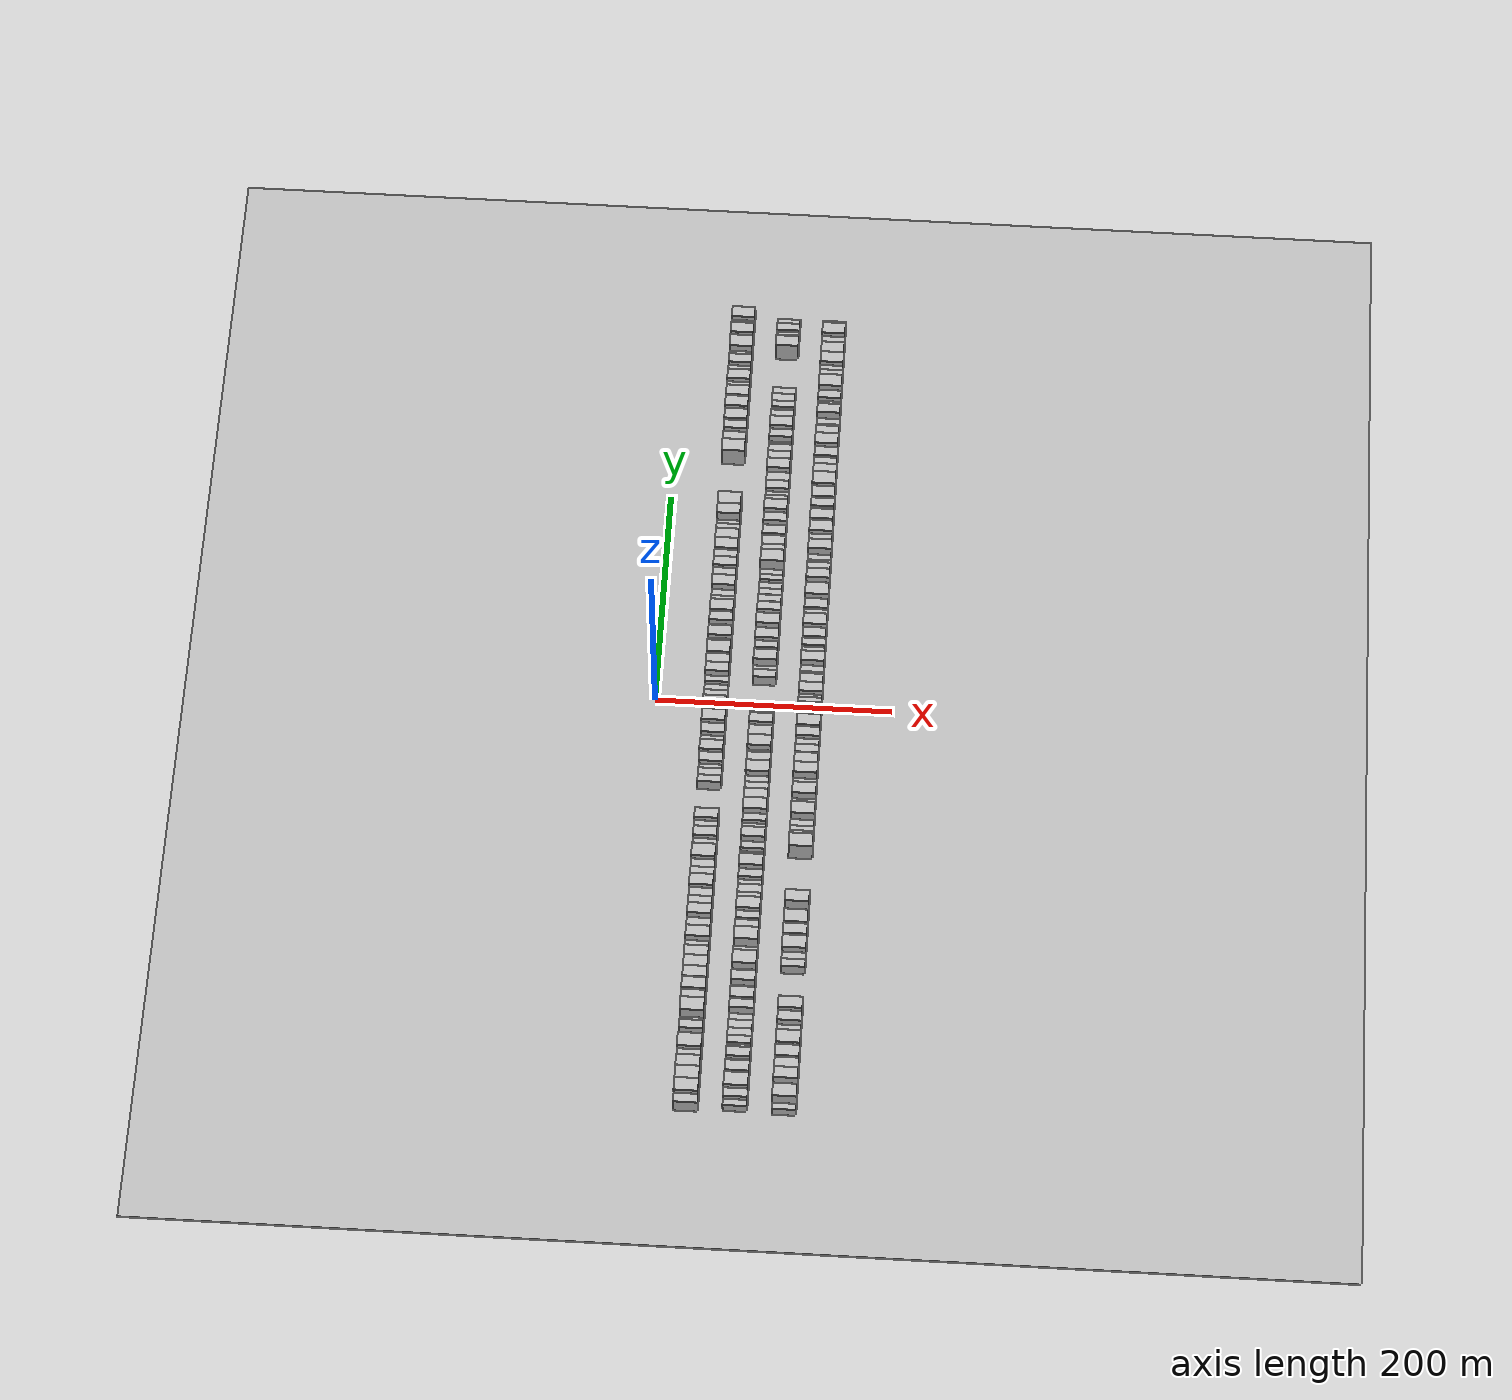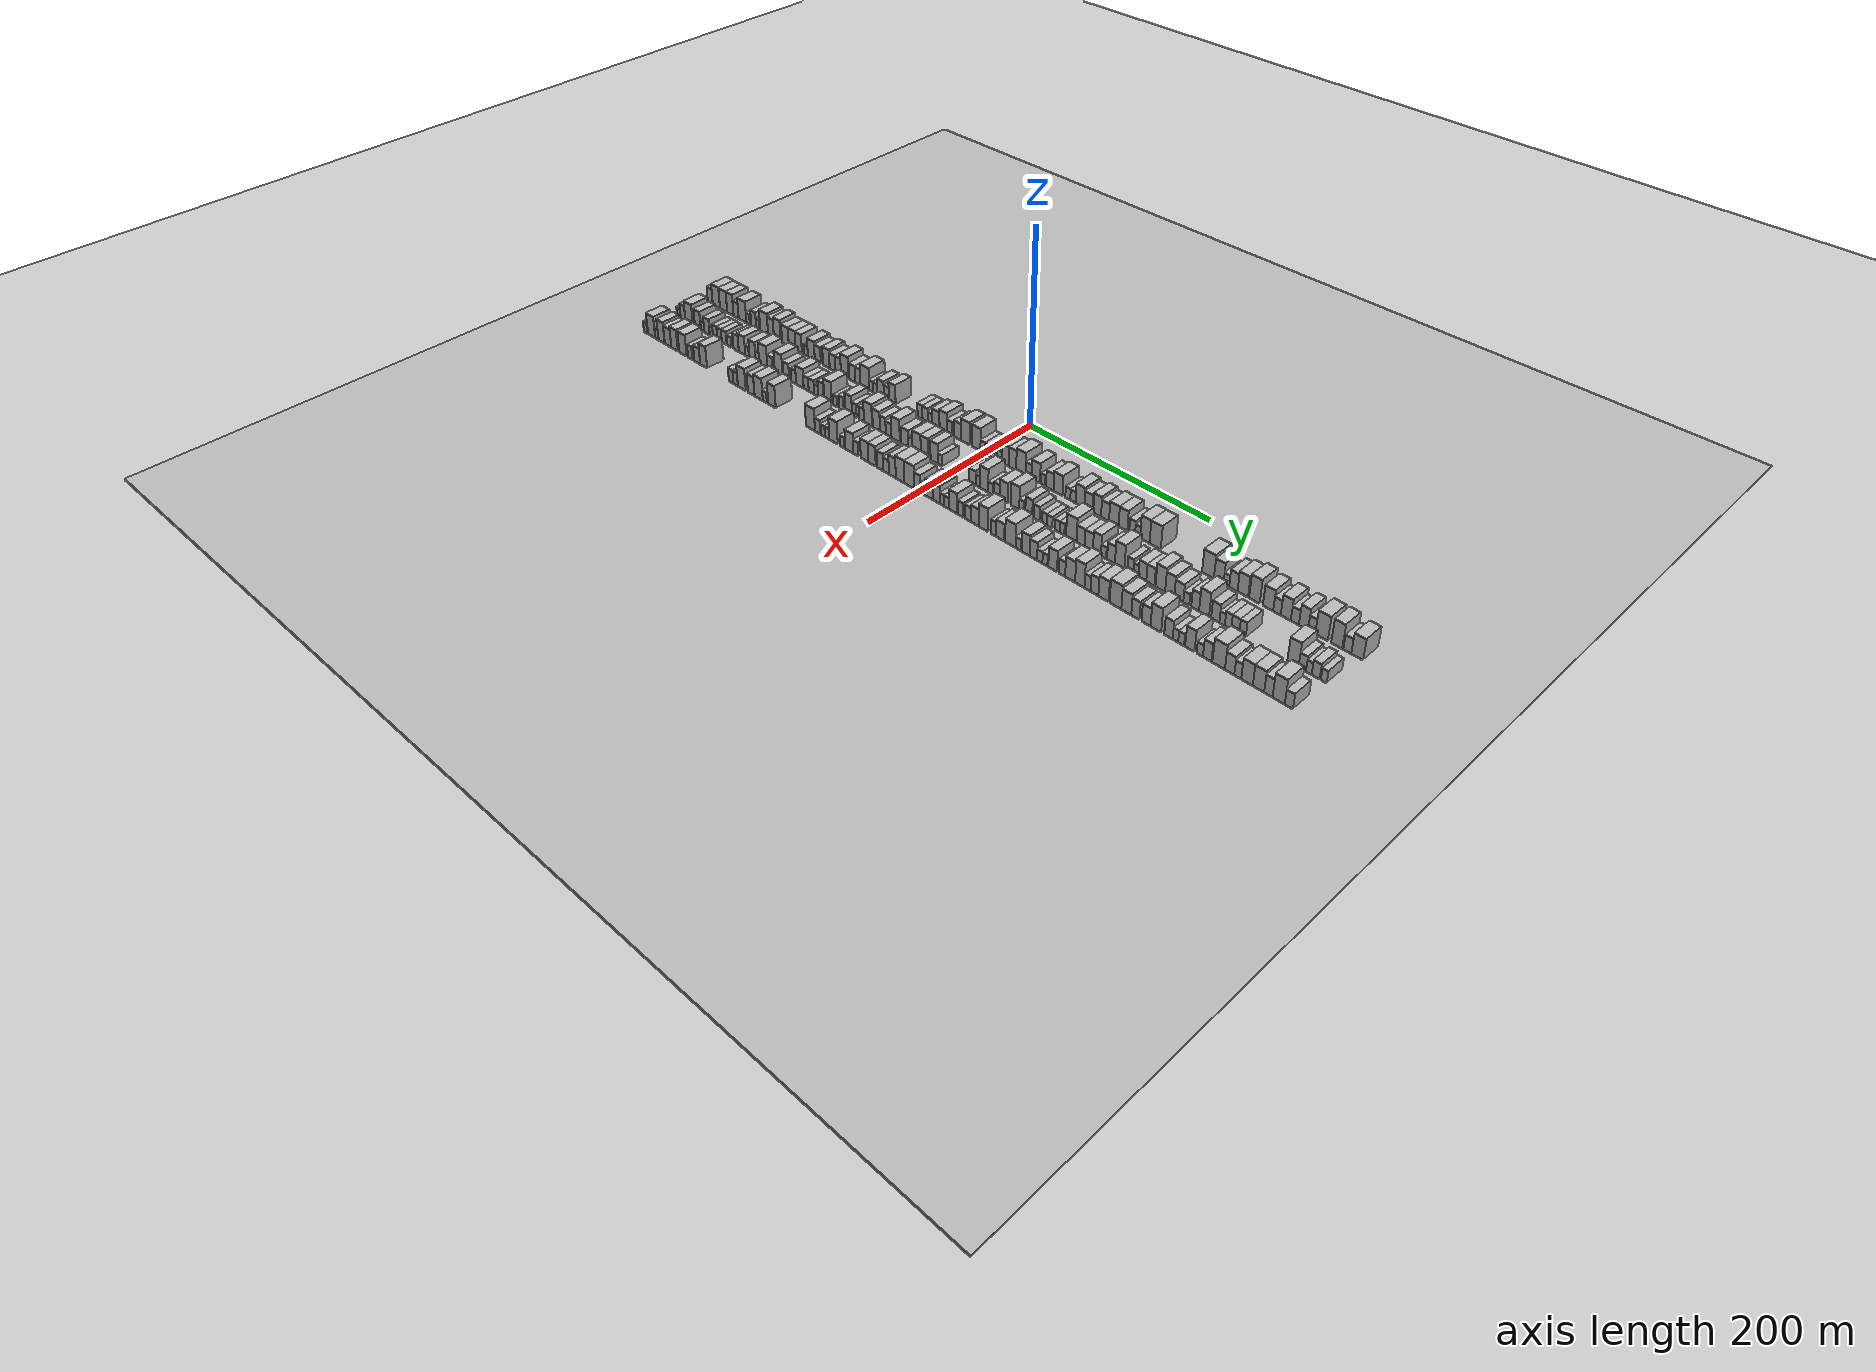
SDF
<?xml version="1.0" encoding="utf-8"?>

<sdf version="1.6">

   <world name="default">

      <gui fullscreen="0">

         <camera name="user_camera">

            <pose>-15 0 4.57585 0 0 0</pose>

            <view_controller>orbit</view_controller>

         </camera>

      </gui>

      <scene>

         <sky>

           <clouds>

             <speed>12</speed>

           </clouds>

         </sky>

         <ambient>0.4 0.4 0.4 1</ambient>

         <background>0.7 0.7 0.7 1</background>

         <shadows>1</shadows>

      </scene>

      <gravity>0 0 -9.8066</gravity>

      <magnetic_field>6e-06 2.3e-05 -4.2e-05</magnetic_field>

      <physics default="0" name="default_physics" type="ode">

         <ode>

            <solver>

               <type>quick</type>

               <iters>10</iters>

               <sor>1.0</sor>

               <use_dynamic_moi_rescaling>0</use_dynamic_moi_rescaling>

            </solver>

            <constraints>

               <cfm>0</cfm>

               <erp>0.2</erp>

               <contact_max_correcting_vel>100</contact_max_correcting_vel>

               <contact_surface_layer>0.001</contact_surface_layer>

            </constraints>

         </ode>

         <max_step_size>0.004</max_step_size>

         <real_time_factor>1</real_time_factor>

         <real_time_update_rate>250</real_time_update_rate>

      </physics>

      <light name="sun" type="directional">

         <cast_shadows>1</cast_shadows>

         <pose>0 0 10 0 0 0</pose>

         <diffuse>0.8 0.8 0.8 1</diffuse>

         <specular>0.2 0.2 0.2 1</specular>

         <attenuation>

            <range>1000</range>

            <constant>0.9</constant>

            <linear>0.01</linear>

            <quadratic>0.001</quadratic>

         </attenuation>

         <direction>-0.5 0.1 -0.9</direction>

      </light>

      <include>

         <name>ground_plane_1</name>

         <uri>model://HANNAS_ground_plane</uri>

         <pose>0 0 0  0 0 0</pose>

      </include>

      <include>

         <name>ground_plane_2</name>

         <uri>model://HANNAS_ground_plane</uri>

         <pose>100 0 0  0 0 0</pose>

      </include>

      <model name="building_1">

         <static>1</static>

         <pose frame="">50.0000 -376.1027 0 0.000000 0.000000 0.000000</pose>

         <link name="link">

            <pose frame="">0 0 9.00 0 0 0</pose>

            <collision name="collision">

               <geometry>

                  <box>

                     <size>20.0000 7.7946 18.0000</size>

                  </box>

               </geometry>

               <max_contacts>10</max_contacts>

               <surface>

                  <contact>

                     <ode/>

                  </contact>

                  <bounce/>

                  <friction>

                     <torsional>

                        <ode/>

                     </torsional>

                     <ode/>

                  </friction>

               </surface>

            </collision>

            <visual name="visual">

               <cast_shadows>0</cast_shadows>

               <geometry>

                  <box>

                     <size>20.0000 7.7946 18.0000</size>

                  </box>

               </geometry>

               <material>

                  <script>

                     <uri>model://HANNAS_wall/materials/scripts</uri>

                     <uri>model://HANNAS_wall/materials/textures</uri>

                     <name>vrc/HANNAS_wall</name>

                  </script>

               </material>

            </visual>

            <self_collide>0</self_collide>

            <enable_wind>0</enable_wind>

            <kinematic>0</kinematic>

         </link>

      </model>

      <model name="building_2">

         <static>1</static>

         <pose frame="">50.0000 -366.5684 0 0.000000 0.000000 0.000000</pose>

         <link name="link">

            <pose frame="">0 0 12.00 0 0 0</pose>

            <collision name="collision">

               <geometry>

                  <box>

                     <size>20.0000 11.2741 24.0000</size>

                  </box>

               </geometry>

               <max_contacts>10</max_contacts>

               <surface>

                  <contact>

                     <ode/>

                  </contact>

                  <bounce/>

                  <friction>

                     <torsional>

                        <ode/>

                     </torsional>

                     <ode/>

                  </friction>

               </surface>

            </collision>

            <visual name="visual">

               <cast_shadows>0</cast_shadows>

               <geometry>

                  <box>

                     <size>20.0000 11.2741 24.0000</size>

                  </box>

               </geometry>

               <material>

                  <script>

                     <uri>model://HANNAS_wall/materials/scripts</uri>

                     <uri>model://HANNAS_wall/materials/textures</uri>

                     <name>vrc/HANNAS_wall</name>

                  </script>

               </material>

            </visual>

            <self_collide>0</self_collide>

            <enable_wind>0</enable_wind>

            <kinematic>0</kinematic>

         </link>

      </model>

      <model name="building_3">

         <static>1</static>

         <pose frame="">50.0000 -355.3672 0 0.000000 0.000000 0.000000</pose>

         <link name="link">

            <pose frame="">0 0 12.00 0 0 0</pose>

            <collision name="collision">

               <geometry>

                  <box>

                     <size>20.0000 11.1284 24.0000</size>

                  </box>

               </geometry>

               <max_contacts>10</max_contacts>

               <surface>

                  <contact>

                     <ode/>

                  </contact>

                  <bounce/>

                  <friction>

                     <torsional>

                        <ode/>

                     </torsional>

                     <ode/>

                  </friction>

               </surface>

            </collision>

            <visual name="visual">

               <cast_shadows>0</cast_shadows>

               <geometry>

                  <box>

                     <size>20.0000 11.1284 24.0000</size>

                  </box>

               </geometry>

               <material>

                  <script>

                     <uri>model://HANNAS_wall/materials/scripts</uri>

                     <uri>model://HANNAS_wall/materials/textures</uri>

                     <name>vrc/HANNAS_wall</name>

                  </script>

               </material>

            </visual>

            <self_collide>0</self_collide>

            <enable_wind>0</enable_wind>

            <kinematic>0</kinematic>

         </link>

      </model>

      <model name="building_4">

         <static>1</static>

         <pose frame="">50.0000 -344.9227 0 0.000000 0.000000 0.000000</pose>

         <link name="link">

            <pose frame="">0 0 12.00 0 0 0</pose>

            <collision name="collision">

               <geometry>

                  <box>

                     <size>20.0000 9.7606 24.0000</size>

                  </box>

               </geometry>

               <max_contacts>10</max_contacts>

               <surface>

                  <contact>

                     <ode/>

                  </contact>

                  <bounce/>

                  <friction>

                     <torsional>

                        <ode/>

                     </torsional>

                     <ode/>

                  </friction>

               </surface>

            </collision>

            <visual name="visual">

               <cast_shadows>0</cast_shadows>

               <geometry>

                  <box>

                     <size>20.0000 9.7606 24.0000</size>

                  </box>

               </geometry>

               <material>

                  <script>

                     <uri>model://HANNAS_wall/materials/scripts</uri>

                     <uri>model://HANNAS_wall/materials/textures</uri>

                     <name>vrc/HANNAS_wall</name>

                  </script>

               </material>

            </visual>

            <self_collide>0</self_collide>

            <enable_wind>0</enable_wind>

            <kinematic>0</kinematic>

         </link>

      </model>

      <model name="building_5">

         <static>1</static>

         <pose frame="">50.0000 -336.1922 0 0.000000 0.000000 0.000000</pose>

         <link name="link">

            <pose frame="">0 0 9.00 0 0 0</pose>

            <collision name="collision">

               <geometry>

                  <box>

                     <size>20.0000 7.7004 18.0000</size>

                  </box>

               </geometry>

               <max_contacts>10</max_contacts>

               <surface>

                  <contact>

                     <ode/>

                  </contact>

                  <bounce/>

                  <friction>

                     <torsional>

                        <ode/>

                     </torsional>

                     <ode/>

                  </friction>

               </surface>

            </collision>

            <visual name="visual">

               <cast_shadows>0</cast_shadows>

               <geometry>

                  <box>

                     <size>20.0000 7.7004 18.0000</size>

                  </box>

               </geometry>

               <material>

                  <script>

                     <uri>model://HANNAS_wall/materials/scripts</uri>

                     <uri>model://HANNAS_wall/materials/textures</uri>

                     <name>vrc/HANNAS_wall</name>

                  </script>

               </material>

            </visual>

            <self_collide>0</self_collide>

            <enable_wind>0</enable_wind>

            <kinematic>0</kinematic>

         </link>

      </model>

      <model name="building_6">

         <static>1</static>

         <pose frame="">50.0000 -326.3883 0 0.000000 0.000000 0.000000</pose>

         <link name="link">

            <pose frame="">0 0 12.00 0 0 0</pose>

            <collision name="collision">

               <geometry>

                  <box>

                     <size>20.0000 11.9073 24.0000</size>

                  </box>

               </geometry>

               <max_contacts>10</max_contacts>

               <surface>

                  <contact>

                     <ode/>

                  </contact>

                  <bounce/>

                  <friction>

                     <torsional>

                        <ode/>

                     </torsional>

                     <ode/>

                  </friction>

               </surface>

            </collision>

            <visual name="visual">

               <cast_shadows>0</cast_shadows>

               <geometry>

                  <box>

                     <size>20.0000 11.9073 24.0000</size>

                  </box>

               </geometry>

               <material>

                  <script>

                     <uri>model://HANNAS_wall/materials/scripts</uri>

                     <uri>model://HANNAS_wall/materials/textures</uri>

                     <name>vrc/HANNAS_wall</name>

                  </script>

               </material>

            </visual>

            <self_collide>0</self_collide>

            <enable_wind>0</enable_wind>

            <kinematic>0</kinematic>

         </link>

      </model>

      <model name="building_7">

         <static>1</static>

         <pose frame="">50.0000 -317.8739 0 0.000000 0.000000 0.000000</pose>

         <link name="link">

            <pose frame="">0 0 6.00 0 0 0</pose>

            <collision name="collision">

               <geometry>

                  <box>

                     <size>20.0000 5.1215 12.0000</size>

                  </box>

               </geometry>

               <max_contacts>10</max_contacts>

               <surface>

                  <contact>

                     <ode/>

                  </contact>

                  <bounce/>

                  <friction>

                     <torsional>

                        <ode/>

                     </torsional>

                     <ode/>

                  </friction>

               </surface>

            </collision>

            <visual name="visual">

               <cast_shadows>0</cast_shadows>

               <geometry>

                  <box>

                     <size>20.0000 5.1215 12.0000</size>

                  </box>

               </geometry>

               <material>

                  <script>

                     <uri>model://HANNAS_wall/materials/scripts</uri>

                     <uri>model://HANNAS_wall/materials/textures</uri>

                     <name>vrc/HANNAS_wall</name>

                  </script>

               </material>

            </visual>

            <self_collide>0</self_collide>

            <enable_wind>0</enable_wind>

            <kinematic>0</kinematic>

         </link>

      </model>

      <model name="building_8">

         <static>1</static>

         <pose frame="">50.0000 -309.5573 0 0.000000 0.000000 0.000000</pose>

         <link name="link">

            <pose frame="">0 0 9.00 0 0 0</pose>

            <collision name="collision">

               <geometry>

                  <box>

                     <size>20.0000 7.5115 18.0000</size>

                  </box>

               </geometry>

               <max_contacts>10</max_contacts>

               <surface>

                  <contact>

                     <ode/>

                  </contact>

                  <bounce/>

                  <friction>

                     <torsional>

                        <ode/>

                     </torsional>

                     <ode/>

                  </friction>

               </surface>

            </collision>

            <visual name="visual">

               <cast_shadows>0</cast_shadows>

               <geometry>

                  <box>

                     <size>20.0000 7.5115 18.0000</size>

                  </box>

               </geometry>

               <material>

                  <script>

                     <uri>model://HANNAS_wall/materials/scripts</uri>

                     <uri>model://HANNAS_wall/materials/textures</uri>

                     <name>vrc/HANNAS_wall</name>

                  </script>

               </material>

            </visual>

            <self_collide>0</self_collide>

            <enable_wind>0</enable_wind>

            <kinematic>0</kinematic>

         </link>

      </model>

      <model name="building_9">

         <static>1</static>

         <pose frame="">50.0000 -303.2889 0 0.000000 0.000000 0.000000</pose>

         <link name="link">

            <pose frame="">0 0 6.00 0 0 0</pose>

            <collision name="collision">

               <geometry>

                  <box>

                     <size>20.0000 5.0254 12.0000</size>

                  </box>

               </geometry>

               <max_contacts>10</max_contacts>

               <surface>

                  <contact>

                     <ode/>

                  </contact>

                  <bounce/>

                  <friction>

                     <torsional>

                        <ode/>

                     </torsional>

                     <ode/>

                  </friction>

               </surface>

            </collision>

            <visual name="visual">

               <cast_shadows>0</cast_shadows>

               <geometry>

                  <box>

                     <size>20.0000 5.0254 12.0000</size>

                  </box>

               </geometry>

               <material>

                  <script>

                     <uri>model://HANNAS_wall/materials/scripts</uri>

                     <uri>model://HANNAS_wall/materials/textures</uri>

                     <name>vrc/HANNAS_wall</name>

                  </script>

               </material>

            </visual>

            <self_collide>0</self_collide>

            <enable_wind>0</enable_wind>

            <kinematic>0</kinematic>

         </link>

      </model>

      <model name="building_10">

         <static>1</static>

         <pose frame="">50.0000 -293.9382 0 0.000000 0.000000 0.000000</pose>

         <link name="link">

            <pose frame="">0 0 12.00 0 0 0</pose>

            <collision name="collision">

               <geometry>

                  <box>

                     <size>20.0000 11.6762 24.0000</size>

                  </box>

               </geometry>

               <max_contacts>10</max_contacts>

               <surface>

                  <contact>

                     <ode/>

                  </contact>

                  <bounce/>

                  <friction>

                     <torsional>

                        <ode/>

                     </torsional>

                     <ode/>

                  </friction>

               </surface>

            </collision>

            <visual name="visual">

               <cast_shadows>0</cast_shadows>

               <geometry>

                  <box>

                     <size>20.0000 11.6762 24.0000</size>

                  </box>

               </geometry>

               <material>

                  <script>

                     <uri>model://HANNAS_wall/materials/scripts</uri>

                     <uri>model://HANNAS_wall/materials/textures</uri>

                     <name>vrc/HANNAS_wall</name>

                  </script>

               </material>

            </visual>

            <self_collide>0</self_collide>

            <enable_wind>0</enable_wind>

            <kinematic>0</kinematic>

         </link>

      </model>

      <model name="building_11">

         <static>1</static>

         <pose frame="">50.0000 -283.8956 0 0.000000 0.000000 0.000000</pose>

         <link name="link">

            <pose frame="">0 0 10.50 0 0 0</pose>

            <collision name="collision">

               <geometry>

                  <box>

                     <size>20.0000 8.4090 21.0000</size>

                  </box>

               </geometry>

               <max_contacts>10</max_contacts>

               <surface>

                  <contact>

                     <ode/>

                  </contact>

                  <bounce/>

                  <friction>

                     <torsional>

                        <ode/>

                     </torsional>

                     <ode/>

                  </friction>

               </surface>

            </collision>

            <visual name="visual">

               <cast_shadows>0</cast_shadows>

               <geometry>

                  <box>

                     <size>20.0000 8.4090 21.0000</size>

                  </box>

               </geometry>

               <material>

                  <script>

                     <uri>model://HANNAS_wall/materials/scripts</uri>

                     <uri>model://HANNAS_wall/materials/textures</uri>

                     <name>vrc/HANNAS_wall</name>

                  </script>

               </material>

            </visual>

            <self_collide>0</self_collide>

            <enable_wind>0</enable_wind>

            <kinematic>0</kinematic>

         </link>

      </model>

      <model name="building_12">

         <static>1</static>

         <pose frame="">50.0000 -274.6847 0 0.000000 0.000000 0.000000</pose>

         <link name="link">

            <pose frame="">0 0 12.00 0 0 0</pose>

            <collision name="collision">

               <geometry>

                  <box>

                     <size>20.0000 10.0127 24.0000</size>

                  </box>

               </geometry>

               <max_contacts>10</max_contacts>

               <surface>

                  <contact>

                     <ode/>

                  </contact>

                  <bounce/>

                  <friction>

                     <torsional>

                        <ode/>

                     </torsional>

                     <ode/>

                  </friction>

               </surface>

            </collision>

            <visual name="visual">

               <cast_shadows>0</cast_shadows>

               <geometry>

                  <box>

                     <size>20.0000 10.0127 24.0000</size>

                  </box>

               </geometry>

               <material>

                  <script>

                     <uri>model://HANNAS_wall/materials/scripts</uri>

                     <uri>model://HANNAS_wall/materials/textures</uri>

                     <name>vrc/HANNAS_wall</name>

                  </script>

               </material>

            </visual>

            <self_collide>0</self_collide>

            <enable_wind>0</enable_wind>

            <kinematic>0</kinematic>

         </link>

      </model>

      <model name="building_13">

         <static>1</static>

         <pose frame="">50.0000 -262.8253 0 0.000000 0.000000 0.000000</pose>

         <link name="link">

            <pose frame="">0 0 10.50 0 0 0</pose>

            <collision name="collision">

               <geometry>

                  <box>

                     <size>20.0000 9.7060 21.0000</size>

                  </box>

               </geometry>

               <max_contacts>10</max_contacts>

               <surface>

                  <contact>

                     <ode/>

                  </contact>

                  <bounce/>

                  <friction>

                     <torsional>

                        <ode/>

                     </torsional>

                     <ode/>

                  </friction>

               </surface>

            </collision>

            <visual name="visual">

               <cast_shadows>0</cast_shadows>

               <geometry>

                  <box>

                     <size>20.0000 9.7060 21.0000</size>

                  </box>

               </geometry>

               <material>

                  <script>

                     <uri>model://HANNAS_wall/materials/scripts</uri>

                     <uri>model://HANNAS_wall/materials/textures</uri>

                     <name>vrc/HANNAS_wall</name>

                  </script>

               </material>

            </visual>

            <self_collide>0</self_collide>

            <enable_wind>0</enable_wind>

            <kinematic>0</kinematic>

         </link>

      </model>

      <model name="building_14">

         <static>1</static>

         <pose frame="">50.0000 -253.0473 0 0.000000 0.000000 0.000000</pose>

         <link name="link">

            <pose frame="">0 0 10.50 0 0 0</pose>

            <collision name="collision">

               <geometry>

                  <box>

                     <size>20.0000 9.8501 21.0000</size>

                  </box>

               </geometry>

               <max_contacts>10</max_contacts>

               <surface>

                  <contact>

                     <ode/>

                  </contact>

                  <bounce/>

                  <friction>

                     <torsional>

                        <ode/>

                     </torsional>

                     <ode/>

                  </friction>

               </surface>

            </collision>

            <visual name="visual">

               <cast_shadows>0</cast_shadows>

               <geometry>

                  <box>

                     <size>20.0000 9.8501 21.0000</size>

                  </box>

               </geometry>

               <material>

                  <script>

                     <uri>model://HANNAS_wall/materials/scripts</uri>

                     <uri>model://HANNAS_wall/materials/textures</uri>

                     <name>vrc/HANNAS_wall</name>

                  </script>

               </material>

            </visual>

            <self_collide>0</self_collide>

            <enable_wind>0</enable_wind>

            <kinematic>0</kinematic>

         </link>

      </model>

      <model name="building_15">

         <static>1</static>

         <pose frame="">50.0000 -243.6932 0 0.000000 0.000000 0.000000</pose>

         <link name="link">

            <pose frame="">0 0 10.50 0 0 0</pose>

            <collision name="collision">

               <geometry>

                  <box>

                     <size>20.0000 8.8581 21.0000</size>

                  </box>

               </geometry>

               <max_contacts>10</max_contacts>

               <surface>

                  <contact>

                     <ode/>

                  </contact>

                  <bounce/>

                  <friction>

                     <torsional>

                        <ode/>

                     </torsional>

                     <ode/>

                  </friction>

               </surface>

            </collision>

            <visual name="visual">

               <cast_shadows>0</cast_shadows>

               <geometry>

                  <box>

                     <size>20.0000 8.8581 21.0000</size>

                  </box>

               </geometry>

               <material>

                  <script>

                     <uri>model://HANNAS_wall/materials/scripts</uri>

                     <uri>model://HANNAS_wall/materials/textures</uri>

                     <name>vrc/HANNAS_wall</name>

                  </script>

               </material>

            </visual>

            <self_collide>0</self_collide>

            <enable_wind>0</enable_wind>

            <kinematic>0</kinematic>

         </link>

      </model>

      <model name="building_16">

         <static>1</static>

         <pose frame="">50.0000 -233.4718 0 0.000000 0.000000 0.000000</pose>

         <link name="link">

            <pose frame="">0 0 6.00 0 0 0</pose>

            <collision name="collision">

               <geometry>

                  <box>

                     <size>20.0000 5.5846 12.0000</size>

                  </box>

               </geometry>

               <max_contacts>10</max_contacts>

               <surface>

                  <contact>

                     <ode/>

                  </contact>

                  <bounce/>

                  <friction>

                     <torsional>

                        <ode/>

                     </torsional>

                     <ode/>

                  </friction>

               </surface>

            </collision>

            <visual name="visual">

               <cast_shadows>0</cast_shadows>

               <geometry>

                  <box>

                     <size>20.0000 5.5846 12.0000</size>

                  </box>

               </geometry>

               <material>

                  <script>

                     <uri>model://HANNAS_wall/materials/scripts</uri>

                     <uri>model://HANNAS_wall/materials/textures</uri>

                     <name>vrc/HANNAS_wall</name>

                  </script>

               </material>

            </visual>

            <self_collide>0</self_collide>

            <enable_wind>0</enable_wind>

            <kinematic>0</kinematic>

         </link>

      </model>

      <model name="building_17">

         <static>1</static>

         <pose frame="">50.0000 -225.7855 0 0.000000 0.000000 0.000000</pose>

         <link name="link">

            <pose frame="">0 0 10.50 0 0 0</pose>

            <collision name="collision">

               <geometry>

                  <box>

                     <size>20.0000 9.7880 21.0000</size>

                  </box>

               </geometry>

               <max_contacts>10</max_contacts>

               <surface>

                  <contact>

                     <ode/>

                  </contact>

                  <bounce/>

                  <friction>

                     <torsional>

                        <ode/>

                     </torsional>

                     <ode/>

                  </friction>

               </surface>

            </collision>

            <visual name="visual">

               <cast_shadows>0</cast_shadows>

               <geometry>

                  <box>

                     <size>20.0000 9.7880 21.0000</size>

                  </box>

               </geometry>

               <material>

                  <script>

                     <uri>model://HANNAS_wall/materials/scripts</uri>

                     <uri>model://HANNAS_wall/materials/textures</uri>

                     <name>vrc/HANNAS_wall</name>

                  </script>

               </material>

            </visual>

            <self_collide>0</self_collide>

            <enable_wind>0</enable_wind>

            <kinematic>0</kinematic>

         </link>

      </model>

      <model name="building_18">

         <static>1</static>

         <pose frame="">50.0000 -216.6525 0 0.000000 0.000000 0.000000</pose>

         <link name="link">

            <pose frame="">0 0 9.00 0 0 0</pose>

            <collision name="collision">

               <geometry>

                  <box>

                     <size>20.0000 8.4779 18.0000</size>

                  </box>

               </geometry>

               <max_contacts>10</max_contacts>

               <surface>

                  <contact>

                     <ode/>

                  </contact>

                  <bounce/>

                  <friction>

                     <torsional>

                        <ode/>

                     </torsional>

                     <ode/>

                  </friction>

               </surface>

            </collision>

            <visual name="visual">

               <cast_shadows>0</cast_shadows>

               <geometry>

                  <box>

                     <size>20.0000 8.4779 18.0000</size>

                  </box>

               </geometry>

               <material>

                  <script>

                     <uri>model://HANNAS_wall/materials/scripts</uri>

                     <uri>model://HANNAS_wall/materials/textures</uri>

                     <name>vrc/HANNAS_wall</name>

                  </script>

               </material>

            </visual>

            <self_collide>0</self_collide>

            <enable_wind>0</enable_wind>

            <kinematic>0</kinematic>

         </link>

      </model>

      <model name="building_19">

         <static>1</static>

         <pose frame="">50.0000 -204.7900 0 0.000000 0.000000 0.000000</pose>

         <link name="link">

            <pose frame="">0 0 10.50 0 0 0</pose>

            <collision name="collision">

               <geometry>

                  <box>

                     <size>20.0000 9.2471 21.0000</size>

                  </box>

               </geometry>

               <max_contacts>10</max_contacts>

               <surface>

                  <contact>

                     <ode/>

                  </contact>

                  <bounce/>

                  <friction>

                     <torsional>

                        <ode/>

                     </torsional>

                     <ode/>

                  </friction>

               </surface>

            </collision>

            <visual name="visual">

               <cast_shadows>0</cast_shadows>

               <geometry>

                  <box>

                     <size>20.0000 9.2471 21.0000</size>

                  </box>

               </geometry>

               <material>

                  <script>

                     <uri>model://HANNAS_wall/materials/scripts</uri>

                     <uri>model://HANNAS_wall/materials/textures</uri>

                     <name>vrc/HANNAS_wall</name>

                  </script>

               </material>

            </visual>

            <self_collide>0</self_collide>

            <enable_wind>0</enable_wind>

            <kinematic>0</kinematic>

         </link>

      </model>

      <model name="building_20">

         <static>1</static>

         <pose frame="">50.0000 -196.1114 0 0.000000 0.000000 0.000000</pose>

         <link name="link">

            <pose frame="">0 0 9.00 0 0 0</pose>

            <collision name="collision">

               <geometry>

                  <box>

                     <size>20.0000 8.1101 18.0000</size>

                  </box>

               </geometry>

               <max_contacts>10</max_contacts>

               <surface>

                  <contact>

                     <ode/>

                  </contact>

                  <bounce/>

                  <friction>

                     <torsional>

                        <ode/>

                     </torsional>

                     <ode/>

                  </friction>

               </surface>

            </collision>

            <visual name="visual">

               <cast_shadows>0</cast_shadows>

               <geometry>

                  <box>

                     <size>20.0000 8.1101 18.0000</size>

                  </box>

               </geometry>

               <material>

                  <script>

                     <uri>model://HANNAS_wall/materials/scripts</uri>

                     <uri>model://HANNAS_wall/materials/textures</uri>

                     <name>vrc/HANNAS_wall</name>

                  </script>

               </material>

            </visual>

            <self_collide>0</self_collide>

            <enable_wind>0</enable_wind>

            <kinematic>0</kinematic>

         </link>

      </model>

      <model name="building_21">

         <static>1</static>

         <pose frame="">50.0000 -188.3198 0 0.000000 0.000000 0.000000</pose>

         <link name="link">

            <pose frame="">0 0 9.00 0 0 0</pose>

            <collision name="collision">

               <geometry>

                  <box>

                     <size>20.0000 7.4732 18.0000</size>

                  </box>

               </geometry>

               <max_contacts>10</max_contacts>

               <surface>

                  <contact>

                     <ode/>

                  </contact>

                  <bounce/>

                  <friction>

                     <torsional>

                        <ode/>

                     </torsional>

                     <ode/>

                  </friction>

               </surface>

            </collision>

            <visual name="visual">

               <cast_shadows>0</cast_shadows>

               <geometry>

                  <box>

                     <size>20.0000 7.4732 18.0000</size>

                  </box>

               </geometry>

               <material>

                  <script>

                     <uri>model://HANNAS_wall/materials/scripts</uri>

                     <uri>model://HANNAS_wall/materials/textures</uri>

                     <name>vrc/HANNAS_wall</name>

                  </script>

               </material>

            </visual>

            <self_collide>0</self_collide>

            <enable_wind>0</enable_wind>

            <kinematic>0</kinematic>

         </link>

      </model>

      <model name="building_22">

         <static>1</static>

         <pose frame="">50.0000 -179.5329 0 0.000000 0.000000 0.000000</pose>

         <link name="link">

            <pose frame="">0 0 12.00 0 0 0</pose>

            <collision name="collision">

               <geometry>

                  <box>

                     <size>20.0000 10.1005 24.0000</size>

                  </box>

               </geometry>

               <max_contacts>10</max_contacts>

               <surface>

                  <contact>

                     <ode/>

                  </contact>

                  <bounce/>

                  <friction>

                     <torsional>

                        <ode/>

                     </torsional>

                     <ode/>

                  </friction>

               </surface>

            </collision>

            <visual name="visual">

               <cast_shadows>0</cast_shadows>

               <geometry>

                  <box>

                     <size>20.0000 10.1005 24.0000</size>

                  </box>

               </geometry>

               <material>

                  <script>

                     <uri>model://HANNAS_wall/materials/scripts</uri>

                     <uri>model://HANNAS_wall/materials/textures</uri>

                     <name>vrc/HANNAS_wall</name>

                  </script>

               </material>

            </visual>

            <self_collide>0</self_collide>

            <enable_wind>0</enable_wind>

            <kinematic>0</kinematic>

         </link>

      </model>

      <model name="building_23">

         <static>1</static>

         <pose frame="">50.0000 -169.3500 0 0.000000 0.000000 0.000000</pose>

         <link name="link">

            <pose frame="">0 0 9.00 0 0 0</pose>

            <collision name="collision">

               <geometry>

                  <box>

                     <size>20.0000 8.2652 18.0000</size>

                  </box>

               </geometry>

               <max_contacts>10</max_contacts>

               <surface>

                  <contact>

                     <ode/>

                  </contact>

                  <bounce/>

                  <friction>

                     <torsional>

                        <ode/>

                     </torsional>

                     <ode/>

                  </friction>

               </surface>

            </collision>

            <visual name="visual">

               <cast_shadows>0</cast_shadows>

               <geometry>

                  <box>

                     <size>20.0000 8.2652 18.0000</size>

                  </box>

               </geometry>

               <material>

                  <script>

                     <uri>model://HANNAS_wall/materials/scripts</uri>

                     <uri>model://HANNAS_wall/materials/textures</uri>

                     <name>vrc/HANNAS_wall</name>

                  </script>

               </material>

            </visual>

            <self_collide>0</self_collide>

            <enable_wind>0</enable_wind>

            <kinematic>0</kinematic>

         </link>

      </model>

      <model name="building_24">

         <static>1</static>

         <pose frame="">50.0000 -161.5943 0 0.000000 0.000000 0.000000</pose>

         <link name="link">

            <pose frame="">0 0 9.00 0 0 0</pose>

            <collision name="collision">

               <geometry>

                  <box>

                     <size>20.0000 7.2461 18.0000</size>

                  </box>

               </geometry>

               <max_contacts>10</max_contacts>

               <surface>

                  <contact>

                     <ode/>

                  </contact>

                  <bounce/>

                  <friction>

                     <torsional>

                        <ode/>

                     </torsional>

                     <ode/>

                  </friction>

               </surface>

            </collision>

            <visual name="visual">

               <cast_shadows>0</cast_shadows>

               <geometry>

                  <box>

                     <size>20.0000 7.2461 18.0000</size>

                  </box>

               </geometry>

               <material>

                  <script>

                     <uri>model://HANNAS_wall/materials/scripts</uri>

                     <uri>model://HANNAS_wall/materials/textures</uri>

                     <name>vrc/HANNAS_wall</name>

                  </script>

               </material>

            </visual>

            <self_collide>0</self_collide>

            <enable_wind>0</enable_wind>

            <kinematic>0</kinematic>

         </link>

      </model>

      <model name="building_25">

         <static>1</static>

         <pose frame="">50.0000 -152.0795 0 0.000000 0.000000 0.000000</pose>

         <link name="link">

            <pose frame="">0 0 12.00 0 0 0</pose>

            <collision name="collision">

               <geometry>

                  <box>

                     <size>20.0000 11.7835 24.0000</size>

                  </box>

               </geometry>

               <max_contacts>10</max_contacts>

               <surface>

                  <contact>

                     <ode/>

                  </contact>

                  <bounce/>

                  <friction>

                     <torsional>

                        <ode/>

                     </torsional>

                     <ode/>

                  </friction>

               </surface>

            </collision>

            <visual name="visual">

               <cast_shadows>0</cast_shadows>

               <geometry>

                  <box>

                     <size>20.0000 11.7835 24.0000</size>

                  </box>

               </geometry>

               <material>

                  <script>

                     <uri>model://HANNAS_wall/materials/scripts</uri>

                     <uri>model://HANNAS_wall/materials/textures</uri>

                     <name>vrc/HANNAS_wall</name>

                  </script>

               </material>

            </visual>

            <self_collide>0</self_collide>

            <enable_wind>0</enable_wind>

            <kinematic>0</kinematic>

         </link>

      </model>

      <model name="building_26">

         <static>1</static>

         <pose frame="">50.0000 -143.7055 0 0.000000 0.000000 0.000000</pose>

         <link name="link">

            <pose frame="">0 0 6.00 0 0 0</pose>

            <collision name="collision">

               <geometry>

                  <box>

                     <size>20.0000 4.9646 12.0000</size>

                  </box>

               </geometry>

               <max_contacts>10</max_contacts>

               <surface>

                  <contact>

                     <ode/>

                  </contact>

                  <bounce/>

                  <friction>

                     <torsional>

                        <ode/>

                     </torsional>

                     <ode/>

                  </friction>

               </surface>

            </collision>

            <visual name="visual">

               <cast_shadows>0</cast_shadows>

               <geometry>

                  <box>

                     <size>20.0000 4.9646 12.0000</size>

                  </box>

               </geometry>

               <material>

                  <script>

                     <uri>model://HANNAS_wall/materials/scripts</uri>

                     <uri>model://HANNAS_wall/materials/textures</uri>

                     <name>vrc/HANNAS_wall</name>

                  </script>

               </material>

            </visual>

            <self_collide>0</self_collide>

            <enable_wind>0</enable_wind>

            <kinematic>0</kinematic>

         </link>

      </model>

      <model name="building_27">

         <static>1</static>

         <pose frame="">50.0000 -138.3703 0 0.000000 0.000000 0.000000</pose>

         <link name="link">

            <pose frame="">0 0 6.00 0 0 0</pose>

            <collision name="collision">

               <geometry>

                  <box>

                     <size>20.0000 5.7059 12.0000</size>

                  </box>

               </geometry>

               <max_contacts>10</max_contacts>

               <surface>

                  <contact>

                     <ode/>

                  </contact>

                  <bounce/>

                  <friction>

                     <torsional>

                        <ode/>

                     </torsional>

                     <ode/>

                  </friction>

               </surface>

            </collision>

            <visual name="visual">

               <cast_shadows>0</cast_shadows>

               <geometry>

                  <box>

                     <size>20.0000 5.7059 12.0000</size>

                  </box>

               </geometry>

               <material>

                  <script>

                     <uri>model://HANNAS_wall/materials/scripts</uri>

                     <uri>model://HANNAS_wall/materials/textures</uri>

                     <name>vrc/HANNAS_wall</name>

                  </script>

               </material>

            </visual>

            <self_collide>0</self_collide>

            <enable_wind>0</enable_wind>

            <kinematic>0</kinematic>

         </link>

      </model>

      <model name="building_28">

         <static>1</static>

         <pose frame="">50.0000 -131.2267 0 0.000000 0.000000 0.000000</pose>

         <link name="link">

            <pose frame="">0 0 9.00 0 0 0</pose>

            <collision name="collision">

               <geometry>

                  <box>

                     <size>20.0000 8.5813 18.0000</size>

                  </box>

               </geometry>

               <max_contacts>10</max_contacts>

               <surface>

                  <contact>

                     <ode/>

                  </contact>

                  <bounce/>

                  <friction>

                     <torsional>

                        <ode/>

                     </torsional>

                     <ode/>

                  </friction>

               </surface>

            </collision>

            <visual name="visual">

               <cast_shadows>0</cast_shadows>

               <geometry>

                  <box>

                     <size>20.0000 8.5813 18.0000</size>

                  </box>

               </geometry>

               <material>

                  <script>

                     <uri>model://HANNAS_wall/materials/scripts</uri>

                     <uri>model://HANNAS_wall/materials/textures</uri>

                     <name>vrc/HANNAS_wall</name>

                  </script>

               </material>

            </visual>

            <self_collide>0</self_collide>

            <enable_wind>0</enable_wind>

            <kinematic>0</kinematic>

         </link>

      </model>

      <model name="building_29">

         <static>1</static>

         <pose frame="">50.0000 -123.6292 0 0.000000 0.000000 0.000000</pose>

         <link name="link">

            <pose frame="">0 0 7.50 0 0 0</pose>

            <collision name="collision">

               <geometry>

                  <box>

                     <size>20.0000 6.6135 15.0000</size>

                  </box>

               </geometry>

               <max_contacts>10</max_contacts>

               <surface>

                  <contact>

                     <ode/>

                  </contact>

                  <bounce/>

                  <friction>

                     <torsional>

                        <ode/>

                     </torsional>

                     <ode/>

                  </friction>

               </surface>

            </collision>

            <visual name="visual">

               <cast_shadows>0</cast_shadows>

               <geometry>

                  <box>

                     <size>20.0000 6.6135 15.0000</size>

                  </box>

               </geometry>

               <material>

                  <script>

                     <uri>model://HANNAS_wall/materials/scripts</uri>

                     <uri>model://HANNAS_wall/materials/textures</uri>

                     <name>vrc/HANNAS_wall</name>

                  </script>

               </material>

            </visual>

            <self_collide>0</self_collide>

            <enable_wind>0</enable_wind>

            <kinematic>0</kinematic>

         </link>

      </model>

      <model name="building_30">

         <static>1</static>

         <pose frame="">50.0000 -115.9181 0 0.000000 0.000000 0.000000</pose>

         <link name="link">

            <pose frame="">0 0 10.50 0 0 0</pose>

            <collision name="collision">

               <geometry>

                  <box>

                     <size>20.0000 8.8087 21.0000</size>

                  </box>

               </geometry>

               <max_contacts>10</max_contacts>

               <surface>

                  <contact>

                     <ode/>

                  </contact>

                  <bounce/>

                  <friction>

                     <torsional>

                        <ode/>

                     </torsional>

                     <ode/>

                  </friction>

               </surface>

            </collision>

            <visual name="visual">

               <cast_shadows>0</cast_shadows>

               <geometry>

                  <box>

                     <size>20.0000 8.8087 21.0000</size>

                  </box>

               </geometry>

               <material>

                  <script>

                     <uri>model://HANNAS_wall/materials/scripts</uri>

                     <uri>model://HANNAS_wall/materials/textures</uri>

                     <name>vrc/HANNAS_wall</name>

                  </script>

               </material>

            </visual>

            <self_collide>0</self_collide>

            <enable_wind>0</enable_wind>

            <kinematic>0</kinematic>

         </link>

      </model>

      <model name="building_31">

         <static>1</static>

         <pose frame="">50.0000 -80.0905 0 0.000000 0.000000 0.000000</pose>

         <link name="link">

            <pose frame="">0 0 7.50 0 0 0</pose>

            <collision name="collision">

               <geometry>

                  <box>

                     <size>20.0000 6.2821 15.0000</size>

                  </box>

               </geometry>

               <max_contacts>10</max_contacts>

               <surface>

                  <contact>

                     <ode/>

                  </contact>

                  <bounce/>

                  <friction>

                     <torsional>

                        <ode/>

                     </torsional>

                     <ode/>

                  </friction>

               </surface>

            </collision>

            <visual name="visual">

               <cast_shadows>0</cast_shadows>

               <geometry>

                  <box>

                     <size>20.0000 6.2821 15.0000</size>

                  </box>

               </geometry>

               <material>

                  <script>

                     <uri>model://HANNAS_wall/materials/scripts</uri>

                     <uri>model://HANNAS_wall/materials/textures</uri>

                     <name>vrc/HANNAS_wall</name>

                  </script>

               </material>

            </visual>

            <self_collide>0</self_collide>

            <enable_wind>0</enable_wind>

            <kinematic>0</kinematic>

         </link>

      </model>

      <model name="building_32">

         <static>1</static>

         <pose frame="">50.0000 -73.6490 0 0.000000 0.000000 0.000000</pose>

         <link name="link">

            <pose frame="">0 0 7.50 0 0 0</pose>

            <collision name="collision">

               <geometry>

                  <box>

                     <size>20.0000 6.6010 15.0000</size>

                  </box>

               </geometry>

               <max_contacts>10</max_contacts>

               <surface>

                  <contact>

                     <ode/>

                  </contact>

                  <bounce/>

                  <friction>

                     <torsional>

                        <ode/>

                     </torsional>

                     <ode/>

                  </friction>

               </surface>

            </collision>

            <visual name="visual">

               <cast_shadows>0</cast_shadows>

               <geometry>

                  <box>

                     <size>20.0000 6.6010 15.0000</size>

                  </box>

               </geometry>

               <material>

                  <script>

                     <uri>model://HANNAS_wall/materials/scripts</uri>

                     <uri>model://HANNAS_wall/materials/textures</uri>

                     <name>vrc/HANNAS_wall</name>

                  </script>

               </material>

            </visual>

            <self_collide>0</self_collide>

            <enable_wind>0</enable_wind>

            <kinematic>0</kinematic>

         </link>

      </model>

      <model name="building_33">

         <static>1</static>

         <pose frame="">50.0000 -67.7067 0 0.000000 0.000000 0.000000</pose>

         <link name="link">

            <pose frame="">0 0 6.00 0 0 0</pose>

            <collision name="collision">

               <geometry>

                  <box>

                     <size>20.0000 5.2834 12.0000</size>

                  </box>

               </geometry>

               <max_contacts>10</max_contacts>

               <surface>

                  <contact>

                     <ode/>

                  </contact>

                  <bounce/>

                  <friction>

                     <torsional>

                        <ode/>

                     </torsional>

                     <ode/>

                  </friction>

               </surface>

            </collision>

            <visual name="visual">

               <cast_shadows>0</cast_shadows>

               <geometry>

                  <box>

                     <size>20.0000 5.2834 12.0000</size>

                  </box>

               </geometry>

               <material>

                  <script>

                     <uri>model://HANNAS_wall/materials/scripts</uri>

                     <uri>model://HANNAS_wall/materials/textures</uri>

                     <name>vrc/HANNAS_wall</name>

                  </script>

               </material>

            </visual>

            <self_collide>0</self_collide>

            <enable_wind>0</enable_wind>

            <kinematic>0</kinematic>

         </link>

      </model>

      <model name="building_34">

         <static>1</static>

         <pose frame="">50.0000 -60.7892 0 0.000000 0.000000 0.000000</pose>

         <link name="link">

            <pose frame="">0 0 9.00 0 0 0</pose>

            <collision name="collision">

               <geometry>

                  <box>

                     <size>20.0000 8.5517 18.0000</size>

                  </box>

               </geometry>

               <max_contacts>10</max_contacts>

               <surface>

                  <contact>

                     <ode/>

                  </contact>

                  <bounce/>

                  <friction>

                     <torsional>

                        <ode/>

                     </torsional>

                     <ode/>

                  </friction>

               </surface>

            </collision>

            <visual name="visual">

               <cast_shadows>0</cast_shadows>

               <geometry>

                  <box>

                     <size>20.0000 8.5517 18.0000</size>

                  </box>

               </geometry>

               <material>

                  <script>

                     <uri>model://HANNAS_wall/materials/scripts</uri>

                     <uri>model://HANNAS_wall/materials/textures</uri>

                     <name>vrc/HANNAS_wall</name>

                  </script>

               </material>

            </visual>

            <self_collide>0</self_collide>

            <enable_wind>0</enable_wind>

            <kinematic>0</kinematic>

         </link>

      </model>

      <model name="building_35">

         <static>1</static>

         <pose frame="">50.0000 -50.9330 0 0.000000 0.000000 0.000000</pose>

         <link name="link">

            <pose frame="">0 0 10.50 0 0 0</pose>

            <collision name="collision">

               <geometry>

                  <box>

                     <size>20.0000 9.1607 21.0000</size>

                  </box>

               </geometry>

               <max_contacts>10</max_contacts>

               <surface>

                  <contact>

                     <ode/>

                  </contact>

                  <bounce/>

                  <friction>

                     <torsional>

                        <ode/>

                     </torsional>

                     <ode/>

                  </friction>

               </surface>

            </collision>

            <visual name="visual">

               <cast_shadows>0</cast_shadows>

               <geometry>

                  <box>

                     <size>20.0000 9.1607 21.0000</size>

                  </box>

               </geometry>

               <material>

                  <script>

                     <uri>model://HANNAS_wall/materials/scripts</uri>

                     <uri>model://HANNAS_wall/materials/textures</uri>

                     <name>vrc/HANNAS_wall</name>

                  </script>

               </material>

            </visual>

            <self_collide>0</self_collide>

            <enable_wind>0</enable_wind>

            <kinematic>0</kinematic>

         </link>

      </model>

      <model name="building_36">

         <static>1</static>

         <pose frame="">50.0000 -42.9016 0 0.000000 0.000000 0.000000</pose>

         <link name="link">

            <pose frame="">0 0 7.50 0 0 0</pose>

            <collision name="collision">

               <geometry>

                  <box>

                     <size>20.0000 6.9022 15.0000</size>

                  </box>

               </geometry>

               <max_contacts>10</max_contacts>

               <surface>

                  <contact>

                     <ode/>

                  </contact>

                  <bounce/>

                  <friction>

                     <torsional>

                        <ode/>

                     </torsional>

                     <ode/>

                  </friction>

               </surface>

            </collision>

            <visual name="visual">

               <cast_shadows>0</cast_shadows>

               <geometry>

                  <box>

                     <size>20.0000 6.9022 15.0000</size>

                  </box>

               </geometry>

               <material>

                  <script>

                     <uri>model://HANNAS_wall/materials/scripts</uri>

                     <uri>model://HANNAS_wall/materials/textures</uri>

                     <name>vrc/HANNAS_wall</name>

                  </script>

               </material>

            </visual>

            <self_collide>0</self_collide>

            <enable_wind>0</enable_wind>

            <kinematic>0</kinematic>

         </link>

      </model>

      <model name="building_37">

         <static>1</static>

         <pose frame="">50.0000 -33.1178 0 0.000000 0.000000 0.000000</pose>

         <link name="link">

            <pose frame="">0 0 9.00 0 0 0</pose>

            <collision name="collision">

               <geometry>

                  <box>

                     <size>20.0000 8.6654 18.0000</size>

                  </box>

               </geometry>

               <max_contacts>10</max_contacts>

               <surface>

                  <contact>

                     <ode/>

                  </contact>

                  <bounce/>

                  <friction>

                     <torsional>

                        <ode/>

                     </torsional>

                     <ode/>

                  </friction>

               </surface>

            </collision>

            <visual name="visual">

               <cast_shadows>0</cast_shadows>

               <geometry>

                  <box>

                     <size>20.0000 8.6654 18.0000</size>

                  </box>

               </geometry>

               <material>

                  <script>

                     <uri>model://HANNAS_wall/materials/scripts</uri>

                     <uri>model://HANNAS_wall/materials/textures</uri>

                     <name>vrc/HANNAS_wall</name>

                  </script>

               </material>

            </visual>

            <self_collide>0</self_collide>

            <enable_wind>0</enable_wind>

            <kinematic>0</kinematic>

         </link>

      </model>

      <model name="building_38">

         <static>1</static>

         <pose frame="">50.0000 -23.6172 0 0.000000 0.000000 0.000000</pose>

         <link name="link">

            <pose frame="">0 0 12.00 0 0 0</pose>

            <collision name="collision">

               <geometry>

                  <box>

                     <size>20.0000 10.3358 24.0000</size>

                  </box>

               </geometry>

               <max_contacts>10</max_contacts>

               <surface>

                  <contact>

                     <ode/>

                  </contact>

                  <bounce/>

                  <friction>

                     <torsional>

                        <ode/>

                     </torsional>

                     <ode/>

                  </friction>

               </surface>

            </collision>

            <visual name="visual">

               <cast_shadows>0</cast_shadows>

               <geometry>

                  <box>

                     <size>20.0000 10.3358 24.0000</size>

                  </box>

               </geometry>

               <material>

                  <script>

                     <uri>model://HANNAS_wall/materials/scripts</uri>

                     <uri>model://HANNAS_wall/materials/textures</uri>

                     <name>vrc/HANNAS_wall</name>

                  </script>

               </material>

            </visual>

            <self_collide>0</self_collide>

            <enable_wind>0</enable_wind>

            <kinematic>0</kinematic>

         </link>

      </model>

      <model name="building_39">

         <static>1</static>

         <pose frame="">50.0000 -10.4060 0 0.000000 0.000000 0.000000</pose>

         <link name="link">

            <pose frame="">0 0 12.00 0 0 0</pose>

            <collision name="collision">

               <geometry>

                  <box>

                     <size>20.0000 10.0866 24.0000</size>

                  </box>

               </geometry>

               <max_contacts>10</max_contacts>

               <surface>

                  <contact>

                     <ode/>

                  </contact>

                  <bounce/>

                  <friction>

                     <torsional>

                        <ode/>

                     </torsional>

                     <ode/>

                  </friction>

               </surface>

            </collision>

            <visual name="visual">

               <cast_shadows>0</cast_shadows>

               <geometry>

                  <box>

                     <size>20.0000 10.0866 24.0000</size>

                  </box>

               </geometry>

               <material>

                  <script>

                     <uri>model://HANNAS_wall/materials/scripts</uri>

                     <uri>model://HANNAS_wall/materials/textures</uri>

                     <name>vrc/HANNAS_wall</name>

                  </script>

               </material>

            </visual>

            <self_collide>0</self_collide>

            <enable_wind>0</enable_wind>

            <kinematic>0</kinematic>

         </link>

      </model>

      <model name="building_40">

         <static>1</static>

         <pose frame="">50.0000 -2.4798 0 0.000000 0.000000 0.000000</pose>

         <link name="link">

            <pose frame="">0 0 6.00 0 0 0</pose>

            <collision name="collision">

               <geometry>

                  <box>

                     <size>20.0000 5.7658 12.0000</size>

                  </box>

               </geometry>

               <max_contacts>10</max_contacts>

               <surface>

                  <contact>

                     <ode/>

                  </contact>

                  <bounce/>

                  <friction>

                     <torsional>

                        <ode/>

                     </torsional>

                     <ode/>

                  </friction>

               </surface>

            </collision>

            <visual name="visual">

               <cast_shadows>0</cast_shadows>

               <geometry>

                  <box>

                     <size>20.0000 5.7658 12.0000</size>

                  </box>

               </geometry>

               <material>

                  <script>

                     <uri>model://HANNAS_wall/materials/scripts</uri>

                     <uri>model://HANNAS_wall/materials/textures</uri>

                     <name>vrc/HANNAS_wall</name>

                  </script>

               </material>

            </visual>

            <self_collide>0</self_collide>

            <enable_wind>0</enable_wind>

            <kinematic>0</kinematic>

         </link>

      </model>

      <model name="building_41">

         <static>1</static>

         <pose frame="">50.0000 3.4002 0 0.000000 0.000000 0.000000</pose>

         <link name="link">

            <pose frame="">0 0 6.00 0 0 0</pose>

            <collision name="collision">

               <geometry>

                  <box>

                     <size>20.0000 5.9941 12.0000</size>

                  </box>

               </geometry>

               <max_contacts>10</max_contacts>

               <surface>

                  <contact>

                     <ode/>

                  </contact>

                  <bounce/>

                  <friction>

                     <torsional>

                        <ode/>

                     </torsional>

                     <ode/>

                  </friction>

               </surface>

            </collision>

            <visual name="visual">

               <cast_shadows>0</cast_shadows>

               <geometry>

                  <box>

                     <size>20.0000 5.9941 12.0000</size>

                  </box>

               </geometry>

               <material>

                  <script>

                     <uri>model://HANNAS_wall/materials/scripts</uri>

                     <uri>model://HANNAS_wall/materials/textures</uri>

                     <name>vrc/HANNAS_wall</name>

                  </script>

               </material>

            </visual>

            <self_collide>0</self_collide>

            <enable_wind>0</enable_wind>

            <kinematic>0</kinematic>

         </link>

      </model>

      <model name="building_42">

         <static>1</static>

         <pose frame="">50.0000 9.0390 0 0.000000 0.000000 0.000000</pose>

         <link name="link">

            <pose frame="">0 0 6.00 0 0 0</pose>

            <collision name="collision">

               <geometry>

                  <box>

                     <size>20.0000 5.2836 12.0000</size>

                  </box>

               </geometry>

               <max_contacts>10</max_contacts>

               <surface>

                  <contact>

                     <ode/>

                  </contact>

                  <bounce/>

                  <friction>

                     <torsional>

                        <ode/>

                     </torsional>

                     <ode/>

                  </friction>

               </surface>

            </collision>

            <visual name="visual">

               <cast_shadows>0</cast_shadows>

               <geometry>

                  <box>

                     <size>20.0000 5.2836 12.0000</size>

                  </box>

               </geometry>

               <material>

                  <script>

                     <uri>model://HANNAS_wall/materials/scripts</uri>

                     <uri>model://HANNAS_wall/materials/textures</uri>

                     <name>vrc/HANNAS_wall</name>

                  </script>

               </material>

            </visual>

            <self_collide>0</self_collide>

            <enable_wind>0</enable_wind>

            <kinematic>0</kinematic>

         </link>

      </model>

      <model name="building_43">

         <static>1</static>

         <pose frame="">50.0000 17.3146 0 0.000000 0.000000 0.000000</pose>

         <link name="link">

            <pose frame="">0 0 6.00 0 0 0</pose>

            <collision name="collision">

               <geometry>

                  <box>

                     <size>20.0000 5.2675 12.0000</size>

                  </box>

               </geometry>

               <max_contacts>10</max_contacts>

               <surface>

                  <contact>

                     <ode/>

                  </contact>

                  <bounce/>

                  <friction>

                     <torsional>

                        <ode/>

                     </torsional>

                     <ode/>

                  </friction>

               </surface>

            </collision>

            <visual name="visual">

               <cast_shadows>0</cast_shadows>

               <geometry>

                  <box>

                     <size>20.0000 5.2675 12.0000</size>

                  </box>

               </geometry>

               <material>

                  <script>

                     <uri>model://HANNAS_wall/materials/scripts</uri>

                     <uri>model://HANNAS_wall/materials/textures</uri>

                     <name>vrc/HANNAS_wall</name>

                  </script>

               </material>

            </visual>

            <self_collide>0</self_collide>

            <enable_wind>0</enable_wind>

            <kinematic>0</kinematic>

         </link>

      </model>

      <model name="building_44">

         <static>1</static>

         <pose frame="">50.0000 24.1969 0 0.000000 0.000000 0.000000</pose>

         <link name="link">

            <pose frame="">0 0 10.50 0 0 0</pose>

            <collision name="collision">

               <geometry>

                  <box>

                     <size>20.0000 8.4972 21.0000</size>

                  </box>

               </geometry>

               <max_contacts>10</max_contacts>

               <surface>

                  <contact>

                     <ode/>

                  </contact>

                  <bounce/>

                  <friction>

                     <torsional>

                        <ode/>

                     </torsional>

                     <ode/>

                  </friction>

               </surface>

            </collision>

            <visual name="visual">

               <cast_shadows>0</cast_shadows>

               <geometry>

                  <box>

                     <size>20.0000 8.4972 21.0000</size>

                  </box>

               </geometry>

               <material>

                  <script>

                     <uri>model://HANNAS_wall/materials/scripts</uri>

                     <uri>model://HANNAS_wall/materials/textures</uri>

                     <name>vrc/HANNAS_wall</name>

                  </script>

               </material>

            </visual>

            <self_collide>0</self_collide>

            <enable_wind>0</enable_wind>

            <kinematic>0</kinematic>

         </link>

      </model>

      <model name="building_45">

         <static>1</static>

         <pose frame="">50.0000 32.7116 0 0.000000 0.000000 0.000000</pose>

         <link name="link">

            <pose frame="">0 0 10.50 0 0 0</pose>

            <collision name="collision">

               <geometry>

                  <box>

                     <size>20.0000 8.5323 21.0000</size>

                  </box>

               </geometry>

               <max_contacts>10</max_contacts>

               <surface>

                  <contact>

                     <ode/>

                  </contact>

                  <bounce/>

                  <friction>

                     <torsional>

                        <ode/>

                     </torsional>

                     <ode/>

                  </friction>

               </surface>

            </collision>

            <visual name="visual">

               <cast_shadows>0</cast_shadows>

               <geometry>

                  <box>

                     <size>20.0000 8.5323 21.0000</size>

                  </box>

               </geometry>

               <material>

                  <script>

                     <uri>model://HANNAS_wall/materials/scripts</uri>

                     <uri>model://HANNAS_wall/materials/textures</uri>

                     <name>vrc/HANNAS_wall</name>

                  </script>

               </material>

            </visual>

            <self_collide>0</self_collide>

            <enable_wind>0</enable_wind>

            <kinematic>0</kinematic>

         </link>

      </model>

      <model name="building_46">

         <static>1</static>

         <pose frame="">50.0000 42.5591 0 0.000000 0.000000 0.000000</pose>

         <link name="link">

            <pose frame="">0 0 12.00 0 0 0</pose>

            <collision name="collision">

               <geometry>

                  <box>

                     <size>20.0000 11.1626 24.0000</size>

                  </box>

               </geometry>

               <max_contacts>10</max_contacts>

               <surface>

                  <contact>

                     <ode/>

                  </contact>

                  <bounce/>

                  <friction>

                     <torsional>

                        <ode/>

                     </torsional>

                     <ode/>

                  </friction>

               </surface>

            </collision>

            <visual name="visual">

               <cast_shadows>0</cast_shadows>

               <geometry>

                  <box>

                     <size>20.0000 11.1626 24.0000</size>

                  </box>

               </geometry>

               <material>

                  <script>

                     <uri>model://HANNAS_wall/materials/scripts</uri>

                     <uri>model://HANNAS_wall/materials/textures</uri>

                     <name>vrc/HANNAS_wall</name>

                  </script>

               </material>

            </visual>

            <self_collide>0</self_collide>

            <enable_wind>0</enable_wind>

            <kinematic>0</kinematic>

         </link>

      </model>

      <model name="building_47">

         <static>1</static>

         <pose frame="">50.0000 51.5305 0 0.000000 0.000000 0.000000</pose>

         <link name="link">

            <pose frame="">0 0 7.50 0 0 0</pose>

            <collision name="collision">

               <geometry>

                  <box>

                     <size>20.0000 6.7802 15.0000</size>

                  </box>

               </geometry>

               <max_contacts>10</max_contacts>

               <surface>

                  <contact>

                     <ode/>

                  </contact>

                  <bounce/>

                  <friction>

                     <torsional>

                        <ode/>

                     </torsional>

                     <ode/>

                  </friction>

               </surface>

            </collision>

            <visual name="visual">

               <cast_shadows>0</cast_shadows>

               <geometry>

                  <box>

                     <size>20.0000 6.7802 15.0000</size>

                  </box>

               </geometry>

               <material>

                  <script>

                     <uri>model://HANNAS_wall/materials/scripts</uri>

                     <uri>model://HANNAS_wall/materials/textures</uri>

                     <name>vrc/HANNAS_wall</name>

                  </script>

               </material>

            </visual>

            <self_collide>0</self_collide>

            <enable_wind>0</enable_wind>

            <kinematic>0</kinematic>

         </link>

      </model>

      <model name="building_48">

         <static>1</static>

         <pose frame="">50.0000 59.6925 0 0.000000 0.000000 0.000000</pose>

         <link name="link">

            <pose frame="">0 0 10.50 0 0 0</pose>

            <collision name="collision">

               <geometry>

                  <box>

                     <size>20.0000 9.5437 21.0000</size>

                  </box>

               </geometry>

               <max_contacts>10</max_contacts>

               <surface>

                  <contact>

                     <ode/>

                  </contact>

                  <bounce/>

                  <friction>

                     <torsional>

                        <ode/>

                     </torsional>

                     <ode/>

                  </friction>

               </surface>

            </collision>

            <visual name="visual">

               <cast_shadows>0</cast_shadows>

               <geometry>

                  <box>

                     <size>20.0000 9.5437 21.0000</size>

                  </box>

               </geometry>

               <material>

                  <script>

                     <uri>model://HANNAS_wall/materials/scripts</uri>

                     <uri>model://HANNAS_wall/materials/textures</uri>

                     <name>vrc/HANNAS_wall</name>

                  </script>

               </material>

            </visual>

            <self_collide>0</self_collide>

            <enable_wind>0</enable_wind>

            <kinematic>0</kinematic>

         </link>

      </model>

      <model name="building_49">

         <static>1</static>

         <pose frame="">50.0000 67.8998 0 0.000000 0.000000 0.000000</pose>

         <link name="link">

            <pose frame="">0 0 6.00 0 0 0</pose>

            <collision name="collision">

               <geometry>

                  <box>

                     <size>20.0000 4.8709 12.0000</size>

                  </box>

               </geometry>

               <max_contacts>10</max_contacts>

               <surface>

                  <contact>

                     <ode/>

                  </contact>

                  <bounce/>

                  <friction>

                     <torsional>

                        <ode/>

                     </torsional>

                     <ode/>

                  </friction>

               </surface>

            </collision>

            <visual name="visual">

               <cast_shadows>0</cast_shadows>

               <geometry>

                  <box>

                     <size>20.0000 4.8709 12.0000</size>

                  </box>

               </geometry>

               <material>

                  <script>

                     <uri>model://HANNAS_wall/materials/scripts</uri>

                     <uri>model://HANNAS_wall/materials/textures</uri>

                     <name>vrc/HANNAS_wall</name>

                  </script>

               </material>

            </visual>

            <self_collide>0</self_collide>

            <enable_wind>0</enable_wind>

            <kinematic>0</kinematic>

         </link>

      </model>

      <model name="building_50">

         <static>1</static>

         <pose frame="">50.0000 75.5882 0 0.000000 0.000000 0.000000</pose>

         <link name="link">

            <pose frame="">0 0 9.00 0 0 0</pose>

            <collision name="collision">

               <geometry>

                  <box>

                     <size>20.0000 8.5059 18.0000</size>

                  </box>

               </geometry>

               <max_contacts>10</max_contacts>

               <surface>

                  <contact>

                     <ode/>

                  </contact>

                  <bounce/>

                  <friction>

                     <torsional>

                        <ode/>

                     </torsional>

                     <ode/>

                  </friction>

               </surface>

            </collision>

            <visual name="visual">

               <cast_shadows>0</cast_shadows>

               <geometry>

                  <box>

                     <size>20.0000 8.5059 18.0000</size>

                  </box>

               </geometry>

               <material>

                  <script>

                     <uri>model://HANNAS_wall/materials/scripts</uri>

                     <uri>model://HANNAS_wall/materials/textures</uri>

                     <name>vrc/HANNAS_wall</name>

                  </script>

               </material>

            </visual>

            <self_collide>0</self_collide>

            <enable_wind>0</enable_wind>

            <kinematic>0</kinematic>

         </link>

      </model>

      <model name="building_51">

         <static>1</static>

         <pose frame="">50.0000 84.9459 0 0.000000 0.000000 0.000000</pose>

         <link name="link">

            <pose frame="">0 0 10.50 0 0 0</pose>

            <collision name="collision">

               <geometry>

                  <box>

                     <size>20.0000 10.2094 21.0000</size>

                  </box>

               </geometry>

               <max_contacts>10</max_contacts>

               <surface>

                  <contact>

                     <ode/>

                  </contact>

                  <bounce/>

                  <friction>

                     <torsional>

                        <ode/>

                     </torsional>

                     <ode/>

                  </friction>

               </surface>

            </collision>

            <visual name="visual">

               <cast_shadows>0</cast_shadows>

               <geometry>

                  <box>

                     <size>20.0000 10.2094 21.0000</size>

                  </box>

               </geometry>

               <material>

                  <script>

                     <uri>model://HANNAS_wall/materials/scripts</uri>

                     <uri>model://HANNAS_wall/materials/textures</uri>

                     <name>vrc/HANNAS_wall</name>

                  </script>

               </material>

            </visual>

            <self_collide>0</self_collide>

            <enable_wind>0</enable_wind>

            <kinematic>0</kinematic>

         </link>

      </model>

      <model name="building_52">

         <static>1</static>

         <pose frame="">50.0000 95.7833 0 0.000000 0.000000 0.000000</pose>

         <link name="link">

            <pose frame="">0 0 6.00 0 0 0</pose>

            <collision name="collision">

               <geometry>

                  <box>

                     <size>20.0000 5.4654 12.0000</size>

                  </box>

               </geometry>

               <max_contacts>10</max_contacts>

               <surface>

                  <contact>

                     <ode/>

                  </contact>

                  <bounce/>

                  <friction>

                     <torsional>

                        <ode/>

                     </torsional>

                     <ode/>

                  </friction>

               </surface>

            </collision>

            <visual name="visual">

               <cast_shadows>0</cast_shadows>

               <geometry>

                  <box>

                     <size>20.0000 5.4654 12.0000</size>

                  </box>

               </geometry>

               <material>

                  <script>

                     <uri>model://HANNAS_wall/materials/scripts</uri>

                     <uri>model://HANNAS_wall/materials/textures</uri>

                     <name>vrc/HANNAS_wall</name>

                  </script>

               </material>

            </visual>

            <self_collide>0</self_collide>

            <enable_wind>0</enable_wind>

            <kinematic>0</kinematic>

         </link>

      </model>

      <model name="building_53">

         <static>1</static>

         <pose frame="">50.0000 101.4940 0 0.000000 0.000000 0.000000</pose>

         <link name="link">

            <pose frame="">0 0 6.00 0 0 0</pose>

            <collision name="collision">

               <geometry>

                  <box>

                     <size>20.0000 5.9561 12.0000</size>

                  </box>

               </geometry>

               <max_contacts>10</max_contacts>

               <surface>

                  <contact>

                     <ode/>

                  </contact>

                  <bounce/>

                  <friction>

                     <torsional>

                        <ode/>

                     </torsional>

                     <ode/>

                  </friction>

               </surface>

            </collision>

            <visual name="visual">

               <cast_shadows>0</cast_shadows>

               <geometry>

                  <box>

                     <size>20.0000 5.9561 12.0000</size>

                  </box>

               </geometry>

               <material>

                  <script>

                     <uri>model://HANNAS_wall/materials/scripts</uri>

                     <uri>model://HANNAS_wall/materials/textures</uri>

                     <name>vrc/HANNAS_wall</name>

                  </script>

               </material>

            </visual>

            <self_collide>0</self_collide>

            <enable_wind>0</enable_wind>

            <kinematic>0</kinematic>

         </link>

      </model>

      <model name="building_54">

         <static>1</static>

         <pose frame="">50.0000 109.3592 0 0.000000 0.000000 0.000000</pose>

         <link name="link">

            <pose frame="">0 0 10.50 0 0 0</pose>

            <collision name="collision">

               <geometry>

                  <box>

                     <size>20.0000 9.7743 21.0000</size>

                  </box>

               </geometry>

               <max_contacts>10</max_contacts>

               <surface>

                  <contact>

                     <ode/>

                  </contact>

                  <bounce/>

                  <friction>

                     <torsional>

                        <ode/>

                     </torsional>

                     <ode/>

                  </friction>

               </surface>

            </collision>

            <visual name="visual">

               <cast_shadows>0</cast_shadows>

               <geometry>

                  <box>

                     <size>20.0000 9.7743 21.0000</size>

                  </box>

               </geometry>

               <material>

                  <script>

                     <uri>model://HANNAS_wall/materials/scripts</uri>

                     <uri>model://HANNAS_wall/materials/textures</uri>

                     <name>vrc/HANNAS_wall</name>

                  </script>

               </material>

            </visual>

            <self_collide>0</self_collide>

            <enable_wind>0</enable_wind>

            <kinematic>0</kinematic>

         </link>

      </model>

      <model name="building_55">

         <static>1</static>

         <pose frame="">50.0000 118.4897 0 0.000000 0.000000 0.000000</pose>

         <link name="link">

            <pose frame="">0 0 9.00 0 0 0</pose>

            <collision name="collision">

               <geometry>

                  <box>

                     <size>20.0000 8.4868 18.0000</size>

                  </box>

               </geometry>

               <max_contacts>10</max_contacts>

               <surface>

                  <contact>

                     <ode/>

                  </contact>

                  <bounce/>

                  <friction>

                     <torsional>

                        <ode/>

                     </torsional>

                     <ode/>

                  </friction>

               </surface>

            </collision>

            <visual name="visual">

               <cast_shadows>0</cast_shadows>

               <geometry>

                  <box>

                     <size>20.0000 8.4868 18.0000</size>

                  </box>

               </geometry>

               <material>

                  <script>

                     <uri>model://HANNAS_wall/materials/scripts</uri>

                     <uri>model://HANNAS_wall/materials/textures</uri>

                     <name>vrc/HANNAS_wall</name>

                  </script>

               </material>

            </visual>

            <self_collide>0</self_collide>

            <enable_wind>0</enable_wind>

            <kinematic>0</kinematic>

         </link>

      </model>

      <model name="building_56">

         <static>1</static>

         <pose frame="">50.0000 127.9773 0 0.000000 0.000000 0.000000</pose>

         <link name="link">

            <pose frame="">0 0 10.50 0 0 0</pose>

            <collision name="collision">

               <geometry>

                  <box>

                     <size>20.0000 8.4884 21.0000</size>

                  </box>

               </geometry>

               <max_contacts>10</max_contacts>

               <surface>

                  <contact>

                     <ode/>

                  </contact>

                  <bounce/>

                  <friction>

                     <torsional>

                        <ode/>

                     </torsional>

                     <ode/>

                  </friction>

               </surface>

            </collision>

            <visual name="visual">

               <cast_shadows>0</cast_shadows>

               <geometry>

                  <box>

                     <size>20.0000 8.4884 21.0000</size>

                  </box>

               </geometry>

               <material>

                  <script>

                     <uri>model://HANNAS_wall/materials/scripts</uri>

                     <uri>model://HANNAS_wall/materials/textures</uri>

                     <name>vrc/HANNAS_wall</name>

                  </script>

               </material>

            </visual>

            <self_collide>0</self_collide>

            <enable_wind>0</enable_wind>

            <kinematic>0</kinematic>

         </link>

      </model>

      <model name="building_57">

         <static>1</static>

         <pose frame="">50.0000 136.5265 0 0.000000 0.000000 0.000000</pose>

         <link name="link">

            <pose frame="">0 0 9.00 0 0 0</pose>

            <collision name="collision">

               <geometry>

                  <box>

                     <size>20.0000 8.6100 18.0000</size>

                  </box>

               </geometry>

               <max_contacts>10</max_contacts>

               <surface>

                  <contact>

                     <ode/>

                  </contact>

                  <bounce/>

                  <friction>

                     <torsional>

                        <ode/>

                     </torsional>

                     <ode/>

                  </friction>

               </surface>

            </collision>

            <visual name="visual">

               <cast_shadows>0</cast_shadows>

               <geometry>

                  <box>

                     <size>20.0000 8.6100 18.0000</size>

                  </box>

               </geometry>

               <material>

                  <script>

                     <uri>model://HANNAS_wall/materials/scripts</uri>

                     <uri>model://HANNAS_wall/materials/textures</uri>

                     <name>vrc/HANNAS_wall</name>

                  </script>

               </material>

            </visual>

            <self_collide>0</self_collide>

            <enable_wind>0</enable_wind>

            <kinematic>0</kinematic>

         </link>

      </model>

      <model name="building_58">

         <static>1</static>

         <pose frame="">50.0000 145.9409 0 0.000000 0.000000 0.000000</pose>

         <link name="link">

            <pose frame="">0 0 10.50 0 0 0</pose>

            <collision name="collision">

               <geometry>

                  <box>

                     <size>20.0000 10.2188 21.0000</size>

                  </box>

               </geometry>

               <max_contacts>10</max_contacts>

               <surface>

                  <contact>

                     <ode/>

                  </contact>

                  <bounce/>

                  <friction>

                     <torsional>

                        <ode/>

                     </torsional>

                     <ode/>

                  </friction>

               </surface>

            </collision>

            <visual name="visual">

               <cast_shadows>0</cast_shadows>

               <geometry>

                  <box>

                     <size>20.0000 10.2188 21.0000</size>

                  </box>

               </geometry>

               <material>

                  <script>

                     <uri>model://HANNAS_wall/materials/scripts</uri>

                     <uri>model://HANNAS_wall/materials/textures</uri>

                     <name>vrc/HANNAS_wall</name>

                  </script>

               </material>

            </visual>

            <self_collide>0</self_collide>

            <enable_wind>0</enable_wind>

            <kinematic>0</kinematic>

         </link>

      </model>

      <model name="building_59">

         <static>1</static>

         <pose frame="">50.0000 155.6911 0 0.000000 0.000000 0.000000</pose>

         <link name="link">

            <pose frame="">0 0 10.50 0 0 0</pose>

            <collision name="collision">

               <geometry>

                  <box>

                     <size>20.0000 9.2816 21.0000</size>

                  </box>

               </geometry>

               <max_contacts>10</max_contacts>

               <surface>

                  <contact>

                     <ode/>

                  </contact>

                  <bounce/>

                  <friction>

                     <torsional>

                        <ode/>

                     </torsional>

                     <ode/>

                  </friction>

               </surface>

            </collision>

            <visual name="visual">

               <cast_shadows>0</cast_shadows>

               <geometry>

                  <box>

                     <size>20.0000 9.2816 21.0000</size>

                  </box>

               </geometry>

               <material>

                  <script>

                     <uri>model://HANNAS_wall/materials/scripts</uri>

                     <uri>model://HANNAS_wall/materials/textures</uri>

                     <name>vrc/HANNAS_wall</name>

                  </script>

               </material>

            </visual>

            <self_collide>0</self_collide>

            <enable_wind>0</enable_wind>

            <kinematic>0</kinematic>

         </link>

      </model>

      <model name="building_60">

         <static>1</static>

         <pose frame="">50.0000 165.3964 0 0.000000 0.000000 0.000000</pose>

         <link name="link">

            <pose frame="">0 0 7.50 0 0 0</pose>

            <collision name="collision">

               <geometry>

                  <box>

                     <size>20.0000 6.1289 15.0000</size>

                  </box>

               </geometry>

               <max_contacts>10</max_contacts>

               <surface>

                  <contact>

                     <ode/>

                  </contact>

                  <bounce/>

                  <friction>

                     <torsional>

                        <ode/>

                     </torsional>

                     <ode/>

                  </friction>

               </surface>

            </collision>

            <visual name="visual">

               <cast_shadows>0</cast_shadows>

               <geometry>

                  <box>

                     <size>20.0000 6.1289 15.0000</size>

                  </box>

               </geometry>

               <material>

                  <script>

                     <uri>model://HANNAS_wall/materials/scripts</uri>

                     <uri>model://HANNAS_wall/materials/textures</uri>

                     <name>vrc/HANNAS_wall</name>

                  </script>

               </material>

            </visual>

            <self_collide>0</self_collide>

            <enable_wind>0</enable_wind>

            <kinematic>0</kinematic>

         </link>

      </model>

      <model name="building_61">

         <static>1</static>

         <pose frame="">50.0000 171.0979 0 0.000000 0.000000 0.000000</pose>

         <link name="link">

            <pose frame="">0 0 6.00 0 0 0</pose>

            <collision name="collision">

               <geometry>

                  <box>

                     <size>20.0000 5.2742 12.0000</size>

                  </box>

               </geometry>

               <max_contacts>10</max_contacts>

               <surface>

                  <contact>

                     <ode/>

                  </contact>

                  <bounce/>

                  <friction>

                     <torsional>

                        <ode/>

                     </torsional>

                     <ode/>

                  </friction>

               </surface>

            </collision>

            <visual name="visual">

               <cast_shadows>0</cast_shadows>

               <geometry>

                  <box>

                     <size>20.0000 5.2742 12.0000</size>

                  </box>

               </geometry>

               <material>

                  <script>

                     <uri>model://HANNAS_wall/materials/scripts</uri>

                     <uri>model://HANNAS_wall/materials/textures</uri>

                     <name>vrc/HANNAS_wall</name>

                  </script>

               </material>

            </visual>

            <self_collide>0</self_collide>

            <enable_wind>0</enable_wind>

            <kinematic>0</kinematic>

         </link>

      </model>

      <model name="building_62">

         <static>1</static>

         <pose frame="">50.0000 178.6710 0 0.000000 0.000000 0.000000</pose>

         <link name="link">

            <pose frame="">0 0 12.00 0 0 0</pose>

            <collision name="collision">

               <geometry>

                  <box>

                     <size>20.0000 9.8719 24.0000</size>

                  </box>

               </geometry>

               <max_contacts>10</max_contacts>

               <surface>

                  <contact>

                     <ode/>

                  </contact>

                  <bounce/>

                  <friction>

                     <torsional>

                        <ode/>

                     </torsional>

                     <ode/>

                  </friction>

               </surface>

            </collision>

            <visual name="visual">

               <cast_shadows>0</cast_shadows>

               <geometry>

                  <box>

                     <size>20.0000 9.8719 24.0000</size>

                  </box>

               </geometry>

               <material>

                  <script>

                     <uri>model://HANNAS_wall/materials/scripts</uri>

                     <uri>model://HANNAS_wall/materials/textures</uri>

                     <name>vrc/HANNAS_wall</name>

                  </script>

               </material>

            </visual>

            <self_collide>0</self_collide>

            <enable_wind>0</enable_wind>

            <kinematic>0</kinematic>

         </link>

      </model>

      <model name="building_63">

         <static>1</static>

         <pose frame="">50.0000 189.4246 0 0.000000 0.000000 0.000000</pose>

         <link name="link">

            <pose frame="">0 0 12.00 0 0 0</pose>

            <collision name="collision">

               <geometry>

                  <box>

                     <size>20.0000 11.6353 24.0000</size>

                  </box>

               </geometry>

               <max_contacts>10</max_contacts>

               <surface>

                  <contact>

                     <ode/>

                  </contact>

                  <bounce/>

                  <friction>

                     <torsional>

                        <ode/>

                     </torsional>

                     <ode/>

                  </friction>

               </surface>

            </collision>

            <visual name="visual">

               <cast_shadows>0</cast_shadows>

               <geometry>

                  <box>

                     <size>20.0000 11.6353 24.0000</size>

                  </box>

               </geometry>

               <material>

                  <script>

                     <uri>model://HANNAS_wall/materials/scripts</uri>

                     <uri>model://HANNAS_wall/materials/textures</uri>

                     <name>vrc/HANNAS_wall</name>

                  </script>

               </material>

            </visual>

            <self_collide>0</self_collide>

            <enable_wind>0</enable_wind>

            <kinematic>0</kinematic>

         </link>

      </model>

      <model name="building_64">

         <static>1</static>

         <pose frame="">50.0000 242.7667 0 0.000000 0.000000 0.000000</pose>

         <link name="link">

            <pose frame="">0 0 12.00 0 0 0</pose>

            <collision name="collision">

               <geometry>

                  <box>

                     <size>20.0000 11.6830 24.0000</size>

                  </box>

               </geometry>

               <max_contacts>10</max_contacts>

               <surface>

                  <contact>

                     <ode/>

                  </contact>

                  <bounce/>

                  <friction>

                     <torsional>

                        <ode/>

                     </torsional>

                     <ode/>

                  </friction>

               </surface>

            </collision>

            <visual name="visual">

               <cast_shadows>0</cast_shadows>

               <geometry>

                  <box>

                     <size>20.0000 11.6830 24.0000</size>

                  </box>

               </geometry>

               <material>

                  <script>

                     <uri>model://HANNAS_wall/materials/scripts</uri>

                     <uri>model://HANNAS_wall/materials/textures</uri>

                     <name>vrc/HANNAS_wall</name>

                  </script>

               </material>

            </visual>

            <self_collide>0</self_collide>

            <enable_wind>0</enable_wind>

            <kinematic>0</kinematic>

         </link>

      </model>

      <model name="building_65">

         <static>1</static>

         <pose frame="">50.0000 253.3263 0 0.000000 0.000000 0.000000</pose>

         <link name="link">

            <pose frame="">0 0 10.50 0 0 0</pose>

            <collision name="collision">

               <geometry>

                  <box>

                     <size>20.0000 9.4362 21.0000</size>

                  </box>

               </geometry>

               <max_contacts>10</max_contacts>

               <surface>

                  <contact>

                     <ode/>

                  </contact>

                  <bounce/>

                  <friction>

                     <torsional>

                        <ode/>

                     </torsional>

                     <ode/>

                  </friction>

               </surface>

            </collision>

            <visual name="visual">

               <cast_shadows>0</cast_shadows>

               <geometry>

                  <box>

                     <size>20.0000 9.4362 21.0000</size>

                  </box>

               </geometry>

               <material>

                  <script>

                     <uri>model://HANNAS_wall/materials/scripts</uri>

                     <uri>model://HANNAS_wall/materials/textures</uri>

                     <name>vrc/HANNAS_wall</name>

                  </script>

               </material>

            </visual>

            <self_collide>0</self_collide>

            <enable_wind>0</enable_wind>

            <kinematic>0</kinematic>

         </link>

      </model>

      <model name="building_66">

         <static>1</static>

         <pose frame="">50.0000 260.8109 0 0.000000 0.000000 0.000000</pose>

         <link name="link">

            <pose frame="">0 0 6.00 0 0 0</pose>

            <collision name="collision">

               <geometry>

                  <box>

                     <size>20.0000 5.5330 12.0000</size>

                  </box>

               </geometry>

               <max_contacts>10</max_contacts>

               <surface>

                  <contact>

                     <ode/>

                  </contact>

                  <bounce/>

                  <friction>

                     <torsional>

                        <ode/>

                     </torsional>

                     <ode/>

                  </friction>

               </surface>

            </collision>

            <visual name="visual">

               <cast_shadows>0</cast_shadows>

               <geometry>

                  <box>

                     <size>20.0000 5.5330 12.0000</size>

                  </box>

               </geometry>

               <material>

                  <script>

                     <uri>model://HANNAS_wall/materials/scripts</uri>

                     <uri>model://HANNAS_wall/materials/textures</uri>

                     <name>vrc/HANNAS_wall</name>

                  </script>

               </material>

            </visual>

            <self_collide>0</self_collide>

            <enable_wind>0</enable_wind>

            <kinematic>0</kinematic>

         </link>

      </model>

      <model name="building_67">

         <static>1</static>

         <pose frame="">50.0000 267.5817 0 0.000000 0.000000 0.000000</pose>

         <link name="link">

            <pose frame="">0 0 9.00 0 0 0</pose>

            <collision name="collision">

               <geometry>

                  <box>

                     <size>20.0000 8.0086 18.0000</size>

                  </box>

               </geometry>

               <max_contacts>10</max_contacts>

               <surface>

                  <contact>

                     <ode/>

                  </contact>

                  <bounce/>

                  <friction>

                     <torsional>

                        <ode/>

                     </torsional>

                     <ode/>

                  </friction>

               </surface>

            </collision>

            <visual name="visual">

               <cast_shadows>0</cast_shadows>

               <geometry>

                  <box>

                     <size>20.0000 8.0086 18.0000</size>

                  </box>

               </geometry>

               <material>

                  <script>

                     <uri>model://HANNAS_wall/materials/scripts</uri>

                     <uri>model://HANNAS_wall/materials/textures</uri>

                     <name>vrc/HANNAS_wall</name>

                  </script>

               </material>

            </visual>

            <self_collide>0</self_collide>

            <enable_wind>0</enable_wind>

            <kinematic>0</kinematic>

         </link>

      </model>

      <model name="building_68">

         <static>1</static>

         <pose frame="">50.0000 276.6365 0 0.000000 0.000000 0.000000</pose>

         <link name="link">

            <pose frame="">0 0 10.50 0 0 0</pose>

            <collision name="collision">

               <geometry>

                  <box>

                     <size>20.0000 10.1010 21.0000</size>

                  </box>

               </geometry>

               <max_contacts>10</max_contacts>

               <surface>

                  <contact>

                     <ode/>

                  </contact>

                  <bounce/>

                  <friction>

                     <torsional>

                        <ode/>

                     </torsional>

                     <ode/>

                  </friction>

               </surface>

            </collision>

            <visual name="visual">

               <cast_shadows>0</cast_shadows>

               <geometry>

                  <box>

                     <size>20.0000 10.1010 21.0000</size>

                  </box>

               </geometry>

               <material>

                  <script>

                     <uri>model://HANNAS_wall/materials/scripts</uri>

                     <uri>model://HANNAS_wall/materials/textures</uri>

                     <name>vrc/HANNAS_wall</name>

                  </script>

               </material>

            </visual>

            <self_collide>0</self_collide>

            <enable_wind>0</enable_wind>

            <kinematic>0</kinematic>

         </link>

      </model>

      <model name="building_69">

         <static>1</static>

         <pose frame="">50.0000 287.7462 0 0.000000 0.000000 0.000000</pose>

         <link name="link">

            <pose frame="">0 0 12.00 0 0 0</pose>

            <collision name="collision">

               <geometry>

                  <box>

                     <size>20.0000 10.1184 24.0000</size>

                  </box>

               </geometry>

               <max_contacts>10</max_contacts>

               <surface>

                  <contact>

                     <ode/>

                  </contact>

                  <bounce/>

                  <friction>

                     <torsional>

                        <ode/>

                     </torsional>

                     <ode/>

                  </friction>

               </surface>

            </collision>

            <visual name="visual">

               <cast_shadows>0</cast_shadows>

               <geometry>

                  <box>

                     <size>20.0000 10.1184 24.0000</size>

                  </box>

               </geometry>

               <material>

                  <script>

                     <uri>model://HANNAS_wall/materials/scripts</uri>

                     <uri>model://HANNAS_wall/materials/textures</uri>

                     <name>vrc/HANNAS_wall</name>

                  </script>

               </material>

            </visual>

            <self_collide>0</self_collide>

            <enable_wind>0</enable_wind>

            <kinematic>0</kinematic>

         </link>

      </model>

      <model name="building_70">

         <static>1</static>

         <pose frame="">50.0000 300.6558 0 0.000000 0.000000 0.000000</pose>

         <link name="link">

            <pose frame="">0 0 10.50 0 0 0</pose>

            <collision name="collision">

               <geometry>

                  <box>

                     <size>20.0000 9.7009 21.0000</size>

                  </box>

               </geometry>

               <max_contacts>10</max_contacts>

               <surface>

                  <contact>

                     <ode/>

                  </contact>

                  <bounce/>

                  <friction>

                     <torsional>

                        <ode/>

                     </torsional>

                     <ode/>

                  </friction>

               </surface>

            </collision>

            <visual name="visual">

               <cast_shadows>0</cast_shadows>

               <geometry>

                  <box>

                     <size>20.0000 9.7009 21.0000</size>

                  </box>

               </geometry>

               <material>

                  <script>

                     <uri>model://HANNAS_wall/materials/scripts</uri>

                     <uri>model://HANNAS_wall/materials/textures</uri>

                     <name>vrc/HANNAS_wall</name>

                  </script>

               </material>

            </visual>

            <self_collide>0</self_collide>

            <enable_wind>0</enable_wind>

            <kinematic>0</kinematic>

         </link>

      </model>

      <model name="building_71">

         <static>1</static>

         <pose frame="">50.0000 309.0238 0 0.000000 0.000000 0.000000</pose>

         <link name="link">

            <pose frame="">0 0 7.50 0 0 0</pose>

            <collision name="collision">

               <geometry>

                  <box>

                     <size>20.0000 7.0350 15.0000</size>

                  </box>

               </geometry>

               <max_contacts>10</max_contacts>

               <surface>

                  <contact>

                     <ode/>

                  </contact>

                  <bounce/>

                  <friction>

                     <torsional>

                        <ode/>

                     </torsional>

                     <ode/>

                  </friction>

               </surface>

            </collision>

            <visual name="visual">

               <cast_shadows>0</cast_shadows>

               <geometry>

                  <box>

                     <size>20.0000 7.0350 15.0000</size>

                  </box>

               </geometry>

               <material>

                  <script>

                     <uri>model://HANNAS_wall/materials/scripts</uri>

                     <uri>model://HANNAS_wall/materials/textures</uri>

                     <name>vrc/HANNAS_wall</name>

                  </script>

               </material>

            </visual>

            <self_collide>0</self_collide>

            <enable_wind>0</enable_wind>

            <kinematic>0</kinematic>

         </link>

      </model>

      <model name="building_72">

         <static>1</static>

         <pose frame="">50.0000 317.2298 0 0.000000 0.000000 0.000000</pose>

         <link name="link">

            <pose frame="">0 0 10.50 0 0 0</pose>

            <collision name="collision">

               <geometry>

                  <box>

                     <size>20.0000 9.3769 21.0000</size>

                  </box>

               </geometry>

               <max_contacts>10</max_contacts>

               <surface>

                  <contact>

                     <ode/>

                  </contact>

                  <bounce/>

                  <friction>

                     <torsional>

                        <ode/>

                     </torsional>

                     <ode/>

                  </friction>

               </surface>

            </collision>

            <visual name="visual">

               <cast_shadows>0</cast_shadows>

               <geometry>

                  <box>

                     <size>20.0000 9.3769 21.0000</size>

                  </box>

               </geometry>

               <material>

                  <script>

                     <uri>model://HANNAS_wall/materials/scripts</uri>

                     <uri>model://HANNAS_wall/materials/textures</uri>

                     <name>vrc/HANNAS_wall</name>

                  </script>

               </material>

            </visual>

            <self_collide>0</self_collide>

            <enable_wind>0</enable_wind>

            <kinematic>0</kinematic>

         </link>

      </model>

      <model name="building_73">

         <static>1</static>

         <pose frame="">50.0000 325.6055 0 0.000000 0.000000 0.000000</pose>

         <link name="link">

            <pose frame="">0 0 7.50 0 0 0</pose>

            <collision name="collision">

               <geometry>

                  <box>

                     <size>20.0000 7.3746 15.0000</size>

                  </box>

               </geometry>

               <max_contacts>10</max_contacts>

               <surface>

                  <contact>

                     <ode/>

                  </contact>

                  <bounce/>

                  <friction>

                     <torsional>

                        <ode/>

                     </torsional>

                     <ode/>

                  </friction>

               </surface>

            </collision>

            <visual name="visual">

               <cast_shadows>0</cast_shadows>

               <geometry>

                  <box>

                     <size>20.0000 7.3746 15.0000</size>

                  </box>

               </geometry>

               <material>

                  <script>

                     <uri>model://HANNAS_wall/materials/scripts</uri>

                     <uri>model://HANNAS_wall/materials/textures</uri>

                     <name>vrc/HANNAS_wall</name>

                  </script>

               </material>

            </visual>

            <self_collide>0</self_collide>

            <enable_wind>0</enable_wind>

            <kinematic>0</kinematic>

         </link>

      </model>

      <model name="building_74">

         <static>1</static>

         <pose frame="">50.0000 333.5196 0 0.000000 0.000000 0.000000</pose>

         <link name="link">

            <pose frame="">0 0 10.50 0 0 0</pose>

            <collision name="collision">

               <geometry>

                  <box>

                     <size>20.0000 8.4535 21.0000</size>

                  </box>

               </geometry>

               <max_contacts>10</max_contacts>

               <surface>

                  <contact>

                     <ode/>

                  </contact>

                  <bounce/>

                  <friction>

                     <torsional>

                        <ode/>

                     </torsional>

                     <ode/>

                  </friction>

               </surface>

            </collision>

            <visual name="visual">

               <cast_shadows>0</cast_shadows>

               <geometry>

                  <box>

                     <size>20.0000 8.4535 21.0000</size>

                  </box>

               </geometry>

               <material>

                  <script>

                     <uri>model://HANNAS_wall/materials/scripts</uri>

                     <uri>model://HANNAS_wall/materials/textures</uri>

                     <name>vrc/HANNAS_wall</name>

                  </script>

               </material>

            </visual>

            <self_collide>0</self_collide>

            <enable_wind>0</enable_wind>

            <kinematic>0</kinematic>

         </link>

      </model>

      <model name="building_75">

         <static>1</static>

         <pose frame="">50.0000 340.9676 0 0.000000 0.000000 0.000000</pose>

         <link name="link">

            <pose frame="">0 0 7.50 0 0 0</pose>

            <collision name="collision">

               <geometry>

                  <box>

                     <size>20.0000 6.4425 15.0000</size>

                  </box>

               </geometry>

               <max_contacts>10</max_contacts>

               <surface>

                  <contact>

                     <ode/>

                  </contact>

                  <bounce/>

                  <friction>

                     <torsional>

                        <ode/>

                     </torsional>

                     <ode/>

                  </friction>

               </surface>

            </collision>

            <visual name="visual">

               <cast_shadows>0</cast_shadows>

               <geometry>

                  <box>

                     <size>20.0000 6.4425 15.0000</size>

                  </box>

               </geometry>

               <material>

                  <script>

                     <uri>model://HANNAS_wall/materials/scripts</uri>

                     <uri>model://HANNAS_wall/materials/textures</uri>

                     <name>vrc/HANNAS_wall</name>

                  </script>

               </material>

            </visual>

            <self_collide>0</self_collide>

            <enable_wind>0</enable_wind>

            <kinematic>0</kinematic>

         </link>

      </model>

      <model name="building_76">

         <static>1</static>

         <pose frame="">50.0000 349.8723 0 0.000000 0.000000 0.000000</pose>

         <link name="link">

            <pose frame="">0 0 12.00 0 0 0</pose>

            <collision name="collision">

               <geometry>

                  <box>

                     <size>20.0000 11.3668 24.0000</size>

                  </box>

               </geometry>

               <max_contacts>10</max_contacts>

               <surface>

                  <contact>

                     <ode/>

                  </contact>

                  <bounce/>

                  <friction>

                     <torsional>

                        <ode/>

                     </torsional>

                     <ode/>

                  </friction>

               </surface>

            </collision>

            <visual name="visual">

               <cast_shadows>0</cast_shadows>

               <geometry>

                  <box>

                     <size>20.0000 11.3668 24.0000</size>

                  </box>

               </geometry>

               <material>

                  <script>

                     <uri>model://HANNAS_wall/materials/scripts</uri>

                     <uri>model://HANNAS_wall/materials/textures</uri>

                     <name>vrc/HANNAS_wall</name>

                  </script>

               </material>

            </visual>

            <self_collide>0</self_collide>

            <enable_wind>0</enable_wind>

            <kinematic>0</kinematic>

         </link>

      </model>

      <model name="building_77">

         <static>1</static>

         <pose frame="">50.0000 363.4788 0 0.000000 0.000000 0.000000</pose>

         <link name="link">

            <pose frame="">0 0 12.00 0 0 0</pose>

            <collision name="collision">

               <geometry>

                  <box>

                     <size>20.0000 9.8463 24.0000</size>

                  </box>

               </geometry>

               <max_contacts>10</max_contacts>

               <surface>

                  <contact>

                     <ode/>

                  </contact>

                  <bounce/>

                  <friction>

                     <torsional>

                        <ode/>

                     </torsional>

                     <ode/>

                  </friction>

               </surface>

            </collision>

            <visual name="visual">

               <cast_shadows>0</cast_shadows>

               <geometry>

                  <box>

                     <size>20.0000 9.8463 24.0000</size>

                  </box>

               </geometry>

               <material>

                  <script>

                     <uri>model://HANNAS_wall/materials/scripts</uri>

                     <uri>model://HANNAS_wall/materials/textures</uri>

                     <name>vrc/HANNAS_wall</name>

                  </script>

               </material>

            </visual>

            <self_collide>0</self_collide>

            <enable_wind>0</enable_wind>

            <kinematic>0</kinematic>

         </link>

      </model>

      <model name="building_78">

         <static>1</static>

         <pose frame="">50.0000 372.9017 0 0.000000 0.000000 0.000000</pose>

         <link name="link">

            <pose frame="">0 0 7.50 0 0 0</pose>

            <collision name="collision">

               <geometry>

                  <box>

                     <size>20.0000 6.9996 15.0000</size>

                  </box>

               </geometry>

               <max_contacts>10</max_contacts>

               <surface>

                  <contact>

                     <ode/>

                  </contact>

                  <bounce/>

                  <friction>

                     <torsional>

                        <ode/>

                     </torsional>

                     <ode/>

                  </friction>

               </surface>

            </collision>

            <visual name="visual">

               <cast_shadows>0</cast_shadows>

               <geometry>

                  <box>

                     <size>20.0000 6.9996 15.0000</size>

                  </box>

               </geometry>

               <material>

                  <script>

                     <uri>model://HANNAS_wall/materials/scripts</uri>

                     <uri>model://HANNAS_wall/materials/textures</uri>

                     <name>vrc/HANNAS_wall</name>

                  </script>

               </material>

            </visual>

            <self_collide>0</self_collide>

            <enable_wind>0</enable_wind>

            <kinematic>0</kinematic>

         </link>

      </model>

      <model name="building_79">

         <static>1</static>

         <pose frame="">50.0000 381.6183 0 0.000000 0.000000 0.000000</pose>

         <link name="link">

            <pose frame="">0 0 10.50 0 0 0</pose>

            <collision name="collision">

               <geometry>

                  <box>

                     <size>20.0000 10.4335 21.0000</size>

                  </box>

               </geometry>

               <max_contacts>10</max_contacts>

               <surface>

                  <contact>

                     <ode/>

                  </contact>

                  <bounce/>

                  <friction>

                     <torsional>

                        <ode/>

                     </torsional>

                     <ode/>

                  </friction>

               </surface>

            </collision>

            <visual name="visual">

               <cast_shadows>0</cast_shadows>

               <geometry>

                  <box>

                     <size>20.0000 10.4335 21.0000</size>

                  </box>

               </geometry>

               <material>

                  <script>

                     <uri>model://HANNAS_wall/materials/scripts</uri>

                     <uri>model://HANNAS_wall/materials/textures</uri>

                     <name>vrc/HANNAS_wall</name>

                  </script>

               </material>

            </visual>

            <self_collide>0</self_collide>

            <enable_wind>0</enable_wind>

            <kinematic>0</kinematic>

         </link>

      </model>

      <model name="building_80">

         <static>1</static>

         <pose frame="">90.0000 -375.2246 0 0.000000 0.000000 0.000000</pose>

         <link name="link">

            <pose frame="">0 0 6.00 0 0 0</pose>

            <collision name="collision">

               <geometry>

                  <box>

                     <size>20.0000 5.5507 12.0000</size>

                  </box>

               </geometry>

               <max_contacts>10</max_contacts>

               <surface>

                  <contact>

                     <ode/>

                  </contact>

                  <bounce/>

                  <friction>

                     <torsional>

                        <ode/>

                     </torsional>

                     <ode/>

                  </friction>

               </surface>

            </collision>

            <visual name="visual">

               <cast_shadows>0</cast_shadows>

               <geometry>

                  <box>

                     <size>20.0000 5.5507 12.0000</size>

                  </box>

               </geometry>

               <material>

                  <script>

                     <uri>model://HANNAS_wall/materials/scripts</uri>

                     <uri>model://HANNAS_wall/materials/textures</uri>

                     <name>vrc/HANNAS_wall</name>

                  </script>

               </material>

            </visual>

            <self_collide>0</self_collide>

            <enable_wind>0</enable_wind>

            <kinematic>0</kinematic>

         </link>

      </model>

      <model name="building_81">

         <static>1</static>

         <pose frame="">90.0000 -368.7449 0 0.000000 0.000000 0.000000</pose>

         <link name="link">

            <pose frame="">0 0 9.00 0 0 0</pose>

            <collision name="collision">

               <geometry>

                  <box>

                     <size>20.0000 7.4088 18.0000</size>

                  </box>

               </geometry>

               <max_contacts>10</max_contacts>

               <surface>

                  <contact>

                     <ode/>

                  </contact>

                  <bounce/>

                  <friction>

                     <torsional>

                        <ode/>

                     </torsional>

                     <ode/>

                  </friction>

               </surface>

            </collision>

            <visual name="visual">

               <cast_shadows>0</cast_shadows>

               <geometry>

                  <box>

                     <size>20.0000 7.4088 18.0000</size>

                  </box>

               </geometry>

               <material>

                  <script>

                     <uri>model://HANNAS_wall/materials/scripts</uri>

                     <uri>model://HANNAS_wall/materials/textures</uri>

                     <name>vrc/HANNAS_wall</name>

                  </script>

               </material>

            </visual>

            <self_collide>0</self_collide>

            <enable_wind>0</enable_wind>

            <kinematic>0</kinematic>

         </link>

      </model>

      <model name="building_82">

         <static>1</static>

         <pose frame="">90.0000 -359.2306 0 0.000000 0.000000 0.000000</pose>

         <link name="link">

            <pose frame="">0 0 12.00 0 0 0</pose>

            <collision name="collision">

               <geometry>

                  <box>

                     <size>20.0000 11.6198 24.0000</size>

                  </box>

               </geometry>

               <max_contacts>10</max_contacts>

               <surface>

                  <contact>

                     <ode/>

                  </contact>

                  <bounce/>

                  <friction>

                     <torsional>

                        <ode/>

                     </torsional>

                     <ode/>

                  </friction>

               </surface>

            </collision>

            <visual name="visual">

               <cast_shadows>0</cast_shadows>

               <geometry>

                  <box>

                     <size>20.0000 11.6198 24.0000</size>

                  </box>

               </geometry>

               <material>

                  <script>

                     <uri>model://HANNAS_wall/materials/scripts</uri>

                     <uri>model://HANNAS_wall/materials/textures</uri>

                     <name>vrc/HANNAS_wall</name>

                  </script>

               </material>

            </visual>

            <self_collide>0</self_collide>

            <enable_wind>0</enable_wind>

            <kinematic>0</kinematic>

         </link>

      </model>

      <model name="building_83">

         <static>1</static>

         <pose frame="">90.0000 -345.8639 0 0.000000 0.000000 0.000000</pose>

         <link name="link">

            <pose frame="">0 0 10.50 0 0 0</pose>

            <collision name="collision">

               <geometry>

                  <box>

                     <size>20.0000 9.1135 21.0000</size>

                  </box>

               </geometry>

               <max_contacts>10</max_contacts>

               <surface>

                  <contact>

                     <ode/>

                  </contact>

                  <bounce/>

                  <friction>

                     <torsional>

                        <ode/>

                     </torsional>

                     <ode/>

                  </friction>

               </surface>

            </collision>

            <visual name="visual">

               <cast_shadows>0</cast_shadows>

               <geometry>

                  <box>

                     <size>20.0000 9.1135 21.0000</size>

                  </box>

               </geometry>

               <material>

                  <script>

                     <uri>model://HANNAS_wall/materials/scripts</uri>

                     <uri>model://HANNAS_wall/materials/textures</uri>

                     <name>vrc/HANNAS_wall</name>

                  </script>

               </material>

            </visual>

            <self_collide>0</self_collide>

            <enable_wind>0</enable_wind>

            <kinematic>0</kinematic>

         </link>

      </model>

      <model name="building_84">

         <static>1</static>

         <pose frame="">90.0000 -338.7263 0 0.000000 0.000000 0.000000</pose>

         <link name="link">

            <pose frame="">0 0 6.00 0 0 0</pose>

            <collision name="collision">

               <geometry>

                  <box>

                     <size>20.0000 5.1617 12.0000</size>

                  </box>

               </geometry>

               <max_contacts>10</max_contacts>

               <surface>

                  <contact>

                     <ode/>

                  </contact>

                  <bounce/>

                  <friction>

                     <torsional>

                        <ode/>

                     </torsional>

                     <ode/>

                  </friction>

               </surface>

            </collision>

            <visual name="visual">

               <cast_shadows>0</cast_shadows>

               <geometry>

                  <box>

                     <size>20.0000 5.1617 12.0000</size>

                  </box>

               </geometry>

               <material>

                  <script>

                     <uri>model://HANNAS_wall/materials/scripts</uri>

                     <uri>model://HANNAS_wall/materials/textures</uri>

                     <name>vrc/HANNAS_wall</name>

                  </script>

               </material>

            </visual>

            <self_collide>0</self_collide>

            <enable_wind>0</enable_wind>

            <kinematic>0</kinematic>

         </link>

      </model>

      <model name="building_85">

         <static>1</static>

         <pose frame="">90.0000 -331.9749 0 0.000000 0.000000 0.000000</pose>

         <link name="link">

            <pose frame="">0 0 9.00 0 0 0</pose>

            <collision name="collision">

               <geometry>

                  <box>

                     <size>20.0000 8.3412 18.0000</size>

                  </box>

               </geometry>

               <max_contacts>10</max_contacts>

               <surface>

                  <contact>

                     <ode/>

                  </contact>

                  <bounce/>

                  <friction>

                     <torsional>

                        <ode/>

                     </torsional>

                     <ode/>

                  </friction>

               </surface>

            </collision>

            <visual name="visual">

               <cast_shadows>0</cast_shadows>

               <geometry>

                  <box>

                     <size>20.0000 8.3412 18.0000</size>

                  </box>

               </geometry>

               <material>

                  <script>

                     <uri>model://HANNAS_wall/materials/scripts</uri>

                     <uri>model://HANNAS_wall/materials/textures</uri>

                     <name>vrc/HANNAS_wall</name>

                  </script>

               </material>

            </visual>

            <self_collide>0</self_collide>

            <enable_wind>0</enable_wind>

            <kinematic>0</kinematic>

         </link>

      </model>

      <model name="building_86">

         <static>1</static>

         <pose frame="">90.0000 -325.3547 0 0.000000 0.000000 0.000000</pose>

         <link name="link">

            <pose frame="">0 0 6.00 0 0 0</pose>

            <collision name="collision">

               <geometry>

                  <box>

                     <size>20.0000 4.8990 12.0000</size>

                  </box>

               </geometry>

               <max_contacts>10</max_contacts>

               <surface>

                  <contact>

                     <ode/>

                  </contact>

                  <bounce/>

                  <friction>

                     <torsional>

                        <ode/>

                     </torsional>

                     <ode/>

                  </friction>

               </surface>

            </collision>

            <visual name="visual">

               <cast_shadows>0</cast_shadows>

               <geometry>

                  <box>

                     <size>20.0000 4.8990 12.0000</size>

                  </box>

               </geometry>

               <material>

                  <script>

                     <uri>model://HANNAS_wall/materials/scripts</uri>

                     <uri>model://HANNAS_wall/materials/textures</uri>

                     <name>vrc/HANNAS_wall</name>

                  </script>

               </material>

            </visual>

            <self_collide>0</self_collide>

            <enable_wind>0</enable_wind>

            <kinematic>0</kinematic>

         </link>

      </model>

      <model name="building_87">

         <static>1</static>

         <pose frame="">90.0000 -319.5586 0 0.000000 0.000000 0.000000</pose>

         <link name="link">

            <pose frame="">0 0 7.50 0 0 0</pose>

            <collision name="collision">

               <geometry>

                  <box>

                     <size>20.0000 6.6933 15.0000</size>

                  </box>

               </geometry>

               <max_contacts>10</max_contacts>

               <surface>

                  <contact>

                     <ode/>

                  </contact>

                  <bounce/>

                  <friction>

                     <torsional>

                        <ode/>

                     </torsional>

                     <ode/>

                  </friction>

               </surface>

            </collision>

            <visual name="visual">

               <cast_shadows>0</cast_shadows>

               <geometry>

                  <box>

                     <size>20.0000 6.6933 15.0000</size>

                  </box>

               </geometry>

               <material>

                  <script>

                     <uri>model://HANNAS_wall/materials/scripts</uri>

                     <uri>model://HANNAS_wall/materials/textures</uri>

                     <name>vrc/HANNAS_wall</name>

                  </script>

               </material>

            </visual>

            <self_collide>0</self_collide>

            <enable_wind>0</enable_wind>

            <kinematic>0</kinematic>

         </link>

      </model>

      <model name="building_88">

         <static>1</static>

         <pose frame="">90.0000 -312.9113 0 0.000000 0.000000 0.000000</pose>

         <link name="link">

            <pose frame="">0 0 7.50 0 0 0</pose>

            <collision name="collision">

               <geometry>

                  <box>

                     <size>20.0000 6.6013 15.0000</size>

                  </box>

               </geometry>

               <max_contacts>10</max_contacts>

               <surface>

                  <contact>

                     <ode/>

                  </contact>

                  <bounce/>

                  <friction>

                     <torsional>

                        <ode/>

                     </torsional>

                     <ode/>

                  </friction>

               </surface>

            </collision>

            <visual name="visual">

               <cast_shadows>0</cast_shadows>

               <geometry>

                  <box>

                     <size>20.0000 6.6013 15.0000</size>

                  </box>

               </geometry>

               <material>

                  <script>

                     <uri>model://HANNAS_wall/materials/scripts</uri>

                     <uri>model://HANNAS_wall/materials/textures</uri>

                     <name>vrc/HANNAS_wall</name>

                  </script>

               </material>

            </visual>

            <self_collide>0</self_collide>

            <enable_wind>0</enable_wind>

            <kinematic>0</kinematic>

         </link>

      </model>

      <model name="building_89">

         <static>1</static>

         <pose frame="">90.0000 -305.9190 0 0.000000 0.000000 0.000000</pose>

         <link name="link">

            <pose frame="">0 0 7.50 0 0 0</pose>

            <collision name="collision">

               <geometry>

                  <box>

                     <size>20.0000 7.3832 15.0000</size>

                  </box>

               </geometry>

               <max_contacts>10</max_contacts>

               <surface>

                  <contact>

                     <ode/>

                  </contact>

                  <bounce/>

                  <friction>

                     <torsional>

                        <ode/>

                     </torsional>

                     <ode/>

                  </friction>

               </surface>

            </collision>

            <visual name="visual">

               <cast_shadows>0</cast_shadows>

               <geometry>

                  <box>

                     <size>20.0000 7.3832 15.0000</size>

                  </box>

               </geometry>

               <material>

                  <script>

                     <uri>model://HANNAS_wall/materials/scripts</uri>

                     <uri>model://HANNAS_wall/materials/textures</uri>

                     <name>vrc/HANNAS_wall</name>

                  </script>

               </material>

            </visual>

            <self_collide>0</self_collide>

            <enable_wind>0</enable_wind>

            <kinematic>0</kinematic>

         </link>

      </model>

      <model name="building_90">

         <static>1</static>

         <pose frame="">90.0000 -298.2472 0 0.000000 0.000000 0.000000</pose>

         <link name="link">

            <pose frame="">0 0 6.00 0 0 0</pose>

            <collision name="collision">

               <geometry>

                  <box>

                     <size>20.0000 5.9604 12.0000</size>

                  </box>

               </geometry>

               <max_contacts>10</max_contacts>

               <surface>

                  <contact>

                     <ode/>

                  </contact>

                  <bounce/>

                  <friction>

                     <torsional>

                        <ode/>

                     </torsional>

                     <ode/>

                  </friction>

               </surface>

            </collision>

            <visual name="visual">

               <cast_shadows>0</cast_shadows>

               <geometry>

                  <box>

                     <size>20.0000 5.9604 12.0000</size>

                  </box>

               </geometry>

               <material>

                  <script>

                     <uri>model://HANNAS_wall/materials/scripts</uri>

                     <uri>model://HANNAS_wall/materials/textures</uri>

                     <name>vrc/HANNAS_wall</name>

                  </script>

               </material>

            </visual>

            <self_collide>0</self_collide>

            <enable_wind>0</enable_wind>

            <kinematic>0</kinematic>

         </link>

      </model>

      <model name="building_91">

         <static>1</static>

         <pose frame="">90.0000 -288.3225 0 0.000000 0.000000 0.000000</pose>

         <link name="link">

            <pose frame="">0 0 9.00 0 0 0</pose>

            <collision name="collision">

               <geometry>

                  <box>

                     <size>20.0000 7.8890 18.0000</size>

                  </box>

               </geometry>

               <max_contacts>10</max_contacts>

               <surface>

                  <contact>

                     <ode/>

                  </contact>

                  <bounce/>

                  <friction>

                     <torsional>

                        <ode/>

                     </torsional>

                     <ode/>

                  </friction>

               </surface>

            </collision>

            <visual name="visual">

               <cast_shadows>0</cast_shadows>

               <geometry>

                  <box>

                     <size>20.0000 7.8890 18.0000</size>

                  </box>

               </geometry>

               <material>

                  <script>

                     <uri>model://HANNAS_wall/materials/scripts</uri>

                     <uri>model://HANNAS_wall/materials/textures</uri>

                     <name>vrc/HANNAS_wall</name>

                  </script>

               </material>

            </visual>

            <self_collide>0</self_collide>

            <enable_wind>0</enable_wind>

            <kinematic>0</kinematic>

         </link>

      </model>

      <model name="building_92">

         <static>1</static>

         <pose frame="">90.0000 -279.5224 0 0.000000 0.000000 0.000000</pose>

         <link name="link">

            <pose frame="">0 0 10.50 0 0 0</pose>

            <collision name="collision">

               <geometry>

                  <box>

                     <size>20.0000 9.7112 21.0000</size>

                  </box>

               </geometry>

               <max_contacts>10</max_contacts>

               <surface>

                  <contact>

                     <ode/>

                  </contact>

                  <bounce/>

                  <friction>

                     <torsional>

                        <ode/>

                     </torsional>

                     <ode/>

                  </friction>

               </surface>

            </collision>

            <visual name="visual">

               <cast_shadows>0</cast_shadows>

               <geometry>

                  <box>

                     <size>20.0000 9.7112 21.0000</size>

                  </box>

               </geometry>

               <material>

                  <script>

                     <uri>model://HANNAS_wall/materials/scripts</uri>

                     <uri>model://HANNAS_wall/materials/textures</uri>

                     <name>vrc/HANNAS_wall</name>

                  </script>

               </material>

            </visual>

            <self_collide>0</self_collide>

            <enable_wind>0</enable_wind>

            <kinematic>0</kinematic>

         </link>

      </model>

      <model name="building_93">

         <static>1</static>

         <pose frame="">90.0000 -272.1001 0 0.000000 0.000000 0.000000</pose>

         <link name="link">

            <pose frame="">0 0 6.00 0 0 0</pose>

            <collision name="collision">

               <geometry>

                  <box>

                     <size>20.0000 5.1333 12.0000</size>

                  </box>

               </geometry>

               <max_contacts>10</max_contacts>

               <surface>

                  <contact>

                     <ode/>

                  </contact>

                  <bounce/>

                  <friction>

                     <torsional>

                        <ode/>

                     </torsional>

                     <ode/>

                  </friction>

               </surface>

            </collision>

            <visual name="visual">

               <cast_shadows>0</cast_shadows>

               <geometry>

                  <box>

                     <size>20.0000 5.1333 12.0000</size>

                  </box>

               </geometry>

               <material>

                  <script>

                     <uri>model://HANNAS_wall/materials/scripts</uri>

                     <uri>model://HANNAS_wall/materials/textures</uri>

                     <name>vrc/HANNAS_wall</name>

                  </script>

               </material>

            </visual>

            <self_collide>0</self_collide>

            <enable_wind>0</enable_wind>

            <kinematic>0</kinematic>

         </link>

      </model>

      <model name="building_94">

         <static>1</static>

         <pose frame="">90.0000 -264.1201 0 0.000000 0.000000 0.000000</pose>

         <link name="link">

            <pose frame="">0 0 10.50 0 0 0</pose>

            <collision name="collision">

               <geometry>

                  <box>

                     <size>20.0000 8.8268 21.0000</size>

                  </box>

               </geometry>

               <max_contacts>10</max_contacts>

               <surface>

                  <contact>

                     <ode/>

                  </contact>

                  <bounce/>

                  <friction>

                     <torsional>

                        <ode/>

                     </torsional>

                     <ode/>

                  </friction>

               </surface>

            </collision>

            <visual name="visual">

               <cast_shadows>0</cast_shadows>

               <geometry>

                  <box>

                     <size>20.0000 8.8268 21.0000</size>

                  </box>

               </geometry>

               <material>

                  <script>

                     <uri>model://HANNAS_wall/materials/scripts</uri>

                     <uri>model://HANNAS_wall/materials/textures</uri>

                     <name>vrc/HANNAS_wall</name>

                  </script>

               </material>

            </visual>

            <self_collide>0</self_collide>

            <enable_wind>0</enable_wind>

            <kinematic>0</kinematic>

         </link>

      </model>

      <model name="building_95">

         <static>1</static>

         <pose frame="">90.0000 -257.1344 0 0.000000 0.000000 0.000000</pose>

         <link name="link">

            <pose frame="">0 0 6.00 0 0 0</pose>

            <collision name="collision">

               <geometry>

                  <box>

                     <size>20.0000 5.1446 12.0000</size>

                  </box>

               </geometry>

               <max_contacts>10</max_contacts>

               <surface>

                  <contact>

                     <ode/>

                  </contact>

                  <bounce/>

                  <friction>

                     <torsional>

                        <ode/>

                     </torsional>

                     <ode/>

                  </friction>

               </surface>

            </collision>

            <visual name="visual">

               <cast_shadows>0</cast_shadows>

               <geometry>

                  <box>

                     <size>20.0000 5.1446 12.0000</size>

                  </box>

               </geometry>

               <material>

                  <script>

                     <uri>model://HANNAS_wall/materials/scripts</uri>

                     <uri>model://HANNAS_wall/materials/textures</uri>

                     <name>vrc/HANNAS_wall</name>

                  </script>

               </material>

            </visual>

            <self_collide>0</self_collide>

            <enable_wind>0</enable_wind>

            <kinematic>0</kinematic>

         </link>

      </model>

      <model name="building_96">

         <static>1</static>

         <pose frame="">90.0000 -248.6528 0 0.000000 0.000000 0.000000</pose>

         <link name="link">

            <pose frame="">0 0 12.00 0 0 0</pose>

            <collision name="collision">

               <geometry>

                  <box>

                     <size>20.0000 11.8187 24.0000</size>

                  </box>

               </geometry>

               <max_contacts>10</max_contacts>

               <surface>

                  <contact>

                     <ode/>

                  </contact>

                  <bounce/>

                  <friction>

                     <torsional>

                        <ode/>

                     </torsional>

                     <ode/>

                  </friction>

               </surface>

            </collision>

            <visual name="visual">

               <cast_shadows>0</cast_shadows>

               <geometry>

                  <box>

                     <size>20.0000 11.8187 24.0000</size>

                  </box>

               </geometry>

               <material>

                  <script>

                     <uri>model://HANNAS_wall/materials/scripts</uri>

                     <uri>model://HANNAS_wall/materials/textures</uri>

                     <name>vrc/HANNAS_wall</name>

                  </script>

               </material>

            </visual>

            <self_collide>0</self_collide>

            <enable_wind>0</enable_wind>

            <kinematic>0</kinematic>

         </link>

      </model>

      <model name="building_97">

         <static>1</static>

         <pose frame="">90.0000 -239.0171 0 0.000000 0.000000 0.000000</pose>

         <link name="link">

            <pose frame="">0 0 7.50 0 0 0</pose>

            <collision name="collision">

               <geometry>

                  <box>

                     <size>20.0000 7.4526 15.0000</size>

                  </box>

               </geometry>

               <max_contacts>10</max_contacts>

               <surface>

                  <contact>

                     <ode/>

                  </contact>

                  <bounce/>

                  <friction>

                     <torsional>

                        <ode/>

                     </torsional>

                     <ode/>

                  </friction>

               </surface>

            </collision>

            <visual name="visual">

               <cast_shadows>0</cast_shadows>

               <geometry>

                  <box>

                     <size>20.0000 7.4526 15.0000</size>

                  </box>

               </geometry>

               <material>

                  <script>

                     <uri>model://HANNAS_wall/materials/scripts</uri>

                     <uri>model://HANNAS_wall/materials/textures</uri>

                     <name>vrc/HANNAS_wall</name>

                  </script>

               </material>

            </visual>

            <self_collide>0</self_collide>

            <enable_wind>0</enable_wind>

            <kinematic>0</kinematic>

         </link>

      </model>

      <model name="building_98">

         <static>1</static>

         <pose frame="">90.0000 -226.7217 0 0.000000 0.000000 0.000000</pose>

         <link name="link">

            <pose frame="">0 0 12.00 0 0 0</pose>

            <collision name="collision">

               <geometry>

                  <box>

                     <size>20.0000 11.1382 24.0000</size>

                  </box>

               </geometry>

               <max_contacts>10</max_contacts>

               <surface>

                  <contact>

                     <ode/>

                  </contact>

                  <bounce/>

                  <friction>

                     <torsional>

                        <ode/>

                     </torsional>

                     <ode/>

                  </friction>

               </surface>

            </collision>

            <visual name="visual">

               <cast_shadows>0</cast_shadows>

               <geometry>

                  <box>

                     <size>20.0000 11.1382 24.0000</size>

                  </box>

               </geometry>

               <material>

                  <script>

                     <uri>model://HANNAS_wall/materials/scripts</uri>

                     <uri>model://HANNAS_wall/materials/textures</uri>

                     <name>vrc/HANNAS_wall</name>

                  </script>

               </material>

            </visual>

            <self_collide>0</self_collide>

            <enable_wind>0</enable_wind>

            <kinematic>0</kinematic>

         </link>

      </model>

      <model name="building_99">

         <static>1</static>

         <pose frame="">90.0000 -216.0159 0 0.000000 0.000000 0.000000</pose>

         <link name="link">

            <pose frame="">0 0 9.00 0 0 0</pose>

            <collision name="collision">

               <geometry>

                  <box>

                     <size>20.0000 8.2735 18.0000</size>

                  </box>

               </geometry>

               <max_contacts>10</max_contacts>

               <surface>

                  <contact>

                     <ode/>

                  </contact>

                  <bounce/>

                  <friction>

                     <torsional>

                        <ode/>

                     </torsional>

                     <ode/>

                  </friction>

               </surface>

            </collision>

            <visual name="visual">

               <cast_shadows>0</cast_shadows>

               <geometry>

                  <box>

                     <size>20.0000 8.2735 18.0000</size>

                  </box>

               </geometry>

               <material>

                  <script>

                     <uri>model://HANNAS_wall/materials/scripts</uri>

                     <uri>model://HANNAS_wall/materials/textures</uri>

                     <name>vrc/HANNAS_wall</name>

                  </script>

               </material>

            </visual>

            <self_collide>0</self_collide>

            <enable_wind>0</enable_wind>

            <kinematic>0</kinematic>

         </link>

      </model>

      <model name="building_100">

         <static>1</static>

         <pose frame="">90.0000 -205.5693 0 0.000000 0.000000 0.000000</pose>

         <link name="link">

            <pose frame="">0 0 7.50 0 0 0</pose>

            <collision name="collision">

               <geometry>

                  <box>

                     <size>20.0000 6.6197 15.0000</size>

                  </box>

               </geometry>

               <max_contacts>10</max_contacts>

               <surface>

                  <contact>

                     <ode/>

                  </contact>

                  <bounce/>

                  <friction>

                     <torsional>

                        <ode/>

                     </torsional>

                     <ode/>

                  </friction>

               </surface>

            </collision>

            <visual name="visual">

               <cast_shadows>0</cast_shadows>

               <geometry>

                  <box>

                     <size>20.0000 6.6197 15.0000</size>

                  </box>

               </geometry>

               <material>

                  <script>

                     <uri>model://HANNAS_wall/materials/scripts</uri>

                     <uri>model://HANNAS_wall/materials/textures</uri>

                     <name>vrc/HANNAS_wall</name>

                  </script>

               </material>

            </visual>

            <self_collide>0</self_collide>

            <enable_wind>0</enable_wind>

            <kinematic>0</kinematic>

         </link>

      </model>

      <model name="building_101">

         <static>1</static>

         <pose frame="">90.0000 -197.0419 0 0.000000 0.000000 0.000000</pose>

         <link name="link">

            <pose frame="">0 0 10.50 0 0 0</pose>

            <collision name="collision">

               <geometry>

                  <box>

                     <size>20.0000 10.4352 21.0000</size>

                  </box>

               </geometry>

               <max_contacts>10</max_contacts>

               <surface>

                  <contact>

                     <ode/>

                  </contact>

                  <bounce/>

                  <friction>

                     <torsional>

                        <ode/>

                     </torsional>

                     <ode/>

                  </friction>

               </surface>

            </collision>

            <visual name="visual">

               <cast_shadows>0</cast_shadows>

               <geometry>

                  <box>

                     <size>20.0000 10.4352 21.0000</size>

                  </box>

               </geometry>

               <material>

                  <script>

                     <uri>model://HANNAS_wall/materials/scripts</uri>

                     <uri>model://HANNAS_wall/materials/textures</uri>

                     <name>vrc/HANNAS_wall</name>

                  </script>

               </material>

            </visual>

            <self_collide>0</self_collide>

            <enable_wind>0</enable_wind>

            <kinematic>0</kinematic>

         </link>

      </model>

      <model name="building_102">

         <static>1</static>

         <pose frame="">90.0000 -188.3653 0 0.000000 0.000000 0.000000</pose>

         <link name="link">

            <pose frame="">0 0 7.50 0 0 0</pose>

            <collision name="collision">

               <geometry>

                  <box>

                     <size>20.0000 6.9178 15.0000</size>

                  </box>

               </geometry>

               <max_contacts>10</max_contacts>

               <surface>

                  <contact>

                     <ode/>

                  </contact>

                  <bounce/>

                  <friction>

                     <torsional>

                        <ode/>

                     </torsional>

                     <ode/>

                  </friction>

               </surface>

            </collision>

            <visual name="visual">

               <cast_shadows>0</cast_shadows>

               <geometry>

                  <box>

                     <size>20.0000 6.9178 15.0000</size>

                  </box>

               </geometry>

               <material>

                  <script>

                     <uri>model://HANNAS_wall/materials/scripts</uri>

                     <uri>model://HANNAS_wall/materials/textures</uri>

                     <name>vrc/HANNAS_wall</name>

                  </script>

               </material>

            </visual>

            <self_collide>0</self_collide>

            <enable_wind>0</enable_wind>

            <kinematic>0</kinematic>

         </link>

      </model>

      <model name="building_103">

         <static>1</static>

         <pose frame="">90.0000 -181.1749 0 0.000000 0.000000 0.000000</pose>

         <link name="link">

            <pose frame="">0 0 7.50 0 0 0</pose>

            <collision name="collision">

               <geometry>

                  <box>

                     <size>20.0000 7.4631 15.0000</size>

                  </box>

               </geometry>

               <max_contacts>10</max_contacts>

               <surface>

                  <contact>

                     <ode/>

                  </contact>

                  <bounce/>

                  <friction>

                     <torsional>

                        <ode/>

                     </torsional>

                     <ode/>

                  </friction>

               </surface>

            </collision>

            <visual name="visual">

               <cast_shadows>0</cast_shadows>

               <geometry>

                  <box>

                     <size>20.0000 7.4631 15.0000</size>

                  </box>

               </geometry>

               <material>

                  <script>

                     <uri>model://HANNAS_wall/materials/scripts</uri>

                     <uri>model://HANNAS_wall/materials/textures</uri>

                     <name>vrc/HANNAS_wall</name>

                  </script>

               </material>

            </visual>

            <self_collide>0</self_collide>

            <enable_wind>0</enable_wind>

            <kinematic>0</kinematic>

         </link>

      </model>

      <model name="building_104">

         <static>1</static>

         <pose frame="">90.0000 -174.7234 0 0.000000 0.000000 0.000000</pose>

         <link name="link">

            <pose frame="">0 0 6.00 0 0 0</pose>

            <collision name="collision">

               <geometry>

                  <box>

                     <size>20.0000 5.4399 12.0000</size>

                  </box>

               </geometry>

               <max_contacts>10</max_contacts>

               <surface>

                  <contact>

                     <ode/>

                  </contact>

                  <bounce/>

                  <friction>

                     <torsional>

                        <ode/>

                     </torsional>

                     <ode/>

                  </friction>

               </surface>

            </collision>

            <visual name="visual">

               <cast_shadows>0</cast_shadows>

               <geometry>

                  <box>

                     <size>20.0000 5.4399 12.0000</size>

                  </box>

               </geometry>

               <material>

                  <script>

                     <uri>model://HANNAS_wall/materials/scripts</uri>

                     <uri>model://HANNAS_wall/materials/textures</uri>

                     <name>vrc/HANNAS_wall</name>

                  </script>

               </material>

            </visual>

            <self_collide>0</self_collide>

            <enable_wind>0</enable_wind>

            <kinematic>0</kinematic>

         </link>

      </model>

      <model name="building_105">

         <static>1</static>

         <pose frame="">90.0000 -168.3769 0 0.000000 0.000000 0.000000</pose>

         <link name="link">

            <pose frame="">0 0 9.00 0 0 0</pose>

            <collision name="collision">

               <geometry>

                  <box>

                     <size>20.0000 7.2531 18.0000</size>

                  </box>

               </geometry>

               <max_contacts>10</max_contacts>

               <surface>

                  <contact>

                     <ode/>

                  </contact>

                  <bounce/>

                  <friction>

                     <torsional>

                        <ode/>

                     </torsional>

                     <ode/>

                  </friction>

               </surface>

            </collision>

            <visual name="visual">

               <cast_shadows>0</cast_shadows>

               <geometry>

                  <box>

                     <size>20.0000 7.2531 18.0000</size>

                  </box>

               </geometry>

               <material>

                  <script>

                     <uri>model://HANNAS_wall/materials/scripts</uri>

                     <uri>model://HANNAS_wall/materials/textures</uri>

                     <name>vrc/HANNAS_wall</name>

                  </script>

               </material>

            </visual>

            <self_collide>0</self_collide>

            <enable_wind>0</enable_wind>

            <kinematic>0</kinematic>

         </link>

      </model>

      <model name="building_106">

         <static>1</static>

         <pose frame="">90.0000 -158.6142 0 0.000000 0.000000 0.000000</pose>

         <link name="link">

            <pose frame="">0 0 12.00 0 0 0</pose>

            <collision name="collision">

               <geometry>

                  <box>

                     <size>20.0000 10.2724 24.0000</size>

                  </box>

               </geometry>

               <max_contacts>10</max_contacts>

               <surface>

                  <contact>

                     <ode/>

                  </contact>

                  <bounce/>

                  <friction>

                     <torsional>

                        <ode/>

                     </torsional>

                     <ode/>

                  </friction>

               </surface>

            </collision>

            <visual name="visual">

               <cast_shadows>0</cast_shadows>

               <geometry>

                  <box>

                     <size>20.0000 10.2724 24.0000</size>

                  </box>

               </geometry>

               <material>

                  <script>

                     <uri>model://HANNAS_wall/materials/scripts</uri>

                     <uri>model://HANNAS_wall/materials/textures</uri>

                     <name>vrc/HANNAS_wall</name>

                  </script>

               </material>

            </visual>

            <self_collide>0</self_collide>

            <enable_wind>0</enable_wind>

            <kinematic>0</kinematic>

         </link>

      </model>

      <model name="building_107">

         <static>1</static>

         <pose frame="">90.0000 -148.6114 0 0.000000 0.000000 0.000000</pose>

         <link name="link">

            <pose frame="">0 0 6.00 0 0 0</pose>

            <collision name="collision">

               <geometry>

                  <box>

                     <size>20.0000 5.7331 12.0000</size>

                  </box>

               </geometry>

               <max_contacts>10</max_contacts>

               <surface>

                  <contact>

                     <ode/>

                  </contact>

                  <bounce/>

                  <friction>

                     <torsional>

                        <ode/>

                     </torsional>

                     <ode/>

                  </friction>

               </surface>

            </collision>

            <visual name="visual">

               <cast_shadows>0</cast_shadows>

               <geometry>

                  <box>

                     <size>20.0000 5.7331 12.0000</size>

                  </box>

               </geometry>

               <material>

                  <script>

                     <uri>model://HANNAS_wall/materials/scripts</uri>

                     <uri>model://HANNAS_wall/materials/textures</uri>

                     <name>vrc/HANNAS_wall</name>

                  </script>

               </material>

            </visual>

            <self_collide>0</self_collide>

            <enable_wind>0</enable_wind>

            <kinematic>0</kinematic>

         </link>

      </model>

      <model name="building_108">

         <static>1</static>

         <pose frame="">90.0000 -140.6929 0 0.000000 0.000000 0.000000</pose>

         <link name="link">

            <pose frame="">0 0 7.50 0 0 0</pose>

            <collision name="collision">

               <geometry>

                  <box>

                     <size>20.0000 6.1039 15.0000</size>

                  </box>

               </geometry>

               <max_contacts>10</max_contacts>

               <surface>

                  <contact>

                     <ode/>

                  </contact>

                  <bounce/>

                  <friction>

                     <torsional>

                        <ode/>

                     </torsional>

                     <ode/>

                  </friction>

               </surface>

            </collision>

            <visual name="visual">

               <cast_shadows>0</cast_shadows>

               <geometry>

                  <box>

                     <size>20.0000 6.1039 15.0000</size>

                  </box>

               </geometry>

               <material>

                  <script>

                     <uri>model://HANNAS_wall/materials/scripts</uri>

                     <uri>model://HANNAS_wall/materials/textures</uri>

                     <name>vrc/HANNAS_wall</name>

                  </script>

               </material>

            </visual>

            <self_collide>0</self_collide>

            <enable_wind>0</enable_wind>

            <kinematic>0</kinematic>

         </link>

      </model>

      <model name="building_109">

         <static>1</static>

         <pose frame="">90.0000 -131.1751 0 0.000000 0.000000 0.000000</pose>

         <link name="link">

            <pose frame="">0 0 10.50 0 0 0</pose>

            <collision name="collision">

               <geometry>

                  <box>

                     <size>20.0000 8.9317 21.0000</size>

                  </box>

               </geometry>

               <max_contacts>10</max_contacts>

               <surface>

                  <contact>

                     <ode/>

                  </contact>

                  <bounce/>

                  <friction>

                     <torsional>

                        <ode/>

                     </torsional>

                     <ode/>

                  </friction>

               </surface>

            </collision>

            <visual name="visual">

               <cast_shadows>0</cast_shadows>

               <geometry>

                  <box>

                     <size>20.0000 8.9317 21.0000</size>

                  </box>

               </geometry>

               <material>

                  <script>

                     <uri>model://HANNAS_wall/materials/scripts</uri>

                     <uri>model://HANNAS_wall/materials/textures</uri>

                     <name>vrc/HANNAS_wall</name>

                  </script>

               </material>

            </visual>

            <self_collide>0</self_collide>

            <enable_wind>0</enable_wind>

            <kinematic>0</kinematic>

         </link>

      </model>

      <model name="building_110">

         <static>1</static>

         <pose frame="">90.0000 -123.6322 0 0.000000 0.000000 0.000000</pose>

         <link name="link">

            <pose frame="">0 0 7.50 0 0 0</pose>

            <collision name="collision">

               <geometry>

                  <box>

                     <size>20.0000 6.1542 15.0000</size>

                  </box>

               </geometry>

               <max_contacts>10</max_contacts>

               <surface>

                  <contact>

                     <ode/>

                  </contact>

                  <bounce/>

                  <friction>

                     <torsional>

                        <ode/>

                     </torsional>

                     <ode/>

                  </friction>

               </surface>

            </collision>

            <visual name="visual">

               <cast_shadows>0</cast_shadows>

               <geometry>

                  <box>

                     <size>20.0000 6.1542 15.0000</size>

                  </box>

               </geometry>

               <material>

                  <script>

                     <uri>model://HANNAS_wall/materials/scripts</uri>

                     <uri>model://HANNAS_wall/materials/textures</uri>

                     <name>vrc/HANNAS_wall</name>

                  </script>

               </material>

            </visual>

            <self_collide>0</self_collide>

            <enable_wind>0</enable_wind>

            <kinematic>0</kinematic>

         </link>

      </model>

      <model name="building_111">

         <static>1</static>

         <pose frame="">90.0000 -114.2964 0 0.000000 0.000000 0.000000</pose>

         <link name="link">

            <pose frame="">0 0 7.50 0 0 0</pose>

            <collision name="collision">

               <geometry>

                  <box>

                     <size>20.0000 6.5174 15.0000</size>

                  </box>

               </geometry>

               <max_contacts>10</max_contacts>

               <surface>

                  <contact>

                     <ode/>

                  </contact>

                  <bounce/>

                  <friction>

                     <torsional>

                        <ode/>

                     </torsional>

                     <ode/>

                  </friction>

               </surface>

            </collision>

            <visual name="visual">

               <cast_shadows>0</cast_shadows>

               <geometry>

                  <box>

                     <size>20.0000 6.5174 15.0000</size>

                  </box>

               </geometry>

               <material>

                  <script>

                     <uri>model://HANNAS_wall/materials/scripts</uri>

                     <uri>model://HANNAS_wall/materials/textures</uri>

                     <name>vrc/HANNAS_wall</name>

                  </script>

               </material>

            </visual>

            <self_collide>0</self_collide>

            <enable_wind>0</enable_wind>

            <kinematic>0</kinematic>

         </link>

      </model>

      <model name="building_112">

         <static>1</static>

         <pose frame="">90.0000 -105.8138 0 0.000000 0.000000 0.000000</pose>

         <link name="link">

            <pose frame="">0 0 12.00 0 0 0</pose>

            <collision name="collision">

               <geometry>

                  <box>

                     <size>20.0000 10.4478 24.0000</size>

                  </box>

               </geometry>

               <max_contacts>10</max_contacts>

               <surface>

                  <contact>

                     <ode/>

                  </contact>

                  <bounce/>

                  <friction>

                     <torsional>

                        <ode/>

                     </torsional>

                     <ode/>

                  </friction>

               </surface>

            </collision>

            <visual name="visual">

               <cast_shadows>0</cast_shadows>

               <geometry>

                  <box>

                     <size>20.0000 10.4478 24.0000</size>

                  </box>

               </geometry>

               <material>

                  <script>

                     <uri>model://HANNAS_wall/materials/scripts</uri>

                     <uri>model://HANNAS_wall/materials/textures</uri>

                     <name>vrc/HANNAS_wall</name>

                  </script>

               </material>

            </visual>

            <self_collide>0</self_collide>

            <enable_wind>0</enable_wind>

            <kinematic>0</kinematic>

         </link>

      </model>

      <model name="building_113">

         <static>1</static>

         <pose frame="">90.0000 -94.9970 0 0.000000 0.000000 0.000000</pose>

         <link name="link">

            <pose frame="">0 0 10.50 0 0 0</pose>

            <collision name="collision">

               <geometry>

                  <box>

                     <size>20.0000 9.1859 21.0000</size>

                  </box>

               </geometry>

               <max_contacts>10</max_contacts>

               <surface>

                  <contact>

                     <ode/>

                  </contact>

                  <bounce/>

                  <friction>

                     <torsional>

                        <ode/>

                     </torsional>

                     <ode/>

                  </friction>

               </surface>

            </collision>

            <visual name="visual">

               <cast_shadows>0</cast_shadows>

               <geometry>

                  <box>

                     <size>20.0000 9.1859 21.0000</size>

                  </box>

               </geometry>

               <material>

                  <script>

                     <uri>model://HANNAS_wall/materials/scripts</uri>

                     <uri>model://HANNAS_wall/materials/textures</uri>

                     <name>vrc/HANNAS_wall</name>

                  </script>

               </material>

            </visual>

            <self_collide>0</self_collide>

            <enable_wind>0</enable_wind>

            <kinematic>0</kinematic>

         </link>

      </model>

      <model name="building_114">

         <static>1</static>

         <pose frame="">90.0000 -86.6716 0 0.000000 0.000000 0.000000</pose>

         <link name="link">

            <pose frame="">0 0 9.00 0 0 0</pose>

            <collision name="collision">

               <geometry>

                  <box>

                     <size>20.0000 7.4649 18.0000</size>

                  </box>

               </geometry>

               <max_contacts>10</max_contacts>

               <surface>

                  <contact>

                     <ode/>

                  </contact>

                  <bounce/>

                  <friction>

                     <torsional>

                        <ode/>

                     </torsional>

                     <ode/>

                  </friction>

               </surface>

            </collision>

            <visual name="visual">

               <cast_shadows>0</cast_shadows>

               <geometry>

                  <box>

                     <size>20.0000 7.4649 18.0000</size>

                  </box>

               </geometry>

               <material>

                  <script>

                     <uri>model://HANNAS_wall/materials/scripts</uri>

                     <uri>model://HANNAS_wall/materials/textures</uri>

                     <name>vrc/HANNAS_wall</name>

                  </script>

               </material>

            </visual>

            <self_collide>0</self_collide>

            <enable_wind>0</enable_wind>

            <kinematic>0</kinematic>

         </link>

      </model>

      <model name="building_115">

         <static>1</static>

         <pose frame="">90.0000 -79.3301 0 0.000000 0.000000 0.000000</pose>

         <link name="link">

            <pose frame="">0 0 7.50 0 0 0</pose>

            <collision name="collision">

               <geometry>

                  <box>

                     <size>20.0000 7.2182 15.0000</size>

                  </box>

               </geometry>

               <max_contacts>10</max_contacts>

               <surface>

                  <contact>

                     <ode/>

                  </contact>

                  <bounce/>

                  <friction>

                     <torsional>

                        <ode/>

                     </torsional>

                     <ode/>

                  </friction>

               </surface>

            </collision>

            <visual name="visual">

               <cast_shadows>0</cast_shadows>

               <geometry>

                  <box>

                     <size>20.0000 7.2182 15.0000</size>

                  </box>

               </geometry>

               <material>

                  <script>

                     <uri>model://HANNAS_wall/materials/scripts</uri>

                     <uri>model://HANNAS_wall/materials/textures</uri>

                     <name>vrc/HANNAS_wall</name>

                  </script>

               </material>

            </visual>

            <self_collide>0</self_collide>

            <enable_wind>0</enable_wind>

            <kinematic>0</kinematic>

         </link>

      </model>

      <model name="building_116">

         <static>1</static>

         <pose frame="">90.0000 -70.4651 0 0.000000 0.000000 0.000000</pose>

         <link name="link">

            <pose frame="">0 0 12.00 0 0 0</pose>

            <collision name="collision">

               <geometry>

                  <box>

                     <size>20.0000 10.5117 24.0000</size>

                  </box>

               </geometry>

               <max_contacts>10</max_contacts>

               <surface>

                  <contact>

                     <ode/>

                  </contact>

                  <bounce/>

                  <friction>

                     <torsional>

                        <ode/>

                     </torsional>

                     <ode/>

                  </friction>

               </surface>

            </collision>

            <visual name="visual">

               <cast_shadows>0</cast_shadows>

               <geometry>

                  <box>

                     <size>20.0000 10.5117 24.0000</size>

                  </box>

               </geometry>

               <material>

                  <script>

                     <uri>model://HANNAS_wall/materials/scripts</uri>

                     <uri>model://HANNAS_wall/materials/textures</uri>

                     <name>vrc/HANNAS_wall</name>

                  </script>

               </material>

            </visual>

            <self_collide>0</self_collide>

            <enable_wind>0</enable_wind>

            <kinematic>0</kinematic>

         </link>

      </model>

      <model name="building_117">

         <static>1</static>

         <pose frame="">90.0000 -58.7573 0 0.000000 0.000000 0.000000</pose>

         <link name="link">

            <pose frame="">0 0 9.00 0 0 0</pose>

            <collision name="collision">

               <geometry>

                  <box>

                     <size>20.0000 8.9038 18.0000</size>

                  </box>

               </geometry>

               <max_contacts>10</max_contacts>

               <surface>

                  <contact>

                     <ode/>

                  </contact>

                  <bounce/>

                  <friction>

                     <torsional>

                        <ode/>

                     </torsional>

                     <ode/>

                  </friction>

               </surface>

            </collision>

            <visual name="visual">

               <cast_shadows>0</cast_shadows>

               <geometry>

                  <box>

                     <size>20.0000 8.9038 18.0000</size>

                  </box>

               </geometry>

               <material>

                  <script>

                     <uri>model://HANNAS_wall/materials/scripts</uri>

                     <uri>model://HANNAS_wall/materials/textures</uri>

                     <name>vrc/HANNAS_wall</name>

                  </script>

               </material>

            </visual>

            <self_collide>0</self_collide>

            <enable_wind>0</enable_wind>

            <kinematic>0</kinematic>

         </link>

      </model>

      <model name="building_118">

         <static>1</static>

         <pose frame="">90.0000 -51.8091 0 0.000000 0.000000 0.000000</pose>

         <link name="link">

            <pose frame="">0 0 6.00 0 0 0</pose>

            <collision name="collision">

               <geometry>

                  <box>

                     <size>20.0000 4.9926 12.0000</size>

                  </box>

               </geometry>

               <max_contacts>10</max_contacts>

               <surface>

                  <contact>

                     <ode/>

                  </contact>

                  <bounce/>

                  <friction>

                     <torsional>

                        <ode/>

                     </torsional>

                     <ode/>

                  </friction>

               </surface>

            </collision>

            <visual name="visual">

               <cast_shadows>0</cast_shadows>

               <geometry>

                  <box>

                     <size>20.0000 4.9926 12.0000</size>

                  </box>

               </geometry>

               <material>

                  <script>

                     <uri>model://HANNAS_wall/materials/scripts</uri>

                     <uri>model://HANNAS_wall/materials/textures</uri>

                     <name>vrc/HANNAS_wall</name>

                  </script>

               </material>

            </visual>

            <self_collide>0</self_collide>

            <enable_wind>0</enable_wind>

            <kinematic>0</kinematic>

         </link>

      </model>

      <model name="building_119">

         <static>1</static>

         <pose frame="">90.0000 -44.2139 0 0.000000 0.000000 0.000000</pose>

         <link name="link">

            <pose frame="">0 0 10.50 0 0 0</pose>

            <collision name="collision">

               <geometry>

                  <box>

                     <size>20.0000 10.1979 21.0000</size>

                  </box>

               </geometry>

               <max_contacts>10</max_contacts>

               <surface>

                  <contact>

                     <ode/>

                  </contact>

                  <bounce/>

                  <friction>

                     <torsional>

                        <ode/>

                     </torsional>

                     <ode/>

                  </friction>

               </surface>

            </collision>

            <visual name="visual">

               <cast_shadows>0</cast_shadows>

               <geometry>

                  <box>

                     <size>20.0000 10.1979 21.0000</size>

                  </box>

               </geometry>

               <material>

                  <script>

                     <uri>model://HANNAS_wall/materials/scripts</uri>

                     <uri>model://HANNAS_wall/materials/textures</uri>

                     <name>vrc/HANNAS_wall</name>

                  </script>

               </material>

            </visual>

            <self_collide>0</self_collide>

            <enable_wind>0</enable_wind>

            <kinematic>0</kinematic>

         </link>

      </model>

      <model name="building_120">

         <static>1</static>

         <pose frame="">90.0000 -34.5667 0 0.000000 0.000000 0.000000</pose>

         <link name="link">

            <pose frame="">0 0 10.50 0 0 0</pose>

            <collision name="collision">

               <geometry>

                  <box>

                     <size>20.0000 9.0967 21.0000</size>

                  </box>

               </geometry>

               <max_contacts>10</max_contacts>

               <surface>

                  <contact>

                     <ode/>

                  </contact>

                  <bounce/>

                  <friction>

                     <torsional>

                        <ode/>

                     </torsional>

                     <ode/>

                  </friction>

               </surface>

            </collision>

            <visual name="visual">

               <cast_shadows>0</cast_shadows>

               <geometry>

                  <box>

                     <size>20.0000 9.0967 21.0000</size>

                  </box>

               </geometry>

               <material>

                  <script>

                     <uri>model://HANNAS_wall/materials/scripts</uri>

                     <uri>model://HANNAS_wall/materials/textures</uri>

                     <name>vrc/HANNAS_wall</name>

                  </script>

               </material>

            </visual>

            <self_collide>0</self_collide>

            <enable_wind>0</enable_wind>

            <kinematic>0</kinematic>

         </link>

      </model>

      <model name="building_121">

         <static>1</static>

         <pose frame="">90.0000 -22.6970 0 0.000000 0.000000 0.000000</pose>

         <link name="link">

            <pose frame="">0 0 10.50 0 0 0</pose>

            <collision name="collision">

               <geometry>

                  <box>

                     <size>20.0000 8.6427 21.0000</size>

                  </box>

               </geometry>

               <max_contacts>10</max_contacts>

               <surface>

                  <contact>

                     <ode/>

                  </contact>

                  <bounce/>

                  <friction>

                     <torsional>

                        <ode/>

                     </torsional>

                     <ode/>

                  </friction>

               </surface>

            </collision>

            <visual name="visual">

               <cast_shadows>0</cast_shadows>

               <geometry>

                  <box>

                     <size>20.0000 8.6427 21.0000</size>

                  </box>

               </geometry>

               <material>

                  <script>

                     <uri>model://HANNAS_wall/materials/scripts</uri>

                     <uri>model://HANNAS_wall/materials/textures</uri>

                     <name>vrc/HANNAS_wall</name>

                  </script>

               </material>

            </visual>

            <self_collide>0</self_collide>

            <enable_wind>0</enable_wind>

            <kinematic>0</kinematic>

         </link>

      </model>

      <model name="building_122">

         <static>1</static>

         <pose frame="">90.0000 -15.5007 0 0.000000 0.000000 0.000000</pose>

         <link name="link">

            <pose frame="">0 0 6.00 0 0 0</pose>

            <collision name="collision">

               <geometry>

                  <box>

                     <size>20.0000 5.7499 12.0000</size>

                  </box>

               </geometry>

               <max_contacts>10</max_contacts>

               <surface>

                  <contact>

                     <ode/>

                  </contact>

                  <bounce/>

                  <friction>

                     <torsional>

                        <ode/>

                     </torsional>

                     <ode/>

                  </friction>

               </surface>

            </collision>

            <visual name="visual">

               <cast_shadows>0</cast_shadows>

               <geometry>

                  <box>

                     <size>20.0000 5.7499 12.0000</size>

                  </box>

               </geometry>

               <material>

                  <script>

                     <uri>model://HANNAS_wall/materials/scripts</uri>

                     <uri>model://HANNAS_wall/materials/textures</uri>

                     <name>vrc/HANNAS_wall</name>

                  </script>

               </material>

            </visual>

            <self_collide>0</self_collide>

            <enable_wind>0</enable_wind>

            <kinematic>0</kinematic>

         </link>

      </model>

      <model name="building_123">

         <static>1</static>

         <pose frame="">90.0000 23.2948 0 0.000000 0.000000 0.000000</pose>

         <link name="link">

            <pose frame="">0 0 7.50 0 0 0</pose>

            <collision name="collision">

               <geometry>

                  <box>

                     <size>20.0000 7.2804 15.0000</size>

                  </box>

               </geometry>

               <max_contacts>10</max_contacts>

               <surface>

                  <contact>

                     <ode/>

                  </contact>

                  <bounce/>

                  <friction>

                     <torsional>

                        <ode/>

                     </torsional>

                     <ode/>

                  </friction>

               </surface>

            </collision>

            <visual name="visual">

               <cast_shadows>0</cast_shadows>

               <geometry>

                  <box>

                     <size>20.0000 7.2804 15.0000</size>

                  </box>

               </geometry>

               <material>

                  <script>

                     <uri>model://HANNAS_wall/materials/scripts</uri>

                     <uri>model://HANNAS_wall/materials/textures</uri>

                     <name>vrc/HANNAS_wall</name>

                  </script>

               </material>

            </visual>

            <self_collide>0</self_collide>

            <enable_wind>0</enable_wind>

            <kinematic>0</kinematic>

         </link>

      </model>

      <model name="building_124">

         <static>1</static>

         <pose frame="">90.0000 29.4414 0 0.000000 0.000000 0.000000</pose>

         <link name="link">

            <pose frame="">0 0 6.00 0 0 0</pose>

            <collision name="collision">

               <geometry>

                  <box>

                     <size>20.0000 5.0128 12.0000</size>

                  </box>

               </geometry>

               <max_contacts>10</max_contacts>

               <surface>

                  <contact>

                     <ode/>

                  </contact>

                  <bounce/>

                  <friction>

                     <torsional>

                        <ode/>

                     </torsional>

                     <ode/>

                  </friction>

               </surface>

            </collision>

            <visual name="visual">

               <cast_shadows>0</cast_shadows>

               <geometry>

                  <box>

                     <size>20.0000 5.0128 12.0000</size>

                  </box>

               </geometry>

               <material>

                  <script>

                     <uri>model://HANNAS_wall/materials/scripts</uri>

                     <uri>model://HANNAS_wall/materials/textures</uri>

                     <name>vrc/HANNAS_wall</name>

                  </script>

               </material>

            </visual>

            <self_collide>0</self_collide>

            <enable_wind>0</enable_wind>

            <kinematic>0</kinematic>

         </link>

      </model>

      <model name="building_125">

         <static>1</static>

         <pose frame="">90.0000 36.8077 0 0.000000 0.000000 0.000000</pose>

         <link name="link">

            <pose frame="">0 0 12.00 0 0 0</pose>

            <collision name="collision">

               <geometry>

                  <box>

                     <size>20.0000 9.7198 24.0000</size>

                  </box>

               </geometry>

               <max_contacts>10</max_contacts>

               <surface>

                  <contact>

                     <ode/>

                  </contact>

                  <bounce/>

                  <friction>

                     <torsional>

                        <ode/>

                     </torsional>

                     <ode/>

                  </friction>

               </surface>

            </collision>

            <visual name="visual">

               <cast_shadows>0</cast_shadows>

               <geometry>

                  <box>

                     <size>20.0000 9.7198 24.0000</size>

                  </box>

               </geometry>

               <material>

                  <script>

                     <uri>model://HANNAS_wall/materials/scripts</uri>

                     <uri>model://HANNAS_wall/materials/textures</uri>

                     <name>vrc/HANNAS_wall</name>

                  </script>

               </material>

            </visual>

            <self_collide>0</self_collide>

            <enable_wind>0</enable_wind>

            <kinematic>0</kinematic>

         </link>

      </model>

      <model name="building_126">

         <static>1</static>

         <pose frame="">90.0000 44.1385 0 0.000000 0.000000 0.000000</pose>

         <link name="link">

            <pose frame="">0 0 6.00 0 0 0</pose>

            <collision name="collision">

               <geometry>

                  <box>

                     <size>20.0000 4.9419 12.0000</size>

                  </box>

               </geometry>

               <max_contacts>10</max_contacts>

               <surface>

                  <contact>

                     <ode/>

                  </contact>

                  <bounce/>

                  <friction>

                     <torsional>

                        <ode/>

                     </torsional>

                     <ode/>

                  </friction>

               </surface>

            </collision>

            <visual name="visual">

               <cast_shadows>0</cast_shadows>

               <geometry>

                  <box>

                     <size>20.0000 4.9419 12.0000</size>

                  </box>

               </geometry>

               <material>

                  <script>

                     <uri>model://HANNAS_wall/materials/scripts</uri>

                     <uri>model://HANNAS_wall/materials/textures</uri>

                     <name>vrc/HANNAS_wall</name>

                  </script>

               </material>

            </visual>

            <self_collide>0</self_collide>

            <enable_wind>0</enable_wind>

            <kinematic>0</kinematic>

         </link>

      </model>

      <model name="building_127">

         <static>1</static>

         <pose frame="">90.0000 51.7272 0 0.000000 0.000000 0.000000</pose>

         <link name="link">

            <pose frame="">0 0 7.50 0 0 0</pose>

            <collision name="collision">

               <geometry>

                  <box>

                     <size>20.0000 6.2356 15.0000</size>

                  </box>

               </geometry>

               <max_contacts>10</max_contacts>

               <surface>

                  <contact>

                     <ode/>

                  </contact>

                  <bounce/>

                  <friction>

                     <torsional>

                        <ode/>

                     </torsional>

                     <ode/>

                  </friction>

               </surface>

            </collision>

            <visual name="visual">

               <cast_shadows>0</cast_shadows>

               <geometry>

                  <box>

                     <size>20.0000 6.2356 15.0000</size>

                  </box>

               </geometry>

               <material>

                  <script>

                     <uri>model://HANNAS_wall/materials/scripts</uri>

                     <uri>model://HANNAS_wall/materials/textures</uri>

                     <name>vrc/HANNAS_wall</name>

                  </script>

               </material>

            </visual>

            <self_collide>0</self_collide>

            <enable_wind>0</enable_wind>

            <kinematic>0</kinematic>

         </link>

      </model>

      <model name="building_128">

         <static>1</static>

         <pose frame="">90.0000 59.5458 0 0.000000 0.000000 0.000000</pose>

         <link name="link">

            <pose frame="">0 0 10.50 0 0 0</pose>

            <collision name="collision">

               <geometry>

                  <box>

                     <size>20.0000 9.4016 21.0000</size>

                  </box>

               </geometry>

               <max_contacts>10</max_contacts>

               <surface>

                  <contact>

                     <ode/>

                  </contact>

                  <bounce/>

                  <friction>

                     <torsional>

                        <ode/>

                     </torsional>

                     <ode/>

                  </friction>

               </surface>

            </collision>

            <visual name="visual">

               <cast_shadows>0</cast_shadows>

               <geometry>

                  <box>

                     <size>20.0000 9.4016 21.0000</size>

                  </box>

               </geometry>

               <material>

                  <script>

                     <uri>model://HANNAS_wall/materials/scripts</uri>

                     <uri>model://HANNAS_wall/materials/textures</uri>

                     <name>vrc/HANNAS_wall</name>

                  </script>

               </material>

            </visual>

            <self_collide>0</self_collide>

            <enable_wind>0</enable_wind>

            <kinematic>0</kinematic>

         </link>

      </model>

      <model name="building_129">

         <static>1</static>

         <pose frame="">90.0000 72.1770 0 0.000000 0.000000 0.000000</pose>

         <link name="link">

            <pose frame="">0 0 12.00 0 0 0</pose>

            <collision name="collision">

               <geometry>

                  <box>

                     <size>20.0000 9.8608 24.0000</size>

                  </box>

               </geometry>

               <max_contacts>10</max_contacts>

               <surface>

                  <contact>

                     <ode/>

                  </contact>

                  <bounce/>

                  <friction>

                     <torsional>

                        <ode/>

                     </torsional>

                     <ode/>

                  </friction>

               </surface>

            </collision>

            <visual name="visual">

               <cast_shadows>0</cast_shadows>

               <geometry>

                  <box>

                     <size>20.0000 9.8608 24.0000</size>

                  </box>

               </geometry>

               <material>

                  <script>

                     <uri>model://HANNAS_wall/materials/scripts</uri>

                     <uri>model://HANNAS_wall/materials/textures</uri>

                     <name>vrc/HANNAS_wall</name>

                  </script>

               </material>

            </visual>

            <self_collide>0</self_collide>

            <enable_wind>0</enable_wind>

            <kinematic>0</kinematic>

         </link>

      </model>

      <model name="building_130">

         <static>1</static>

         <pose frame="">90.0000 79.5146 0 0.000000 0.000000 0.000000</pose>

         <link name="link">

            <pose frame="">0 0 6.00 0 0 0</pose>

            <collision name="collision">

               <geometry>

                  <box>

                     <size>20.0000 4.8144 12.0000</size>

                  </box>

               </geometry>

               <max_contacts>10</max_contacts>

               <surface>

                  <contact>

                     <ode/>

                  </contact>

                  <bounce/>

                  <friction>

                     <torsional>

                        <ode/>

                     </torsional>

                     <ode/>

                  </friction>

               </surface>

            </collision>

            <visual name="visual">

               <cast_shadows>0</cast_shadows>

               <geometry>

                  <box>

                     <size>20.0000 4.8144 12.0000</size>

                  </box>

               </geometry>

               <material>

                  <script>

                     <uri>model://HANNAS_wall/materials/scripts</uri>

                     <uri>model://HANNAS_wall/materials/textures</uri>

                     <name>vrc/HANNAS_wall</name>

                  </script>

               </material>

            </visual>

            <self_collide>0</self_collide>

            <enable_wind>0</enable_wind>

            <kinematic>0</kinematic>

         </link>

      </model>

      <model name="building_131">

         <static>1</static>

         <pose frame="">90.0000 87.7689 0 0.000000 0.000000 0.000000</pose>

         <link name="link">

            <pose frame="">0 0 9.00 0 0 0</pose>

            <collision name="collision">

               <geometry>

                  <box>

                     <size>20.0000 7.6941 18.0000</size>

                  </box>

               </geometry>

               <max_contacts>10</max_contacts>

               <surface>

                  <contact>

                     <ode/>

                  </contact>

                  <bounce/>

                  <friction>

                     <torsional>

                        <ode/>

                     </torsional>

                     <ode/>

                  </friction>

               </surface>

            </collision>

            <visual name="visual">

               <cast_shadows>0</cast_shadows>

               <geometry>

                  <box>

                     <size>20.0000 7.6941 18.0000</size>

                  </box>

               </geometry>

               <material>

                  <script>

                     <uri>model://HANNAS_wall/materials/scripts</uri>

                     <uri>model://HANNAS_wall/materials/textures</uri>

                     <name>vrc/HANNAS_wall</name>

                  </script>

               </material>

            </visual>

            <self_collide>0</self_collide>

            <enable_wind>0</enable_wind>

            <kinematic>0</kinematic>

         </link>

      </model>

      <model name="building_132">

         <static>1</static>

         <pose frame="">90.0000 96.8347 0 0.000000 0.000000 0.000000</pose>

         <link name="link">

            <pose frame="">0 0 7.50 0 0 0</pose>

            <collision name="collision">

               <geometry>

                  <box>

                     <size>20.0000 6.4374 15.0000</size>

                  </box>

               </geometry>

               <max_contacts>10</max_contacts>

               <surface>

                  <contact>

                     <ode/>

                  </contact>

                  <bounce/>

                  <friction>

                     <torsional>

                        <ode/>

                     </torsional>

                     <ode/>

                  </friction>

               </surface>

            </collision>

            <visual name="visual">

               <cast_shadows>0</cast_shadows>

               <geometry>

                  <box>

                     <size>20.0000 6.4374 15.0000</size>

                  </box>

               </geometry>

               <material>

                  <script>

                     <uri>model://HANNAS_wall/materials/scripts</uri>

                     <uri>model://HANNAS_wall/materials/textures</uri>

                     <name>vrc/HANNAS_wall</name>

                  </script>

               </material>

            </visual>

            <self_collide>0</self_collide>

            <enable_wind>0</enable_wind>

            <kinematic>0</kinematic>

         </link>

      </model>

      <model name="building_133">

         <static>1</static>

         <pose frame="">90.0000 104.9692 0 0.000000 0.000000 0.000000</pose>

         <link name="link">

            <pose frame="">0 0 6.00 0 0 0</pose>

            <collision name="collision">

               <geometry>

                  <box>

                     <size>20.0000 5.8316 12.0000</size>

                  </box>

               </geometry>

               <max_contacts>10</max_contacts>

               <surface>

                  <contact>

                     <ode/>

                  </contact>

                  <bounce/>

                  <friction>

                     <torsional>

                        <ode/>

                     </torsional>

                     <ode/>

                  </friction>

               </surface>

            </collision>

            <visual name="visual">

               <cast_shadows>0</cast_shadows>

               <geometry>

                  <box>

                     <size>20.0000 5.8316 12.0000</size>

                  </box>

               </geometry>

               <material>

                  <script>

                     <uri>model://HANNAS_wall/materials/scripts</uri>

                     <uri>model://HANNAS_wall/materials/textures</uri>

                     <name>vrc/HANNAS_wall</name>

                  </script>

               </material>

            </visual>

            <self_collide>0</self_collide>

            <enable_wind>0</enable_wind>

            <kinematic>0</kinematic>

         </link>

      </model>

      <model name="building_134">

         <static>1</static>

         <pose frame="">90.0000 110.8196 0 0.000000 0.000000 0.000000</pose>

         <link name="link">

            <pose frame="">0 0 6.00 0 0 0</pose>

            <collision name="collision">

               <geometry>

                  <box>

                     <size>20.0000 5.8692 12.0000</size>

                  </box>

               </geometry>

               <max_contacts>10</max_contacts>

               <surface>

                  <contact>

                     <ode/>

                  </contact>

                  <bounce/>

                  <friction>

                     <torsional>

                        <ode/>

                     </torsional>

                     <ode/>

                  </friction>

               </surface>

            </collision>

            <visual name="visual">

               <cast_shadows>0</cast_shadows>

               <geometry>

                  <box>

                     <size>20.0000 5.8692 12.0000</size>

                  </box>

               </geometry>

               <material>

                  <script>

                     <uri>model://HANNAS_wall/materials/scripts</uri>

                     <uri>model://HANNAS_wall/materials/textures</uri>

                     <name>vrc/HANNAS_wall</name>

                  </script>

               </material>

            </visual>

            <self_collide>0</self_collide>

            <enable_wind>0</enable_wind>

            <kinematic>0</kinematic>

         </link>

      </model>

      <model name="building_135">

         <static>1</static>

         <pose frame="">90.0000 119.2998 0 0.000000 0.000000 0.000000</pose>

         <link name="link">

            <pose frame="">0 0 6.00 0 0 0</pose>

            <collision name="collision">

               <geometry>

                  <box>

                     <size>20.0000 5.0912 12.0000</size>

                  </box>

               </geometry>

               <max_contacts>10</max_contacts>

               <surface>

                  <contact>

                     <ode/>

                  </contact>

                  <bounce/>

                  <friction>

                     <torsional>

                        <ode/>

                     </torsional>

                     <ode/>

                  </friction>

               </surface>

            </collision>

            <visual name="visual">

               <cast_shadows>0</cast_shadows>

               <geometry>

                  <box>

                     <size>20.0000 5.0912 12.0000</size>

                  </box>

               </geometry>

               <material>

                  <script>

                     <uri>model://HANNAS_wall/materials/scripts</uri>

                     <uri>model://HANNAS_wall/materials/textures</uri>

                     <name>vrc/HANNAS_wall</name>

                  </script>

               </material>

            </visual>

            <self_collide>0</self_collide>

            <enable_wind>0</enable_wind>

            <kinematic>0</kinematic>

         </link>

      </model>

      <model name="building_136">

         <static>1</static>

         <pose frame="">90.0000 124.3524 0 0.000000 0.000000 0.000000</pose>

         <link name="link">

            <pose frame="">0 0 6.00 0 0 0</pose>

            <collision name="collision">

               <geometry>

                  <box>

                     <size>20.0000 5.0139 12.0000</size>

                  </box>

               </geometry>

               <max_contacts>10</max_contacts>

               <surface>

                  <contact>

                     <ode/>

                  </contact>

                  <bounce/>

                  <friction>

                     <torsional>

                        <ode/>

                     </torsional>

                     <ode/>

                  </friction>

               </surface>

            </collision>

            <visual name="visual">

               <cast_shadows>0</cast_shadows>

               <geometry>

                  <box>

                     <size>20.0000 5.0139 12.0000</size>

                  </box>

               </geometry>

               <material>

                  <script>

                     <uri>model://HANNAS_wall/materials/scripts</uri>

                     <uri>model://HANNAS_wall/materials/textures</uri>

                     <name>vrc/HANNAS_wall</name>

                  </script>

               </material>

            </visual>

            <self_collide>0</self_collide>

            <enable_wind>0</enable_wind>

            <kinematic>0</kinematic>

         </link>

      </model>

      <model name="building_137">

         <static>1</static>

         <pose frame="">90.0000 134.4356 0 0.000000 0.000000 0.000000</pose>

         <link name="link">

            <pose frame="">0 0 12.00 0 0 0</pose>

            <collision name="collision">

               <geometry>

                  <box>

                     <size>20.0000 11.1525 24.0000</size>

                  </box>

               </geometry>

               <max_contacts>10</max_contacts>

               <surface>

                  <contact>

                     <ode/>

                  </contact>

                  <bounce/>

                  <friction>

                     <torsional>

                        <ode/>

                     </torsional>

                     <ode/>

                  </friction>

               </surface>

            </collision>

            <visual name="visual">

               <cast_shadows>0</cast_shadows>

               <geometry>

                  <box>

                     <size>20.0000 11.1525 24.0000</size>

                  </box>

               </geometry>

               <material>

                  <script>

                     <uri>model://HANNAS_wall/materials/scripts</uri>

                     <uri>model://HANNAS_wall/materials/textures</uri>

                     <name>vrc/HANNAS_wall</name>

                  </script>

               </material>

            </visual>

            <self_collide>0</self_collide>

            <enable_wind>0</enable_wind>

            <kinematic>0</kinematic>

         </link>

      </model>

      <model name="building_138">

         <static>1</static>

         <pose frame="">90.0000 144.2898 0 0.000000 0.000000 0.000000</pose>

         <link name="link">

            <pose frame="">0 0 9.00 0 0 0</pose>

            <collision name="collision">

               <geometry>

                  <box>

                     <size>20.0000 8.5558 18.0000</size>

                  </box>

               </geometry>

               <max_contacts>10</max_contacts>

               <surface>

                  <contact>

                     <ode/>

                  </contact>

                  <bounce/>

                  <friction>

                     <torsional>

                        <ode/>

                     </torsional>

                     <ode/>

                  </friction>

               </surface>

            </collision>

            <visual name="visual">

               <cast_shadows>0</cast_shadows>

               <geometry>

                  <box>

                     <size>20.0000 8.5558 18.0000</size>

                  </box>

               </geometry>

               <material>

                  <script>

                     <uri>model://HANNAS_wall/materials/scripts</uri>

                     <uri>model://HANNAS_wall/materials/textures</uri>

                     <name>vrc/HANNAS_wall</name>

                  </script>

               </material>

            </visual>

            <self_collide>0</self_collide>

            <enable_wind>0</enable_wind>

            <kinematic>0</kinematic>

         </link>

      </model>

      <model name="building_139">

         <static>1</static>

         <pose frame="">90.0000 152.9894 0 0.000000 0.000000 0.000000</pose>

         <link name="link">

            <pose frame="">0 0 9.00 0 0 0</pose>

            <collision name="collision">

               <geometry>

                  <box>

                     <size>20.0000 8.8433 18.0000</size>

                  </box>

               </geometry>

               <max_contacts>10</max_contacts>

               <surface>

                  <contact>

                     <ode/>

                  </contact>

                  <bounce/>

                  <friction>

                     <torsional>

                        <ode/>

                     </torsional>

                     <ode/>

                  </friction>

               </surface>

            </collision>

            <visual name="visual">

               <cast_shadows>0</cast_shadows>

               <geometry>

                  <box>

                     <size>20.0000 8.8433 18.0000</size>

                  </box>

               </geometry>

               <material>

                  <script>

                     <uri>model://HANNAS_wall/materials/scripts</uri>

                     <uri>model://HANNAS_wall/materials/textures</uri>

                     <name>vrc/HANNAS_wall</name>

                  </script>

               </material>

            </visual>

            <self_collide>0</self_collide>

            <enable_wind>0</enable_wind>

            <kinematic>0</kinematic>

         </link>

      </model>

      <model name="building_140">

         <static>1</static>

         <pose frame="">90.0000 161.6472 0 0.000000 0.000000 0.000000</pose>

         <link name="link">

            <pose frame="">0 0 10.50 0 0 0</pose>

            <collision name="collision">

               <geometry>

                  <box>

                     <size>20.0000 8.4724 21.0000</size>

                  </box>

               </geometry>

               <max_contacts>10</max_contacts>

               <surface>

                  <contact>

                     <ode/>

                  </contact>

                  <bounce/>

                  <friction>

                     <torsional>

                        <ode/>

                     </torsional>

                     <ode/>

                  </friction>

               </surface>

            </collision>

            <visual name="visual">

               <cast_shadows>0</cast_shadows>

               <geometry>

                  <box>

                     <size>20.0000 8.4724 21.0000</size>

                  </box>

               </geometry>

               <material>

                  <script>

                     <uri>model://HANNAS_wall/materials/scripts</uri>

                     <uri>model://HANNAS_wall/materials/textures</uri>

                     <name>vrc/HANNAS_wall</name>

                  </script>

               </material>

            </visual>

            <self_collide>0</self_collide>

            <enable_wind>0</enable_wind>

            <kinematic>0</kinematic>

         </link>

      </model>

      <model name="building_141">

         <static>1</static>

         <pose frame="">90.0000 168.5991 0 0.000000 0.000000 0.000000</pose>

         <link name="link">

            <pose frame="">0 0 6.00 0 0 0</pose>

            <collision name="collision">

               <geometry>

                  <box>

                     <size>20.0000 5.4315 12.0000</size>

                  </box>

               </geometry>

               <max_contacts>10</max_contacts>

               <surface>

                  <contact>

                     <ode/>

                  </contact>

                  <bounce/>

                  <friction>

                     <torsional>

                        <ode/>

                     </torsional>

                     <ode/>

                  </friction>

               </surface>

            </collision>

            <visual name="visual">

               <cast_shadows>0</cast_shadows>

               <geometry>

                  <box>

                     <size>20.0000 5.4315 12.0000</size>

                  </box>

               </geometry>

               <material>

                  <script>

                     <uri>model://HANNAS_wall/materials/scripts</uri>

                     <uri>model://HANNAS_wall/materials/textures</uri>

                     <name>vrc/HANNAS_wall</name>

                  </script>

               </material>

            </visual>

            <self_collide>0</self_collide>

            <enable_wind>0</enable_wind>

            <kinematic>0</kinematic>

         </link>

      </model>

      <model name="building_142">

         <static>1</static>

         <pose frame="">90.0000 176.4196 0 0.000000 0.000000 0.000000</pose>

         <link name="link">

            <pose frame="">0 0 9.00 0 0 0</pose>

            <collision name="collision">

               <geometry>

                  <box>

                     <size>20.0000 8.2095 18.0000</size>

                  </box>

               </geometry>

               <max_contacts>10</max_contacts>

               <surface>

                  <contact>

                     <ode/>

                  </contact>

                  <bounce/>

                  <friction>

                     <torsional>

                        <ode/>

                     </torsional>

                     <ode/>

                  </friction>

               </surface>

            </collision>

            <visual name="visual">

               <cast_shadows>0</cast_shadows>

               <geometry>

                  <box>

                     <size>20.0000 8.2095 18.0000</size>

                  </box>

               </geometry>

               <material>

                  <script>

                     <uri>model://HANNAS_wall/materials/scripts</uri>

                     <uri>model://HANNAS_wall/materials/textures</uri>

                     <name>vrc/HANNAS_wall</name>

                  </script>

               </material>

            </visual>

            <self_collide>0</self_collide>

            <enable_wind>0</enable_wind>

            <kinematic>0</kinematic>

         </link>

      </model>

      <model name="building_143">

         <static>1</static>

         <pose frame="">90.0000 185.4093 0 0.000000 0.000000 0.000000</pose>

         <link name="link">

            <pose frame="">0 0 12.00 0 0 0</pose>

            <collision name="collision">

               <geometry>

                  <box>

                     <size>20.0000 9.7700 24.0000</size>

                  </box>

               </geometry>

               <max_contacts>10</max_contacts>

               <surface>

                  <contact>

                     <ode/>

                  </contact>

                  <bounce/>

                  <friction>

                     <torsional>

                        <ode/>

                     </torsional>

                     <ode/>

                  </friction>

               </surface>

            </collision>

            <visual name="visual">

               <cast_shadows>0</cast_shadows>

               <geometry>

                  <box>

                     <size>20.0000 9.7700 24.0000</size>

                  </box>

               </geometry>

               <material>

                  <script>

                     <uri>model://HANNAS_wall/materials/scripts</uri>

                     <uri>model://HANNAS_wall/materials/textures</uri>

                     <name>vrc/HANNAS_wall</name>

                  </script>

               </material>

            </visual>

            <self_collide>0</self_collide>

            <enable_wind>0</enable_wind>

            <kinematic>0</kinematic>

         </link>

      </model>

      <model name="building_144">

         <static>1</static>

         <pose frame="">90.0000 196.3484 0 0.000000 0.000000 0.000000</pose>

         <link name="link">

            <pose frame="">0 0 7.50 0 0 0</pose>

            <collision name="collision">

               <geometry>

                  <box>

                     <size>20.0000 6.1082 15.0000</size>

                  </box>

               </geometry>

               <max_contacts>10</max_contacts>

               <surface>

                  <contact>

                     <ode/>

                  </contact>

                  <bounce/>

                  <friction>

                     <torsional>

                        <ode/>

                     </torsional>

                     <ode/>

                  </friction>

               </surface>

            </collision>

            <visual name="visual">

               <cast_shadows>0</cast_shadows>

               <geometry>

                  <box>

                     <size>20.0000 6.1082 15.0000</size>

                  </box>

               </geometry>

               <material>

                  <script>

                     <uri>model://HANNAS_wall/materials/scripts</uri>

                     <uri>model://HANNAS_wall/materials/textures</uri>

                     <name>vrc/HANNAS_wall</name>

                  </script>

               </material>

            </visual>

            <self_collide>0</self_collide>

            <enable_wind>0</enable_wind>

            <kinematic>0</kinematic>

         </link>

      </model>

      <model name="building_145">

         <static>1</static>

         <pose frame="">90.0000 202.0118 0 0.000000 0.000000 0.000000</pose>

         <link name="link">

            <pose frame="">0 0 6.00 0 0 0</pose>

            <collision name="collision">

               <geometry>

                  <box>

                     <size>20.0000 5.2185 12.0000</size>

                  </box>

               </geometry>

               <max_contacts>10</max_contacts>

               <surface>

                  <contact>

                     <ode/>

                  </contact>

                  <bounce/>

                  <friction>

                     <torsional>

                        <ode/>

                     </torsional>

                     <ode/>

                  </friction>

               </surface>

            </collision>

            <visual name="visual">

               <cast_shadows>0</cast_shadows>

               <geometry>

                  <box>

                     <size>20.0000 5.2185 12.0000</size>

                  </box>

               </geometry>

               <material>

                  <script>

                     <uri>model://HANNAS_wall/materials/scripts</uri>

                     <uri>model://HANNAS_wall/materials/textures</uri>

                     <name>vrc/HANNAS_wall</name>

                  </script>

               </material>

            </visual>

            <self_collide>0</self_collide>

            <enable_wind>0</enable_wind>

            <kinematic>0</kinematic>

         </link>

      </model>

      <model name="building_146">

         <static>1</static>

         <pose frame="">90.0000 208.6279 0 0.000000 0.000000 0.000000</pose>

         <link name="link">

            <pose frame="">0 0 9.00 0 0 0</pose>

            <collision name="collision">

               <geometry>

                  <box>

                     <size>20.0000 8.0138 18.0000</size>

                  </box>

               </geometry>

               <max_contacts>10</max_contacts>

               <surface>

                  <contact>

                     <ode/>

                  </contact>

                  <bounce/>

                  <friction>

                     <torsional>

                        <ode/>

                     </torsional>

                     <ode/>

                  </friction>

               </surface>

            </collision>

            <visual name="visual">

               <cast_shadows>0</cast_shadows>

               <geometry>

                  <box>

                     <size>20.0000 8.0138 18.0000</size>

                  </box>

               </geometry>

               <material>

                  <script>

                     <uri>model://HANNAS_wall/materials/scripts</uri>

                     <uri>model://HANNAS_wall/materials/textures</uri>

                     <name>vrc/HANNAS_wall</name>

                  </script>

               </material>

            </visual>

            <self_collide>0</self_collide>

            <enable_wind>0</enable_wind>

            <kinematic>0</kinematic>

         </link>

      </model>

      <model name="building_147">

         <static>1</static>

         <pose frame="">90.0000 216.7188 0 0.000000 0.000000 0.000000</pose>

         <link name="link">

            <pose frame="">0 0 9.00 0 0 0</pose>

            <collision name="collision">

               <geometry>

                  <box>

                     <size>20.0000 8.1680 18.0000</size>

                  </box>

               </geometry>

               <max_contacts>10</max_contacts>

               <surface>

                  <contact>

                     <ode/>

                  </contact>

                  <bounce/>

                  <friction>

                     <torsional>

                        <ode/>

                     </torsional>

                     <ode/>

                  </friction>

               </surface>

            </collision>

            <visual name="visual">

               <cast_shadows>0</cast_shadows>

               <geometry>

                  <box>

                     <size>20.0000 8.1680 18.0000</size>

                  </box>

               </geometry>

               <material>

                  <script>

                     <uri>model://HANNAS_wall/materials/scripts</uri>

                     <uri>model://HANNAS_wall/materials/textures</uri>

                     <name>vrc/HANNAS_wall</name>

                  </script>

               </material>

            </visual>

            <self_collide>0</self_collide>

            <enable_wind>0</enable_wind>

            <kinematic>0</kinematic>

         </link>

      </model>

      <model name="building_148">

         <static>1</static>

         <pose frame="">90.0000 226.6118 0 0.000000 0.000000 0.000000</pose>

         <link name="link">

            <pose frame="">0 0 12.00 0 0 0</pose>

            <collision name="collision">

               <geometry>

                  <box>

                     <size>20.0000 9.6180 24.0000</size>

                  </box>

               </geometry>

               <max_contacts>10</max_contacts>

               <surface>

                  <contact>

                     <ode/>

                  </contact>

                  <bounce/>

                  <friction>

                     <torsional>

                        <ode/>

                     </torsional>

                     <ode/>

                  </friction>

               </surface>

            </collision>

            <visual name="visual">

               <cast_shadows>0</cast_shadows>

               <geometry>

                  <box>

                     <size>20.0000 9.6180 24.0000</size>

                  </box>

               </geometry>

               <material>

                  <script>

                     <uri>model://HANNAS_wall/materials/scripts</uri>

                     <uri>model://HANNAS_wall/materials/textures</uri>

                     <name>vrc/HANNAS_wall</name>

                  </script>

               </material>

            </visual>

            <self_collide>0</self_collide>

            <enable_wind>0</enable_wind>

            <kinematic>0</kinematic>

         </link>

      </model>

      <model name="building_149">

         <static>1</static>

         <pose frame="">90.0000 235.9561 0 0.000000 0.000000 0.000000</pose>

         <link name="link">

            <pose frame="">0 0 10.50 0 0 0</pose>

            <collision name="collision">

               <geometry>

                  <box>

                     <size>20.0000 9.0705 21.0000</size>

                  </box>

               </geometry>

               <max_contacts>10</max_contacts>

               <surface>

                  <contact>

                     <ode/>

                  </contact>

                  <bounce/>

                  <friction>

                     <torsional>

                        <ode/>

                     </torsional>

                     <ode/>

                  </friction>

               </surface>

            </collision>

            <visual name="visual">

               <cast_shadows>0</cast_shadows>

               <geometry>

                  <box>

                     <size>20.0000 9.0705 21.0000</size>

                  </box>

               </geometry>

               <material>

                  <script>

                     <uri>model://HANNAS_wall/materials/scripts</uri>

                     <uri>model://HANNAS_wall/materials/textures</uri>

                     <name>vrc/HANNAS_wall</name>

                  </script>

               </material>

            </visual>

            <self_collide>0</self_collide>

            <enable_wind>0</enable_wind>

            <kinematic>0</kinematic>

         </link>

      </model>

      <model name="building_150">

         <static>1</static>

         <pose frame="">90.0000 244.9120 0 0.000000 0.000000 0.000000</pose>

         <link name="link">

            <pose frame="">0 0 9.00 0 0 0</pose>

            <collision name="collision">

               <geometry>

                  <box>

                     <size>20.0000 8.8412 18.0000</size>

                  </box>

               </geometry>

               <max_contacts>10</max_contacts>

               <surface>

                  <contact>

                     <ode/>

                  </contact>

                  <bounce/>

                  <friction>

                     <torsional>

                        <ode/>

                     </torsional>

                     <ode/>

                  </friction>

               </surface>

            </collision>

            <visual name="visual">

               <cast_shadows>0</cast_shadows>

               <geometry>

                  <box>

                     <size>20.0000 8.8412 18.0000</size>

                  </box>

               </geometry>

               <material>

                  <script>

                     <uri>model://HANNAS_wall/materials/scripts</uri>

                     <uri>model://HANNAS_wall/materials/textures</uri>

                     <name>vrc/HANNAS_wall</name>

                  </script>

               </material>

            </visual>

            <self_collide>0</self_collide>

            <enable_wind>0</enable_wind>

            <kinematic>0</kinematic>

         </link>

      </model>

      <model name="building_151">

         <static>1</static>

         <pose frame="">90.0000 252.2291 0 0.000000 0.000000 0.000000</pose>

         <link name="link">

            <pose frame="">0 0 6.00 0 0 0</pose>

            <collision name="collision">

               <geometry>

                  <box>

                     <size>20.0000 5.7929 12.0000</size>

                  </box>

               </geometry>

               <max_contacts>10</max_contacts>

               <surface>

                  <contact>

                     <ode/>

                  </contact>

                  <bounce/>

                  <friction>

                     <torsional>

                        <ode/>

                     </torsional>

                     <ode/>

                  </friction>

               </surface>

            </collision>

            <visual name="visual">

               <cast_shadows>0</cast_shadows>

               <geometry>

                  <box>

                     <size>20.0000 5.7929 12.0000</size>

                  </box>

               </geometry>

               <material>

                  <script>

                     <uri>model://HANNAS_wall/materials/scripts</uri>

                     <uri>model://HANNAS_wall/materials/textures</uri>

                     <name>vrc/HANNAS_wall</name>

                  </script>

               </material>

            </visual>

            <self_collide>0</self_collide>

            <enable_wind>0</enable_wind>

            <kinematic>0</kinematic>

         </link>

      </model>

      <model name="building_152">

         <static>1</static>

         <pose frame="">90.0000 260.8935 0 0.000000 0.000000 0.000000</pose>

         <link name="link">

            <pose frame="">0 0 9.00 0 0 0</pose>

            <collision name="collision">

               <geometry>

                  <box>

                     <size>20.0000 7.5360 18.0000</size>

                  </box>

               </geometry>

               <max_contacts>10</max_contacts>

               <surface>

                  <contact>

                     <ode/>

                  </contact>

                  <bounce/>

                  <friction>

                     <torsional>

                        <ode/>

                     </torsional>

                     <ode/>

                  </friction>

               </surface>

            </collision>

            <visual name="visual">

               <cast_shadows>0</cast_shadows>

               <geometry>

                  <box>

                     <size>20.0000 7.5360 18.0000</size>

                  </box>

               </geometry>

               <material>

                  <script>

                     <uri>model://HANNAS_wall/materials/scripts</uri>

                     <uri>model://HANNAS_wall/materials/textures</uri>

                     <name>vrc/HANNAS_wall</name>

                  </script>

               </material>

            </visual>

            <self_collide>0</self_collide>

            <enable_wind>0</enable_wind>

            <kinematic>0</kinematic>

         </link>

      </model>

      <model name="building_153">

         <static>1</static>

         <pose frame="">90.0000 269.4720 0 0.000000 0.000000 0.000000</pose>

         <link name="link">

            <pose frame="">0 0 12.00 0 0 0</pose>

            <collision name="collision">

               <geometry>

                  <box>

                     <size>20.0000 9.6209 24.0000</size>

                  </box>

               </geometry>

               <max_contacts>10</max_contacts>

               <surface>

                  <contact>

                     <ode/>

                  </contact>

                  <bounce/>

                  <friction>

                     <torsional>

                        <ode/>

                     </torsional>

                     <ode/>

                  </friction>

               </surface>

            </collision>

            <visual name="visual">

               <cast_shadows>0</cast_shadows>

               <geometry>

                  <box>

                     <size>20.0000 9.6209 24.0000</size>

                  </box>

               </geometry>

               <material>

                  <script>

                     <uri>model://HANNAS_wall/materials/scripts</uri>

                     <uri>model://HANNAS_wall/materials/textures</uri>

                     <name>vrc/HANNAS_wall</name>

                  </script>

               </material>

            </visual>

            <self_collide>0</self_collide>

            <enable_wind>0</enable_wind>

            <kinematic>0</kinematic>

         </link>

      </model>

      <model name="building_154">

         <static>1</static>

         <pose frame="">90.0000 280.2066 0 0.000000 0.000000 0.000000</pose>

         <link name="link">

            <pose frame="">0 0 9.00 0 0 0</pose>

            <collision name="collision">

               <geometry>

                  <box>

                     <size>20.0000 7.8484 18.0000</size>

                  </box>

               </geometry>

               <max_contacts>10</max_contacts>

               <surface>

                  <contact>

                     <ode/>

                  </contact>

                  <bounce/>

                  <friction>

                     <torsional>

                        <ode/>

                     </torsional>

                     <ode/>

                  </friction>

               </surface>

            </collision>

            <visual name="visual">

               <cast_shadows>0</cast_shadows>

               <geometry>

                  <box>

                     <size>20.0000 7.8484 18.0000</size>

                  </box>

               </geometry>

               <material>

                  <script>

                     <uri>model://HANNAS_wall/materials/scripts</uri>

                     <uri>model://HANNAS_wall/materials/textures</uri>

                     <name>vrc/HANNAS_wall</name>

                  </script>

               </material>

            </visual>

            <self_collide>0</self_collide>

            <enable_wind>0</enable_wind>

            <kinematic>0</kinematic>

         </link>

      </model>

      <model name="building_155">

         <static>1</static>

         <pose frame="">90.0000 286.6881 0 0.000000 0.000000 0.000000</pose>

         <link name="link">

            <pose frame="">0 0 6.00 0 0 0</pose>

            <collision name="collision">

               <geometry>

                  <box>

                     <size>20.0000 5.1146 12.0000</size>

                  </box>

               </geometry>

               <max_contacts>10</max_contacts>

               <surface>

                  <contact>

                     <ode/>

                  </contact>

                  <bounce/>

                  <friction>

                     <torsional>

                        <ode/>

                     </torsional>

                     <ode/>

                  </friction>

               </surface>

            </collision>

            <visual name="visual">

               <cast_shadows>0</cast_shadows>

               <geometry>

                  <box>

                     <size>20.0000 5.1146 12.0000</size>

                  </box>

               </geometry>

               <material>

                  <script>

                     <uri>model://HANNAS_wall/materials/scripts</uri>

                     <uri>model://HANNAS_wall/materials/textures</uri>

                     <name>vrc/HANNAS_wall</name>

                  </script>

               </material>

            </visual>

            <self_collide>0</self_collide>

            <enable_wind>0</enable_wind>

            <kinematic>0</kinematic>

         </link>

      </model>

      <model name="building_156">

         <static>1</static>

         <pose frame="">90.0000 292.3081 0 0.000000 0.000000 0.000000</pose>

         <link name="link">

            <pose frame="">0 0 7.50 0 0 0</pose>

            <collision name="collision">

               <geometry>

                  <box>

                     <size>20.0000 6.1253 15.0000</size>

                  </box>

               </geometry>

               <max_contacts>10</max_contacts>

               <surface>

                  <contact>

                     <ode/>

                  </contact>

                  <bounce/>

                  <friction>

                     <torsional>

                        <ode/>

                     </torsional>

                     <ode/>

                  </friction>

               </surface>

            </collision>

            <visual name="visual">

               <cast_shadows>0</cast_shadows>

               <geometry>

                  <box>

                     <size>20.0000 6.1253 15.0000</size>

                  </box>

               </geometry>

               <material>

                  <script>

                     <uri>model://HANNAS_wall/materials/scripts</uri>

                     <uri>model://HANNAS_wall/materials/textures</uri>

                     <name>vrc/HANNAS_wall</name>

                  </script>

               </material>

            </visual>

            <self_collide>0</self_collide>

            <enable_wind>0</enable_wind>

            <kinematic>0</kinematic>

         </link>

      </model>

      <model name="building_157">

         <static>1</static>

         <pose frame="">90.0000 299.0788 0 0.000000 0.000000 0.000000</pose>

         <link name="link">

            <pose frame="">0 0 7.50 0 0 0</pose>

            <collision name="collision">

               <geometry>

                  <box>

                     <size>20.0000 7.4162 15.0000</size>

                  </box>

               </geometry>

               <max_contacts>10</max_contacts>

               <surface>

                  <contact>

                     <ode/>

                  </contact>

                  <bounce/>

                  <friction>

                     <torsional>

                        <ode/>

                     </torsional>

                     <ode/>

                  </friction>

               </surface>

            </collision>

            <visual name="visual">

               <cast_shadows>0</cast_shadows>

               <geometry>

                  <box>

                     <size>20.0000 7.4162 15.0000</size>

                  </box>

               </geometry>

               <material>

                  <script>

                     <uri>model://HANNAS_wall/materials/scripts</uri>

                     <uri>model://HANNAS_wall/materials/textures</uri>

                     <name>vrc/HANNAS_wall</name>

                  </script>

               </material>

            </visual>

            <self_collide>0</self_collide>

            <enable_wind>0</enable_wind>

            <kinematic>0</kinematic>

         </link>

      </model>

      <model name="building_158">

         <static>1</static>

         <pose frame="">90.0000 305.8366 0 0.000000 0.000000 0.000000</pose>

         <link name="link">

            <pose frame="">0 0 7.50 0 0 0</pose>

            <collision name="collision">

               <geometry>

                  <box>

                     <size>20.0000 6.0993 15.0000</size>

                  </box>

               </geometry>

               <max_contacts>10</max_contacts>

               <surface>

                  <contact>

                     <ode/>

                  </contact>

                  <bounce/>

                  <friction>

                     <torsional>

                        <ode/>

                     </torsional>

                     <ode/>

                  </friction>

               </surface>

            </collision>

            <visual name="visual">

               <cast_shadows>0</cast_shadows>

               <geometry>

                  <box>

                     <size>20.0000 6.0993 15.0000</size>

                  </box>

               </geometry>

               <material>

                  <script>

                     <uri>model://HANNAS_wall/materials/scripts</uri>

                     <uri>model://HANNAS_wall/materials/textures</uri>

                     <name>vrc/HANNAS_wall</name>

                  </script>

               </material>

            </visual>

            <self_collide>0</self_collide>

            <enable_wind>0</enable_wind>

            <kinematic>0</kinematic>

         </link>

      </model>

      <model name="building_159">

         <static>1</static>

         <pose frame="">90.0000 351.9342 0 0.000000 0.000000 0.000000</pose>

         <link name="link">

            <pose frame="">0 0 12.00 0 0 0</pose>

            <collision name="collision">

               <geometry>

                  <box>

                     <size>20.0000 10.0320 24.0000</size>

                  </box>

               </geometry>

               <max_contacts>10</max_contacts>

               <surface>

                  <contact>

                     <ode/>

                  </contact>

                  <bounce/>

                  <friction>

                     <torsional>

                        <ode/>

                     </torsional>

                     <ode/>

                  </friction>

               </surface>

            </collision>

            <visual name="visual">

               <cast_shadows>0</cast_shadows>

               <geometry>

                  <box>

                     <size>20.0000 10.0320 24.0000</size>

                  </box>

               </geometry>

               <material>

                  <script>

                     <uri>model://HANNAS_wall/materials/scripts</uri>

                     <uri>model://HANNAS_wall/materials/textures</uri>

                     <name>vrc/HANNAS_wall</name>

                  </script>

               </material>

            </visual>

            <self_collide>0</self_collide>

            <enable_wind>0</enable_wind>

            <kinematic>0</kinematic>

         </link>

      </model>

      <model name="building_160">

         <static>1</static>

         <pose frame="">90.0000 360.2070 0 0.000000 0.000000 0.000000</pose>

         <link name="link">

            <pose frame="">0 0 7.50 0 0 0</pose>

            <collision name="collision">

               <geometry>

                  <box>

                     <size>20.0000 6.5137 15.0000</size>

                  </box>

               </geometry>

               <max_contacts>10</max_contacts>

               <surface>

                  <contact>

                     <ode/>

                  </contact>

                  <bounce/>

                  <friction>

                     <torsional>

                        <ode/>

                     </torsional>

                     <ode/>

                  </friction>

               </surface>

            </collision>

            <visual name="visual">

               <cast_shadows>0</cast_shadows>

               <geometry>

                  <box>

                     <size>20.0000 6.5137 15.0000</size>

                  </box>

               </geometry>

               <material>

                  <script>

                     <uri>model://HANNAS_wall/materials/scripts</uri>

                     <uri>model://HANNAS_wall/materials/textures</uri>

                     <name>vrc/HANNAS_wall</name>

                  </script>

               </material>

            </visual>

            <self_collide>0</self_collide>

            <enable_wind>0</enable_wind>

            <kinematic>0</kinematic>

         </link>

      </model>

      <model name="building_161">

         <static>1</static>

         <pose frame="">90.0000 366.0211 0 0.000000 0.000000 0.000000</pose>

         <link name="link">

            <pose frame="">0 0 6.00 0 0 0</pose>

            <collision name="collision">

               <geometry>

                  <box>

                     <size>20.0000 5.1144 12.0000</size>

                  </box>

               </geometry>

               <max_contacts>10</max_contacts>

               <surface>

                  <contact>

                     <ode/>

                  </contact>

                  <bounce/>

                  <friction>

                     <torsional>

                        <ode/>

                     </torsional>

                     <ode/>

                  </friction>

               </surface>

            </collision>

            <visual name="visual">

               <cast_shadows>0</cast_shadows>

               <geometry>

                  <box>

                     <size>20.0000 5.1144 12.0000</size>

                  </box>

               </geometry>

               <material>

                  <script>

                     <uri>model://HANNAS_wall/materials/scripts</uri>

                     <uri>model://HANNAS_wall/materials/textures</uri>

                     <name>vrc/HANNAS_wall</name>

                  </script>

               </material>

            </visual>

            <self_collide>0</self_collide>

            <enable_wind>0</enable_wind>

            <kinematic>0</kinematic>

         </link>

      </model>

      <model name="building_162">

         <static>1</static>

         <pose frame="">90.0000 372.0828 0 0.000000 0.000000 0.000000</pose>

         <link name="link">

            <pose frame="">0 0 7.50 0 0 0</pose>

            <collision name="collision">

               <geometry>

                  <box>

                     <size>20.0000 7.0091 15.0000</size>

                  </box>

               </geometry>

               <max_contacts>10</max_contacts>

               <surface>

                  <contact>

                     <ode/>

                  </contact>

                  <bounce/>

                  <friction>

                     <torsional>

                        <ode/>

                     </torsional>

                     <ode/>

                  </friction>

               </surface>

            </collision>

            <visual name="visual">

               <cast_shadows>0</cast_shadows>

               <geometry>

                  <box>

                     <size>20.0000 7.0091 15.0000</size>

                  </box>

               </geometry>

               <material>

                  <script>

                     <uri>model://HANNAS_wall/materials/scripts</uri>

                     <uri>model://HANNAS_wall/materials/textures</uri>

                     <name>vrc/HANNAS_wall</name>

                  </script>

               </material>

            </visual>

            <self_collide>0</self_collide>

            <enable_wind>0</enable_wind>

            <kinematic>0</kinematic>

         </link>

      </model>

      <model name="building_163">

         <static>1</static>

         <pose frame="">90.0000 379.1480 0 0.000000 0.000000 0.000000</pose>

         <link name="link">

            <pose frame="">0 0 6.00 0 0 0</pose>

            <collision name="collision">

               <geometry>

                  <box>

                     <size>20.0000 5.1215 12.0000</size>

                  </box>

               </geometry>

               <max_contacts>10</max_contacts>

               <surface>

                  <contact>

                     <ode/>

                  </contact>

                  <bounce/>

                  <friction>

                     <torsional>

                        <ode/>

                     </torsional>

                     <ode/>

                  </friction>

               </surface>

            </collision>

            <visual name="visual">

               <cast_shadows>0</cast_shadows>

               <geometry>

                  <box>

                     <size>20.0000 5.1215 12.0000</size>

                  </box>

               </geometry>

               <material>

                  <script>

                     <uri>model://HANNAS_wall/materials/scripts</uri>

                     <uri>model://HANNAS_wall/materials/textures</uri>

                     <name>vrc/HANNAS_wall</name>

                  </script>

               </material>

            </visual>

            <self_collide>0</self_collide>

            <enable_wind>0</enable_wind>

            <kinematic>0</kinematic>

         </link>

      </model>

      <model name="building_164">

         <static>1</static>

         <pose frame="">130.0000 -376.2941 0 0.000000 0.000000 0.000000</pose>

         <link name="link">

            <pose frame="">0 0 6.00 0 0 0</pose>

            <collision name="collision">

               <geometry>

                  <box>

                     <size>20.0000 5.4118 12.0000</size>

                  </box>

               </geometry>

               <max_contacts>10</max_contacts>

               <surface>

                  <contact>

                     <ode/>

                  </contact>

                  <bounce/>

                  <friction>

                     <torsional>

                        <ode/>

                     </torsional>

                     <ode/>

                  </friction>

               </surface>

            </collision>

            <visual name="visual">

               <cast_shadows>0</cast_shadows>

               <geometry>

                  <box>

                     <size>20.0000 5.4118 12.0000</size>

                  </box>

               </geometry>

               <material>

                  <script>

                     <uri>model://HANNAS_wall/materials/scripts</uri>

                     <uri>model://HANNAS_wall/materials/textures</uri>

                     <name>vrc/HANNAS_wall</name>

                  </script>

               </material>

            </visual>

            <self_collide>0</self_collide>

            <enable_wind>0</enable_wind>

            <kinematic>0</kinematic>

         </link>

      </model>

      <model name="building_165">

         <static>1</static>

         <pose frame="">130.0000 -366.8933 0 0.000000 0.000000 0.000000</pose>

         <link name="link">

            <pose frame="">0 0 12.00 0 0 0</pose>

            <collision name="collision">

               <geometry>

                  <box>

                     <size>20.0000 11.3898 24.0000</size>

                  </box>

               </geometry>

               <max_contacts>10</max_contacts>

               <surface>

                  <contact>

                     <ode/>

                  </contact>

                  <bounce/>

                  <friction>

                     <torsional>

                        <ode/>

                     </torsional>

                     <ode/>

                  </friction>

               </surface>

            </collision>

            <visual name="visual">

               <cast_shadows>0</cast_shadows>

               <geometry>

                  <box>

                     <size>20.0000 11.3898 24.0000</size>

                  </box>

               </geometry>

               <material>

                  <script>

                     <uri>model://HANNAS_wall/materials/scripts</uri>

                     <uri>model://HANNAS_wall/materials/textures</uri>

                     <name>vrc/HANNAS_wall</name>

                  </script>

               </material>

            </visual>

            <self_collide>0</self_collide>

            <enable_wind>0</enable_wind>

            <kinematic>0</kinematic>

         </link>

      </model>

      <model name="building_166">

         <static>1</static>

         <pose frame="">130.0000 -358.6763 0 0.000000 0.000000 0.000000</pose>

         <link name="link">

            <pose frame="">0 0 6.00 0 0 0</pose>

            <collision name="collision">

               <geometry>

                  <box>

                     <size>20.0000 5.0442 12.0000</size>

                  </box>

               </geometry>

               <max_contacts>10</max_contacts>

               <surface>

                  <contact>

                     <ode/>

                  </contact>

                  <bounce/>

                  <friction>

                     <torsional>

                        <ode/>

                     </torsional>

                     <ode/>

                  </friction>

               </surface>

            </collision>

            <visual name="visual">

               <cast_shadows>0</cast_shadows>

               <geometry>

                  <box>

                     <size>20.0000 5.0442 12.0000</size>

                  </box>

               </geometry>

               <material>

                  <script>

                     <uri>model://HANNAS_wall/materials/scripts</uri>

                     <uri>model://HANNAS_wall/materials/textures</uri>

                     <name>vrc/HANNAS_wall</name>

                  </script>

               </material>

            </visual>

            <self_collide>0</self_collide>

            <enable_wind>0</enable_wind>

            <kinematic>0</kinematic>

         </link>

      </model>

      <model name="building_167">

         <static>1</static>

         <pose frame="">130.0000 -351.2935 0 0.000000 0.000000 0.000000</pose>

         <link name="link">

            <pose frame="">0 0 12.00 0 0 0</pose>

            <collision name="collision">

               <geometry>

                  <box>

                     <size>20.0000 9.7214 24.0000</size>

                  </box>

               </geometry>

               <max_contacts>10</max_contacts>

               <surface>

                  <contact>

                     <ode/>

                  </contact>

                  <bounce/>

                  <friction>

                     <torsional>

                        <ode/>

                     </torsional>

                     <ode/>

                  </friction>

               </surface>

            </collision>

            <visual name="visual">

               <cast_shadows>0</cast_shadows>

               <geometry>

                  <box>

                     <size>20.0000 9.7214 24.0000</size>

                  </box>

               </geometry>

               <material>

                  <script>

                     <uri>model://HANNAS_wall/materials/scripts</uri>

                     <uri>model://HANNAS_wall/materials/textures</uri>

                     <name>vrc/HANNAS_wall</name>

                  </script>

               </material>

            </visual>

            <self_collide>0</self_collide>

            <enable_wind>0</enable_wind>

            <kinematic>0</kinematic>

         </link>

      </model>

      <model name="building_168">

         <static>1</static>

         <pose frame="">130.0000 -341.4077 0 0.000000 0.000000 0.000000</pose>

         <link name="link">

            <pose frame="">0 0 10.50 0 0 0</pose>

            <collision name="collision">

               <geometry>

                  <box>

                     <size>20.0000 10.0502 21.0000</size>

                  </box>

               </geometry>

               <max_contacts>10</max_contacts>

               <surface>

                  <contact>

                     <ode/>

                  </contact>

                  <bounce/>

                  <friction>

                     <torsional>

                        <ode/>

                     </torsional>

                     <ode/>

                  </friction>

               </surface>

            </collision>

            <visual name="visual">

               <cast_shadows>0</cast_shadows>

               <geometry>

                  <box>

                     <size>20.0000 10.0502 21.0000</size>

                  </box>

               </geometry>

               <material>

                  <script>

                     <uri>model://HANNAS_wall/materials/scripts</uri>

                     <uri>model://HANNAS_wall/materials/textures</uri>

                     <name>vrc/HANNAS_wall</name>

                  </script>

               </material>

            </visual>

            <self_collide>0</self_collide>

            <enable_wind>0</enable_wind>

            <kinematic>0</kinematic>

         </link>

      </model>

      <model name="building_169">

         <static>1</static>

         <pose frame="">130.0000 -331.3375 0 0.000000 0.000000 0.000000</pose>

         <link name="link">

            <pose frame="">0 0 12.00 0 0 0</pose>

            <collision name="collision">

               <geometry>

                  <box>

                     <size>20.0000 10.0901 24.0000</size>

                  </box>

               </geometry>

               <max_contacts>10</max_contacts>

               <surface>

                  <contact>

                     <ode/>

                  </contact>

                  <bounce/>

                  <friction>

                     <torsional>

                        <ode/>

                     </torsional>

                     <ode/>

                  </friction>

               </surface>

            </collision>

            <visual name="visual">

               <cast_shadows>0</cast_shadows>

               <geometry>

                  <box>

                     <size>20.0000 10.0901 24.0000</size>

                  </box>

               </geometry>

               <material>

                  <script>

                     <uri>model://HANNAS_wall/materials/scripts</uri>

                     <uri>model://HANNAS_wall/materials/textures</uri>

                     <name>vrc/HANNAS_wall</name>

                  </script>

               </material>

            </visual>

            <self_collide>0</self_collide>

            <enable_wind>0</enable_wind>

            <kinematic>0</kinematic>

         </link>

      </model>

      <model name="building_170">

         <static>1</static>

         <pose frame="">130.0000 -318.6591 0 0.000000 0.000000 0.000000</pose>

         <link name="link">

            <pose frame="">0 0 12.00 0 0 0</pose>

            <collision name="collision">

               <geometry>

                  <box>

                     <size>20.0000 11.2667 24.0000</size>

                  </box>

               </geometry>

               <max_contacts>10</max_contacts>

               <surface>

                  <contact>

                     <ode/>

                  </contact>

                  <bounce/>

                  <friction>

                     <torsional>

                        <ode/>

                     </torsional>

                     <ode/>

                  </friction>

               </surface>

            </collision>

            <visual name="visual">

               <cast_shadows>0</cast_shadows>

               <geometry>

                  <box>

                     <size>20.0000 11.2667 24.0000</size>

                  </box>

               </geometry>

               <material>

                  <script>

                     <uri>model://HANNAS_wall/materials/scripts</uri>

                     <uri>model://HANNAS_wall/materials/textures</uri>

                     <name>vrc/HANNAS_wall</name>

                  </script>

               </material>

            </visual>

            <self_collide>0</self_collide>

            <enable_wind>0</enable_wind>

            <kinematic>0</kinematic>

         </link>

      </model>

      <model name="building_171">

         <static>1</static>

         <pose frame="">130.0000 -307.7586 0 0.000000 0.000000 0.000000</pose>

         <link name="link">

            <pose frame="">0 0 7.50 0 0 0</pose>

            <collision name="collision">

               <geometry>

                  <box>

                     <size>20.0000 6.5343 15.0000</size>

                  </box>

               </geometry>

               <max_contacts>10</max_contacts>

               <surface>

                  <contact>

                     <ode/>

                  </contact>

                  <bounce/>

                  <friction>

                     <torsional>

                        <ode/>

                     </torsional>

                     <ode/>

                  </friction>

               </surface>

            </collision>

            <visual name="visual">

               <cast_shadows>0</cast_shadows>

               <geometry>

                  <box>

                     <size>20.0000 6.5343 15.0000</size>

                  </box>

               </geometry>

               <material>

                  <script>

                     <uri>model://HANNAS_wall/materials/scripts</uri>

                     <uri>model://HANNAS_wall/materials/textures</uri>

                     <name>vrc/HANNAS_wall</name>

                  </script>

               </material>

            </visual>

            <self_collide>0</self_collide>

            <enable_wind>0</enable_wind>

            <kinematic>0</kinematic>

         </link>

      </model>

      <model name="building_172">

         <static>1</static>

         <pose frame="">130.0000 -297.1646 0 0.000000 0.000000 0.000000</pose>

         <link name="link">

            <pose frame="">0 0 9.00 0 0 0</pose>

            <collision name="collision">

               <geometry>

                  <box>

                     <size>20.0000 8.6537 18.0000</size>

                  </box>

               </geometry>

               <max_contacts>10</max_contacts>

               <surface>

                  <contact>

                     <ode/>

                  </contact>

                  <bounce/>

                  <friction>

                     <torsional>

                        <ode/>

                     </torsional>

                     <ode/>

                  </friction>

               </surface>

            </collision>

            <visual name="visual">

               <cast_shadows>0</cast_shadows>

               <geometry>

                  <box>

                     <size>20.0000 8.6537 18.0000</size>

                  </box>

               </geometry>

               <material>

                  <script>

                     <uri>model://HANNAS_wall/materials/scripts</uri>

                     <uri>model://HANNAS_wall/materials/textures</uri>

                     <name>vrc/HANNAS_wall</name>

                  </script>

               </material>

            </visual>

            <self_collide>0</self_collide>

            <enable_wind>0</enable_wind>

            <kinematic>0</kinematic>

         </link>

      </model>

      <model name="building_173">

         <static>1</static>

         <pose frame="">130.0000 -287.7583 0 0.000000 0.000000 0.000000</pose>

         <link name="link">

            <pose frame="">0 0 12.00 0 0 0</pose>

            <collision name="collision">

               <geometry>

                  <box>

                     <size>20.0000 10.1590 24.0000</size>

                  </box>

               </geometry>

               <max_contacts>10</max_contacts>

               <surface>

                  <contact>

                     <ode/>

                  </contact>

                  <bounce/>

                  <friction>

                     <torsional>

                        <ode/>

                     </torsional>

                     <ode/>

                  </friction>

               </surface>

            </collision>

            <visual name="visual">

               <cast_shadows>0</cast_shadows>

               <geometry>

                  <box>

                     <size>20.0000 10.1590 24.0000</size>

                  </box>

               </geometry>

               <material>

                  <script>

                     <uri>model://HANNAS_wall/materials/scripts</uri>

                     <uri>model://HANNAS_wall/materials/textures</uri>

                     <name>vrc/HANNAS_wall</name>

                  </script>

               </material>

            </visual>

            <self_collide>0</self_collide>

            <enable_wind>0</enable_wind>

            <kinematic>0</kinematic>

         </link>

      </model>

      <model name="building_174">

         <static>1</static>

         <pose frame="">130.0000 -247.6277 0 0.000000 0.000000 0.000000</pose>

         <link name="link">

            <pose frame="">0 0 7.50 0 0 0</pose>

            <collision name="collision">

               <geometry>

                  <box>

                     <size>20.0000 6.7007 15.0000</size>

                  </box>

               </geometry>

               <max_contacts>10</max_contacts>

               <surface>

                  <contact>

                     <ode/>

                  </contact>

                  <bounce/>

                  <friction>

                     <torsional>

                        <ode/>

                     </torsional>

                     <ode/>

                  </friction>

               </surface>

            </collision>

            <visual name="visual">

               <cast_shadows>0</cast_shadows>

               <geometry>

                  <box>

                     <size>20.0000 6.7007 15.0000</size>

                  </box>

               </geometry>

               <material>

                  <script>

                     <uri>model://HANNAS_wall/materials/scripts</uri>

                     <uri>model://HANNAS_wall/materials/textures</uri>

                     <name>vrc/HANNAS_wall</name>

                  </script>

               </material>

            </visual>

            <self_collide>0</self_collide>

            <enable_wind>0</enable_wind>

            <kinematic>0</kinematic>

         </link>

      </model>

      <model name="building_175">

         <static>1</static>

         <pose frame="">130.0000 -241.1526 0 0.000000 0.000000 0.000000</pose>

         <link name="link">

            <pose frame="">0 0 7.50 0 0 0</pose>

            <collision name="collision">

               <geometry>

                  <box>

                     <size>20.0000 6.2496 15.0000</size>

                  </box>

               </geometry>

               <max_contacts>10</max_contacts>

               <surface>

                  <contact>

                     <ode/>

                  </contact>

                  <bounce/>

                  <friction>

                     <torsional>

                        <ode/>

                     </torsional>

                     <ode/>

                  </friction>

               </surface>

            </collision>

            <visual name="visual">

               <cast_shadows>0</cast_shadows>

               <geometry>

                  <box>

                     <size>20.0000 6.2496 15.0000</size>

                  </box>

               </geometry>

               <material>

                  <script>

                     <uri>model://HANNAS_wall/materials/scripts</uri>

                     <uri>model://HANNAS_wall/materials/textures</uri>

                     <name>vrc/HANNAS_wall</name>

                  </script>

               </material>

            </visual>

            <self_collide>0</self_collide>

            <enable_wind>0</enable_wind>

            <kinematic>0</kinematic>

         </link>

      </model>

      <model name="building_176">

         <static>1</static>

         <pose frame="">130.0000 -232.3205 0 0.000000 0.000000 0.000000</pose>

         <link name="link">

            <pose frame="">0 0 12.00 0 0 0</pose>

            <collision name="collision">

               <geometry>

                  <box>

                     <size>20.0000 11.4146 24.0000</size>

                  </box>

               </geometry>

               <max_contacts>10</max_contacts>

               <surface>

                  <contact>

                     <ode/>

                  </contact>

                  <bounce/>

                  <friction>

                     <torsional>

                        <ode/>

                     </torsional>

                     <ode/>

                  </friction>

               </surface>

            </collision>

            <visual name="visual">

               <cast_shadows>0</cast_shadows>

               <geometry>

                  <box>

                     <size>20.0000 11.4146 24.0000</size>

                  </box>

               </geometry>

               <material>

                  <script>

                     <uri>model://HANNAS_wall/materials/scripts</uri>

                     <uri>model://HANNAS_wall/materials/textures</uri>

                     <name>vrc/HANNAS_wall</name>

                  </script>

               </material>

            </visual>

            <self_collide>0</self_collide>

            <enable_wind>0</enable_wind>

            <kinematic>0</kinematic>

         </link>

      </model>

      <model name="building_177">

         <static>1</static>

         <pose frame="">130.0000 -218.9532 0 0.000000 0.000000 0.000000</pose>

         <link name="link">

            <pose frame="">0 0 10.50 0 0 0</pose>

            <collision name="collision">

               <geometry>

                  <box>

                     <size>20.0000 9.3200 21.0000</size>

                  </box>

               </geometry>

               <max_contacts>10</max_contacts>

               <surface>

                  <contact>

                     <ode/>

                  </contact>

                  <bounce/>

                  <friction>

                     <torsional>

                        <ode/>

                     </torsional>

                     <ode/>

                  </friction>

               </surface>

            </collision>

            <visual name="visual">

               <cast_shadows>0</cast_shadows>

               <geometry>

                  <box>

                     <size>20.0000 9.3200 21.0000</size>

                  </box>

               </geometry>

               <material>

                  <script>

                     <uri>model://HANNAS_wall/materials/scripts</uri>

                     <uri>model://HANNAS_wall/materials/textures</uri>

                     <name>vrc/HANNAS_wall</name>

                  </script>

               </material>

            </visual>

            <self_collide>0</self_collide>

            <enable_wind>0</enable_wind>

            <kinematic>0</kinematic>

         </link>

      </model>

      <model name="building_178">

         <static>1</static>

         <pose frame="">130.0000 -208.5608 0 0.000000 0.000000 0.000000</pose>

         <link name="link">

            <pose frame="">0 0 12.00 0 0 0</pose>

            <collision name="collision">

               <geometry>

                  <box>

                     <size>20.0000 11.4648 24.0000</size>

                  </box>

               </geometry>

               <max_contacts>10</max_contacts>

               <surface>

                  <contact>

                     <ode/>

                  </contact>

                  <bounce/>

                  <friction>

                     <torsional>

                        <ode/>

                     </torsional>

                     <ode/>

                  </friction>

               </surface>

            </collision>

            <visual name="visual">

               <cast_shadows>0</cast_shadows>

               <geometry>

                  <box>

                     <size>20.0000 11.4648 24.0000</size>

                  </box>

               </geometry>

               <material>

                  <script>

                     <uri>model://HANNAS_wall/materials/scripts</uri>

                     <uri>model://HANNAS_wall/materials/textures</uri>

                     <name>vrc/HANNAS_wall</name>

                  </script>

               </material>

            </visual>

            <self_collide>0</self_collide>

            <enable_wind>0</enable_wind>

            <kinematic>0</kinematic>

         </link>

      </model>

      <model name="building_179">

         <static>1</static>

         <pose frame="">130.0000 -199.9983 0 0.000000 0.000000 0.000000</pose>

         <link name="link">

            <pose frame="">0 0 6.00 0 0 0</pose>

            <collision name="collision">

               <geometry>

                  <box>

                     <size>20.0000 5.6602 12.0000</size>

                  </box>

               </geometry>

               <max_contacts>10</max_contacts>

               <surface>

                  <contact>

                     <ode/>

                  </contact>

                  <bounce/>

                  <friction>

                     <torsional>

                        <ode/>

                     </torsional>

                     <ode/>

                  </friction>

               </surface>

            </collision>

            <visual name="visual">

               <cast_shadows>0</cast_shadows>

               <geometry>

                  <box>

                     <size>20.0000 5.6602 12.0000</size>

                  </box>

               </geometry>

               <material>

                  <script>

                     <uri>model://HANNAS_wall/materials/scripts</uri>

                     <uri>model://HANNAS_wall/materials/textures</uri>

                     <name>vrc/HANNAS_wall</name>

                  </script>

               </material>

            </visual>

            <self_collide>0</self_collide>

            <enable_wind>0</enable_wind>

            <kinematic>0</kinematic>

         </link>

      </model>

      <model name="building_180">

         <static>1</static>

         <pose frame="">130.0000 -190.0181 0 0.000000 0.000000 0.000000</pose>

         <link name="link">

            <pose frame="">0 0 12.00 0 0 0</pose>

            <collision name="collision">

               <geometry>

                  <box>

                     <size>20.0000 10.3001 24.0000</size>

                  </box>

               </geometry>

               <max_contacts>10</max_contacts>

               <surface>

                  <contact>

                     <ode/>

                  </contact>

                  <bounce/>

                  <friction>

                     <torsional>

                        <ode/>

                     </torsional>

                     <ode/>

                  </friction>

               </surface>

            </collision>

            <visual name="visual">

               <cast_shadows>0</cast_shadows>

               <geometry>

                  <box>

                     <size>20.0000 10.3001 24.0000</size>

                  </box>

               </geometry>

               <material>

                  <script>

                     <uri>model://HANNAS_wall/materials/scripts</uri>

                     <uri>model://HANNAS_wall/materials/textures</uri>

                     <name>vrc/HANNAS_wall</name>

                  </script>

               </material>

            </visual>

            <self_collide>0</self_collide>

            <enable_wind>0</enable_wind>

            <kinematic>0</kinematic>

         </link>

      </model>

      <model name="building_181">

         <static>1</static>

         <pose frame="">130.0000 -137.9357 0 0.000000 0.000000 0.000000</pose>

         <link name="link">

            <pose frame="">0 0 12.00 0 0 0</pose>

            <collision name="collision">

               <geometry>

                  <box>

                     <size>20.0000 11.9549 24.0000</size>

                  </box>

               </geometry>

               <max_contacts>10</max_contacts>

               <surface>

                  <contact>

                     <ode/>

                  </contact>

                  <bounce/>

                  <friction>

                     <torsional>

                        <ode/>

                     </torsional>

                     <ode/>

                  </friction>

               </surface>

            </collision>

            <visual name="visual">

               <cast_shadows>0</cast_shadows>

               <geometry>

                  <box>

                     <size>20.0000 11.9549 24.0000</size>

                  </box>

               </geometry>

               <material>

                  <script>

                     <uri>model://HANNAS_wall/materials/scripts</uri>

                     <uri>model://HANNAS_wall/materials/textures</uri>

                     <name>vrc/HANNAS_wall</name>

                  </script>

               </material>

            </visual>

            <self_collide>0</self_collide>

            <enable_wind>0</enable_wind>

            <kinematic>0</kinematic>

         </link>

      </model>

      <model name="building_182">

         <static>1</static>

         <pose frame="">130.0000 -128.4210 0 0.000000 0.000000 0.000000</pose>

         <link name="link">

            <pose frame="">0 0 7.50 0 0 0</pose>

            <collision name="collision">

               <geometry>

                  <box>

                     <size>20.0000 7.0745 15.0000</size>

                  </box>

               </geometry>

               <max_contacts>10</max_contacts>

               <surface>

                  <contact>

                     <ode/>

                  </contact>

                  <bounce/>

                  <friction>

                     <torsional>

                        <ode/>

                     </torsional>

                     <ode/>

                  </friction>

               </surface>

            </collision>

            <visual name="visual">

               <cast_shadows>0</cast_shadows>

               <geometry>

                  <box>

                     <size>20.0000 7.0745 15.0000</size>

                  </box>

               </geometry>

               <material>

                  <script>

                     <uri>model://HANNAS_wall/materials/scripts</uri>

                     <uri>model://HANNAS_wall/materials/textures</uri>

                     <name>vrc/HANNAS_wall</name>

                  </script>

               </material>

            </visual>

            <self_collide>0</self_collide>

            <enable_wind>0</enable_wind>

            <kinematic>0</kinematic>

         </link>

      </model>

      <model name="building_183">

         <static>1</static>

         <pose frame="">130.0000 -121.3919 0 0.000000 0.000000 0.000000</pose>

         <link name="link">

            <pose frame="">0 0 6.00 0 0 0</pose>

            <collision name="collision">

               <geometry>

                  <box>

                     <size>20.0000 4.9837 12.0000</size>

                  </box>

               </geometry>

               <max_contacts>10</max_contacts>

               <surface>

                  <contact>

                     <ode/>

                  </contact>

                  <bounce/>

                  <friction>

                     <torsional>

                        <ode/>

                     </torsional>

                     <ode/>

                  </friction>

               </surface>

            </collision>

            <visual name="visual">

               <cast_shadows>0</cast_shadows>

               <geometry>

                  <box>

                     <size>20.0000 4.9837 12.0000</size>

                  </box>

               </geometry>

               <material>

                  <script>

                     <uri>model://HANNAS_wall/materials/scripts</uri>

                     <uri>model://HANNAS_wall/materials/textures</uri>

                     <name>vrc/HANNAS_wall</name>

                  </script>

               </material>

            </visual>

            <self_collide>0</self_collide>

            <enable_wind>0</enable_wind>

            <kinematic>0</kinematic>

         </link>

      </model>

      <model name="building_184">

         <static>1</static>

         <pose frame="">130.0000 -116.0109 0 0.000000 0.000000 0.000000</pose>

         <link name="link">

            <pose frame="">0 0 6.00 0 0 0</pose>

            <collision name="collision">

               <geometry>

                  <box>

                     <size>20.0000 5.7783 12.0000</size>

                  </box>

               </geometry>

               <max_contacts>10</max_contacts>

               <surface>

                  <contact>

                     <ode/>

                  </contact>

                  <bounce/>

                  <friction>

                     <torsional>

                        <ode/>

                     </torsional>

                     <ode/>

                  </friction>

               </surface>

            </collision>

            <visual name="visual">

               <cast_shadows>0</cast_shadows>

               <geometry>

                  <box>

                     <size>20.0000 5.7783 12.0000</size>

                  </box>

               </geometry>

               <material>

                  <script>

                     <uri>model://HANNAS_wall/materials/scripts</uri>

                     <uri>model://HANNAS_wall/materials/textures</uri>

                     <name>vrc/HANNAS_wall</name>

                  </script>

               </material>

            </visual>

            <self_collide>0</self_collide>

            <enable_wind>0</enable_wind>

            <kinematic>0</kinematic>

         </link>

      </model>

      <model name="building_185">

         <static>1</static>

         <pose frame="">130.0000 -107.6494 0 0.000000 0.000000 0.000000</pose>

         <link name="link">

            <pose frame="">0 0 12.00 0 0 0</pose>

            <collision name="collision">

               <geometry>

                  <box>

                     <size>20.0000 10.9448 24.0000</size>

                  </box>

               </geometry>

               <max_contacts>10</max_contacts>

               <surface>

                  <contact>

                     <ode/>

                  </contact>

                  <bounce/>

                  <friction>

                     <torsional>

                        <ode/>

                     </torsional>

                     <ode/>

                  </friction>

               </surface>

            </collision>

            <visual name="visual">

               <cast_shadows>0</cast_shadows>

               <geometry>

                  <box>

                     <size>20.0000 10.9448 24.0000</size>

                  </box>

               </geometry>

               <material>

                  <script>

                     <uri>model://HANNAS_wall/materials/scripts</uri>

                     <uri>model://HANNAS_wall/materials/textures</uri>

                     <name>vrc/HANNAS_wall</name>

                  </script>

               </material>

            </visual>

            <self_collide>0</self_collide>

            <enable_wind>0</enable_wind>

            <kinematic>0</kinematic>

         </link>

      </model>

      <model name="building_186">

         <static>1</static>

         <pose frame="">130.0000 -96.3186 0 0.000000 0.000000 0.000000</pose>

         <link name="link">

            <pose frame="">0 0 6.00 0 0 0</pose>

            <collision name="collision">

               <geometry>

                  <box>

                     <size>20.0000 5.7167 12.0000</size>

                  </box>

               </geometry>

               <max_contacts>10</max_contacts>

               <surface>

                  <contact>

                     <ode/>

                  </contact>

                  <bounce/>

                  <friction>

                     <torsional>

                        <ode/>

                     </torsional>

                     <ode/>

                  </friction>

               </surface>

            </collision>

            <visual name="visual">

               <cast_shadows>0</cast_shadows>

               <geometry>

                  <box>

                     <size>20.0000 5.7167 12.0000</size>

                  </box>

               </geometry>

               <material>

                  <script>

                     <uri>model://HANNAS_wall/materials/scripts</uri>

                     <uri>model://HANNAS_wall/materials/textures</uri>

                     <name>vrc/HANNAS_wall</name>

                  </script>

               </material>

            </visual>

            <self_collide>0</self_collide>

            <enable_wind>0</enable_wind>

            <kinematic>0</kinematic>

         </link>

      </model>

      <model name="building_187">

         <static>1</static>

         <pose frame="">130.0000 -87.2966 0 0.000000 0.000000 0.000000</pose>

         <link name="link">

            <pose frame="">0 0 10.50 0 0 0</pose>

            <collision name="collision">

               <geometry>

                  <box>

                     <size>20.0000 10.3274 21.0000</size>

                  </box>

               </geometry>

               <max_contacts>10</max_contacts>

               <surface>

                  <contact>

                     <ode/>

                  </contact>

                  <bounce/>

                  <friction>

                     <torsional>

                        <ode/>

                     </torsional>

                     <ode/>

                  </friction>

               </surface>

            </collision>

            <visual name="visual">

               <cast_shadows>0</cast_shadows>

               <geometry>

                  <box>

                     <size>20.0000 10.3274 21.0000</size>

                  </box>

               </geometry>

               <material>

                  <script>

                     <uri>model://HANNAS_wall/materials/scripts</uri>

                     <uri>model://HANNAS_wall/materials/textures</uri>

                     <name>vrc/HANNAS_wall</name>

                  </script>

               </material>

            </visual>

            <self_collide>0</self_collide>

            <enable_wind>0</enable_wind>

            <kinematic>0</kinematic>

         </link>

      </model>

      <model name="building_188">

         <static>1</static>

         <pose frame="">130.0000 -78.9342 0 0.000000 0.000000 0.000000</pose>

         <link name="link">

            <pose frame="">0 0 7.50 0 0 0</pose>

            <collision name="collision">

               <geometry>

                  <box>

                     <size>20.0000 6.3974 15.0000</size>

                  </box>

               </geometry>

               <max_contacts>10</max_contacts>

               <surface>

                  <contact>

                     <ode/>

                  </contact>

                  <bounce/>

                  <friction>

                     <torsional>

                        <ode/>

                     </torsional>

                     <ode/>

                  </friction>

               </surface>

            </collision>

            <visual name="visual">

               <cast_shadows>0</cast_shadows>

               <geometry>

                  <box>

                     <size>20.0000 6.3974 15.0000</size>

                  </box>

               </geometry>

               <material>

                  <script>

                     <uri>model://HANNAS_wall/materials/scripts</uri>

                     <uri>model://HANNAS_wall/materials/textures</uri>

                     <name>vrc/HANNAS_wall</name>

                  </script>

               </material>

            </visual>

            <self_collide>0</self_collide>

            <enable_wind>0</enable_wind>

            <kinematic>0</kinematic>

         </link>

      </model>

      <model name="building_189">

         <static>1</static>

         <pose frame="">130.0000 -67.8846 0 0.000000 0.000000 0.000000</pose>

         <link name="link">

            <pose frame="">0 0 10.50 0 0 0</pose>

            <collision name="collision">

               <geometry>

                  <box>

                     <size>20.0000 9.7017 21.0000</size>

                  </box>

               </geometry>

               <max_contacts>10</max_contacts>

               <surface>

                  <contact>

                     <ode/>

                  </contact>

                  <bounce/>

                  <friction>

                     <torsional>

                        <ode/>

                     </torsional>

                     <ode/>

                  </friction>

               </surface>

            </collision>

            <visual name="visual">

               <cast_shadows>0</cast_shadows>

               <geometry>

                  <box>

                     <size>20.0000 9.7017 21.0000</size>

                  </box>

               </geometry>

               <material>

                  <script>

                     <uri>model://HANNAS_wall/materials/scripts</uri>

                     <uri>model://HANNAS_wall/materials/textures</uri>

                     <name>vrc/HANNAS_wall</name>

                  </script>

               </material>

            </visual>

            <self_collide>0</self_collide>

            <enable_wind>0</enable_wind>

            <kinematic>0</kinematic>

         </link>

      </model>

      <model name="building_190">

         <static>1</static>

         <pose frame="">130.0000 -58.4833 0 0.000000 0.000000 0.000000</pose>

         <link name="link">

            <pose frame="">0 0 10.50 0 0 0</pose>

            <collision name="collision">

               <geometry>

                  <box>

                     <size>20.0000 9.1009 21.0000</size>

                  </box>

               </geometry>

               <max_contacts>10</max_contacts>

               <surface>

                  <contact>

                     <ode/>

                  </contact>

                  <bounce/>

                  <friction>

                     <torsional>

                        <ode/>

                     </torsional>

                     <ode/>

                  </friction>

               </surface>

            </collision>

            <visual name="visual">

               <cast_shadows>0</cast_shadows>

               <geometry>

                  <box>

                     <size>20.0000 9.1009 21.0000</size>

                  </box>

               </geometry>

               <material>

                  <script>

                     <uri>model://HANNAS_wall/materials/scripts</uri>

                     <uri>model://HANNAS_wall/materials/textures</uri>

                     <name>vrc/HANNAS_wall</name>

                  </script>

               </material>

            </visual>

            <self_collide>0</self_collide>

            <enable_wind>0</enable_wind>

            <kinematic>0</kinematic>

         </link>

      </model>

      <model name="building_191">

         <static>1</static>

         <pose frame="">130.0000 -48.2224 0 0.000000 0.000000 0.000000</pose>

         <link name="link">

            <pose frame="">0 0 9.00 0 0 0</pose>

            <collision name="collision">

               <geometry>

                  <box>

                     <size>20.0000 7.4208 18.0000</size>

                  </box>

               </geometry>

               <max_contacts>10</max_contacts>

               <surface>

                  <contact>

                     <ode/>

                  </contact>

                  <bounce/>

                  <friction>

                     <torsional>

                        <ode/>

                     </torsional>

                     <ode/>

                  </friction>

               </surface>

            </collision>

            <visual name="visual">

               <cast_shadows>0</cast_shadows>

               <geometry>

                  <box>

                     <size>20.0000 7.4208 18.0000</size>

                  </box>

               </geometry>

               <material>

                  <script>

                     <uri>model://HANNAS_wall/materials/scripts</uri>

                     <uri>model://HANNAS_wall/materials/textures</uri>

                     <name>vrc/HANNAS_wall</name>

                  </script>

               </material>

            </visual>

            <self_collide>0</self_collide>

            <enable_wind>0</enable_wind>

            <kinematic>0</kinematic>

         </link>

      </model>

      <model name="building_192">

         <static>1</static>

         <pose frame="">130.0000 -41.0879 0 0.000000 0.000000 0.000000</pose>

         <link name="link">

            <pose frame="">0 0 7.50 0 0 0</pose>

            <collision name="collision">

               <geometry>

                  <box>

                     <size>20.0000 6.8482 15.0000</size>

                  </box>

               </geometry>

               <max_contacts>10</max_contacts>

               <surface>

                  <contact>

                     <ode/>

                  </contact>

                  <bounce/>

                  <friction>

                     <torsional>

                        <ode/>

                     </torsional>

                     <ode/>

                  </friction>

               </surface>

            </collision>

            <visual name="visual">

               <cast_shadows>0</cast_shadows>

               <geometry>

                  <box>

                     <size>20.0000 6.8482 15.0000</size>

                  </box>

               </geometry>

               <material>

                  <script>

                     <uri>model://HANNAS_wall/materials/scripts</uri>

                     <uri>model://HANNAS_wall/materials/textures</uri>

                     <name>vrc/HANNAS_wall</name>

                  </script>

               </material>

            </visual>

            <self_collide>0</self_collide>

            <enable_wind>0</enable_wind>

            <kinematic>0</kinematic>

         </link>

      </model>

      <model name="building_193">

         <static>1</static>

         <pose frame="">130.0000 -33.4080 0 0.000000 0.000000 0.000000</pose>

         <link name="link">

            <pose frame="">0 0 10.50 0 0 0</pose>

            <collision name="collision">

               <geometry>

                  <box>

                     <size>20.0000 8.5117 21.0000</size>

                  </box>

               </geometry>

               <max_contacts>10</max_contacts>

               <surface>

                  <contact>

                     <ode/>

                  </contact>

                  <bounce/>

                  <friction>

                     <torsional>

                        <ode/>

                     </torsional>

                     <ode/>

                  </friction>

               </surface>

            </collision>

            <visual name="visual">

               <cast_shadows>0</cast_shadows>

               <geometry>

                  <box>

                     <size>20.0000 8.5117 21.0000</size>

                  </box>

               </geometry>

               <material>

                  <script>

                     <uri>model://HANNAS_wall/materials/scripts</uri>

                     <uri>model://HANNAS_wall/materials/textures</uri>

                     <name>vrc/HANNAS_wall</name>

                  </script>

               </material>

            </visual>

            <self_collide>0</self_collide>

            <enable_wind>0</enable_wind>

            <kinematic>0</kinematic>

         </link>

      </model>

      <model name="building_194">

         <static>1</static>

         <pose frame="">130.0000 -23.8116 0 0.000000 0.000000 0.000000</pose>

         <link name="link">

            <pose frame="">0 0 12.00 0 0 0</pose>

            <collision name="collision">

               <geometry>

                  <box>

                     <size>20.0000 10.6812 24.0000</size>

                  </box>

               </geometry>

               <max_contacts>10</max_contacts>

               <surface>

                  <contact>

                     <ode/>

                  </contact>

                  <bounce/>

                  <friction>

                     <torsional>

                        <ode/>

                     </torsional>

                     <ode/>

                  </friction>

               </surface>

            </collision>

            <visual name="visual">

               <cast_shadows>0</cast_shadows>

               <geometry>

                  <box>

                     <size>20.0000 10.6812 24.0000</size>

                  </box>

               </geometry>

               <material>

                  <script>

                     <uri>model://HANNAS_wall/materials/scripts</uri>

                     <uri>model://HANNAS_wall/materials/textures</uri>

                     <name>vrc/HANNAS_wall</name>

                  </script>

               </material>

            </visual>

            <self_collide>0</self_collide>

            <enable_wind>0</enable_wind>

            <kinematic>0</kinematic>

         </link>

      </model>

      <model name="building_195">

         <static>1</static>

         <pose frame="">130.0000 -12.8145 0 0.000000 0.000000 0.000000</pose>

         <link name="link">

            <pose frame="">0 0 12.00 0 0 0</pose>

            <collision name="collision">

               <geometry>

                  <box>

                     <size>20.0000 11.3129 24.0000</size>

                  </box>

               </geometry>

               <max_contacts>10</max_contacts>

               <surface>

                  <contact>

                     <ode/>

                  </contact>

                  <bounce/>

                  <friction>

                     <torsional>

                        <ode/>

                     </torsional>

                     <ode/>

                  </friction>

               </surface>

            </collision>

            <visual name="visual">

               <cast_shadows>0</cast_shadows>

               <geometry>

                  <box>

                     <size>20.0000 11.3129 24.0000</size>

                  </box>

               </geometry>

               <material>

                  <script>

                     <uri>model://HANNAS_wall/materials/scripts</uri>

                     <uri>model://HANNAS_wall/materials/textures</uri>

                     <name>vrc/HANNAS_wall</name>

                  </script>

               </material>

            </visual>

            <self_collide>0</self_collide>

            <enable_wind>0</enable_wind>

            <kinematic>0</kinematic>

         </link>

      </model>

      <model name="building_196">

         <static>1</static>

         <pose frame="">130.0000 -3.2548 0 0.000000 0.000000 0.000000</pose>

         <link name="link">

            <pose frame="">0 0 9.00 0 0 0</pose>

            <collision name="collision">

               <geometry>

                  <box>

                     <size>20.0000 7.8064 18.0000</size>

                  </box>

               </geometry>

               <max_contacts>10</max_contacts>

               <surface>

                  <contact>

                     <ode/>

                  </contact>

                  <bounce/>

                  <friction>

                     <torsional>

                        <ode/>

                     </torsional>

                     <ode/>

                  </friction>

               </surface>

            </collision>

            <visual name="visual">

               <cast_shadows>0</cast_shadows>

               <geometry>

                  <box>

                     <size>20.0000 7.8064 18.0000</size>

                  </box>

               </geometry>

               <material>

                  <script>

                     <uri>model://HANNAS_wall/materials/scripts</uri>

                     <uri>model://HANNAS_wall/materials/textures</uri>

                     <name>vrc/HANNAS_wall</name>

                  </script>

               </material>

            </visual>

            <self_collide>0</self_collide>

            <enable_wind>0</enable_wind>

            <kinematic>0</kinematic>

         </link>

      </model>

      <model name="building_197">

         <static>1</static>

         <pose frame="">130.0000 4.1837 0 0.000000 0.000000 0.000000</pose>

         <link name="link">

            <pose frame="">0 0 6.00 0 0 0</pose>

            <collision name="collision">

               <geometry>

                  <box>

                     <size>20.0000 5.0707 12.0000</size>

                  </box>

               </geometry>

               <max_contacts>10</max_contacts>

               <surface>

                  <contact>

                     <ode/>

                  </contact>

                  <bounce/>

                  <friction>

                     <torsional>

                        <ode/>

                     </torsional>

                     <ode/>

                  </friction>

               </surface>

            </collision>

            <visual name="visual">

               <cast_shadows>0</cast_shadows>

               <geometry>

                  <box>

                     <size>20.0000 5.0707 12.0000</size>

                  </box>

               </geometry>

               <material>

                  <script>

                     <uri>model://HANNAS_wall/materials/scripts</uri>

                     <uri>model://HANNAS_wall/materials/textures</uri>

                     <name>vrc/HANNAS_wall</name>

                  </script>

               </material>

            </visual>

            <self_collide>0</self_collide>

            <enable_wind>0</enable_wind>

            <kinematic>0</kinematic>

         </link>

      </model>

      <model name="building_198">

         <static>1</static>

         <pose frame="">130.0000 11.1333 0 0.000000 0.000000 0.000000</pose>

         <link name="link">

            <pose frame="">0 0 9.00 0 0 0</pose>

            <collision name="collision">

               <geometry>

                  <box>

                     <size>20.0000 8.8284 18.0000</size>

                  </box>

               </geometry>

               <max_contacts>10</max_contacts>

               <surface>

                  <contact>

                     <ode/>

                  </contact>

                  <bounce/>

                  <friction>

                     <torsional>

                        <ode/>

                     </torsional>

                     <ode/>

                  </friction>

               </surface>

            </collision>

            <visual name="visual">

               <cast_shadows>0</cast_shadows>

               <geometry>

                  <box>

                     <size>20.0000 8.8284 18.0000</size>

                  </box>

               </geometry>

               <material>

                  <script>

                     <uri>model://HANNAS_wall/materials/scripts</uri>

                     <uri>model://HANNAS_wall/materials/textures</uri>

                     <name>vrc/HANNAS_wall</name>

                  </script>

               </material>

            </visual>

            <self_collide>0</self_collide>

            <enable_wind>0</enable_wind>

            <kinematic>0</kinematic>

         </link>

      </model>

      <model name="building_199">

         <static>1</static>

         <pose frame="">130.0000 19.6393 0 0.000000 0.000000 0.000000</pose>

         <link name="link">

            <pose frame="">0 0 9.00 0 0 0</pose>

            <collision name="collision">

               <geometry>

                  <box>

                     <size>20.0000 8.1835 18.0000</size>

                  </box>

               </geometry>

               <max_contacts>10</max_contacts>

               <surface>

                  <contact>

                     <ode/>

                  </contact>

                  <bounce/>

                  <friction>

                     <torsional>

                        <ode/>

                     </torsional>

                     <ode/>

                  </friction>

               </surface>

            </collision>

            <visual name="visual">

               <cast_shadows>0</cast_shadows>

               <geometry>

                  <box>

                     <size>20.0000 8.1835 18.0000</size>

                  </box>

               </geometry>

               <material>

                  <script>

                     <uri>model://HANNAS_wall/materials/scripts</uri>

                     <uri>model://HANNAS_wall/materials/textures</uri>

                     <name>vrc/HANNAS_wall</name>

                  </script>

               </material>

            </visual>

            <self_collide>0</self_collide>

            <enable_wind>0</enable_wind>

            <kinematic>0</kinematic>

         </link>

      </model>

      <model name="building_200">

         <static>1</static>

         <pose frame="">130.0000 26.2807 0 0.000000 0.000000 0.000000</pose>

         <link name="link">

            <pose frame="">0 0 6.00 0 0 0</pose>

            <collision name="collision">

               <geometry>

                  <box>

                     <size>20.0000 5.0993 12.0000</size>

                  </box>

               </geometry>

               <max_contacts>10</max_contacts>

               <surface>

                  <contact>

                     <ode/>

                  </contact>

                  <bounce/>

                  <friction>

                     <torsional>

                        <ode/>

                     </torsional>

                     <ode/>

                  </friction>

               </surface>

            </collision>

            <visual name="visual">

               <cast_shadows>0</cast_shadows>

               <geometry>

                  <box>

                     <size>20.0000 5.0993 12.0000</size>

                  </box>

               </geometry>

               <material>

                  <script>

                     <uri>model://HANNAS_wall/materials/scripts</uri>

                     <uri>model://HANNAS_wall/materials/textures</uri>

                     <name>vrc/HANNAS_wall</name>

                  </script>

               </material>

            </visual>

            <self_collide>0</self_collide>

            <enable_wind>0</enable_wind>

            <kinematic>0</kinematic>

         </link>

      </model>

      <model name="building_201">

         <static>1</static>

         <pose frame="">130.0000 31.7834 0 0.000000 0.000000 0.000000</pose>

         <link name="link">

            <pose frame="">0 0 6.00 0 0 0</pose>

            <collision name="collision">

               <geometry>

                  <box>

                     <size>20.0000 5.9061 12.0000</size>

                  </box>

               </geometry>

               <max_contacts>10</max_contacts>

               <surface>

                  <contact>

                     <ode/>

                  </contact>

                  <bounce/>

                  <friction>

                     <torsional>

                        <ode/>

                     </torsional>

                     <ode/>

                  </friction>

               </surface>

            </collision>

            <visual name="visual">

               <cast_shadows>0</cast_shadows>

               <geometry>

                  <box>

                     <size>20.0000 5.9061 12.0000</size>

                  </box>

               </geometry>

               <material>

                  <script>

                     <uri>model://HANNAS_wall/materials/scripts</uri>

                     <uri>model://HANNAS_wall/materials/textures</uri>

                     <name>vrc/HANNAS_wall</name>

                  </script>

               </material>

            </visual>

            <self_collide>0</self_collide>

            <enable_wind>0</enable_wind>

            <kinematic>0</kinematic>

         </link>

      </model>

      <model name="building_202">

         <static>1</static>

         <pose frame="">130.0000 39.3027 0 0.000000 0.000000 0.000000</pose>

         <link name="link">

            <pose frame="">0 0 10.50 0 0 0</pose>

            <collision name="collision">

               <geometry>

                  <box>

                     <size>20.0000 9.1324 21.0000</size>

                  </box>

               </geometry>

               <max_contacts>10</max_contacts>

               <surface>

                  <contact>

                     <ode/>

                  </contact>

                  <bounce/>

                  <friction>

                     <torsional>

                        <ode/>

                     </torsional>

                     <ode/>

                  </friction>

               </surface>

            </collision>

            <visual name="visual">

               <cast_shadows>0</cast_shadows>

               <geometry>

                  <box>

                     <size>20.0000 9.1324 21.0000</size>

                  </box>

               </geometry>

               <material>

                  <script>

                     <uri>model://HANNAS_wall/materials/scripts</uri>

                     <uri>model://HANNAS_wall/materials/textures</uri>

                     <name>vrc/HANNAS_wall</name>

                  </script>

               </material>

            </visual>

            <self_collide>0</self_collide>

            <enable_wind>0</enable_wind>

            <kinematic>0</kinematic>

         </link>

      </model>

      <model name="building_203">

         <static>1</static>

         <pose frame="">130.0000 47.9888 0 0.000000 0.000000 0.000000</pose>

         <link name="link">

            <pose frame="">0 0 7.50 0 0 0</pose>

            <collision name="collision">

               <geometry>

                  <box>

                     <size>20.0000 6.2398 15.0000</size>

                  </box>

               </geometry>

               <max_contacts>10</max_contacts>

               <surface>

                  <contact>

                     <ode/>

                  </contact>

                  <bounce/>

                  <friction>

                     <torsional>

                        <ode/>

                     </torsional>

                     <ode/>

                  </friction>

               </surface>

            </collision>

            <visual name="visual">

               <cast_shadows>0</cast_shadows>

               <geometry>

                  <box>

                     <size>20.0000 6.2398 15.0000</size>

                  </box>

               </geometry>

               <material>

                  <script>

                     <uri>model://HANNAS_wall/materials/scripts</uri>

                     <uri>model://HANNAS_wall/materials/textures</uri>

                     <name>vrc/HANNAS_wall</name>

                  </script>

               </material>

            </visual>

            <self_collide>0</self_collide>

            <enable_wind>0</enable_wind>

            <kinematic>0</kinematic>

         </link>

      </model>

      <model name="building_204">

         <static>1</static>

         <pose frame="">130.0000 56.5098 0 0.000000 0.000000 0.000000</pose>

         <link name="link">

            <pose frame="">0 0 7.50 0 0 0</pose>

            <collision name="collision">

               <geometry>

                  <box>

                     <size>20.0000 6.8021 15.0000</size>

                  </box>

               </geometry>

               <max_contacts>10</max_contacts>

               <surface>

                  <contact>

                     <ode/>

                  </contact>

                  <bounce/>

                  <friction>

                     <torsional>

                        <ode/>

                     </torsional>

                     <ode/>

                  </friction>

               </surface>

            </collision>

            <visual name="visual">

               <cast_shadows>0</cast_shadows>

               <geometry>

                  <box>

                     <size>20.0000 6.8021 15.0000</size>

                  </box>

               </geometry>

               <material>

                  <script>

                     <uri>model://HANNAS_wall/materials/scripts</uri>

                     <uri>model://HANNAS_wall/materials/textures</uri>

                     <name>vrc/HANNAS_wall</name>

                  </script>

               </material>

            </visual>

            <self_collide>0</self_collide>

            <enable_wind>0</enable_wind>

            <kinematic>0</kinematic>

         </link>

      </model>

      <model name="building_205">

         <static>1</static>

         <pose frame="">130.0000 64.3341 0 0.000000 0.000000 0.000000</pose>

         <link name="link">

            <pose frame="">0 0 9.00 0 0 0</pose>

            <collision name="collision">

               <geometry>

                  <box>

                     <size>20.0000 8.8466 18.0000</size>

                  </box>

               </geometry>

               <max_contacts>10</max_contacts>

               <surface>

                  <contact>

                     <ode/>

                  </contact>

                  <bounce/>

                  <friction>

                     <torsional>

                        <ode/>

                     </torsional>

                     <ode/>

                  </friction>

               </surface>

            </collision>

            <visual name="visual">

               <cast_shadows>0</cast_shadows>

               <geometry>

                  <box>

                     <size>20.0000 8.8466 18.0000</size>

                  </box>

               </geometry>

               <material>

                  <script>

                     <uri>model://HANNAS_wall/materials/scripts</uri>

                     <uri>model://HANNAS_wall/materials/textures</uri>

                     <name>vrc/HANNAS_wall</name>

                  </script>

               </material>

            </visual>

            <self_collide>0</self_collide>

            <enable_wind>0</enable_wind>

            <kinematic>0</kinematic>

         </link>

      </model>

      <model name="building_206">

         <static>1</static>

         <pose frame="">130.0000 73.9801 0 0.000000 0.000000 0.000000</pose>

         <link name="link">

            <pose frame="">0 0 12.00 0 0 0</pose>

            <collision name="collision">

               <geometry>

                  <box>

                     <size>20.0000 10.4453 24.0000</size>

                  </box>

               </geometry>

               <max_contacts>10</max_contacts>

               <surface>

                  <contact>

                     <ode/>

                  </contact>

                  <bounce/>

                  <friction>

                     <torsional>

                        <ode/>

                     </torsional>

                     <ode/>

                  </friction>

               </surface>

            </collision>

            <visual name="visual">

               <cast_shadows>0</cast_shadows>

               <geometry>

                  <box>

                     <size>20.0000 10.4453 24.0000</size>

                  </box>

               </geometry>

               <material>

                  <script>

                     <uri>model://HANNAS_wall/materials/scripts</uri>

                     <uri>model://HANNAS_wall/materials/textures</uri>

                     <name>vrc/HANNAS_wall</name>

                  </script>

               </material>

            </visual>

            <self_collide>0</self_collide>

            <enable_wind>0</enable_wind>

            <kinematic>0</kinematic>

         </link>

      </model>

      <model name="building_207">

         <static>1</static>

         <pose frame="">130.0000 85.2124 0 0.000000 0.000000 0.000000</pose>

         <link name="link">

            <pose frame="">0 0 7.50 0 0 0</pose>

            <collision name="collision">

               <geometry>

                  <box>

                     <size>20.0000 6.0193 15.0000</size>

                  </box>

               </geometry>

               <max_contacts>10</max_contacts>

               <surface>

                  <contact>

                     <ode/>

                  </contact>

                  <bounce/>

                  <friction>

                     <torsional>

                        <ode/>

                     </torsional>

                     <ode/>

                  </friction>

               </surface>

            </collision>

            <visual name="visual">

               <cast_shadows>0</cast_shadows>

               <geometry>

                  <box>

                     <size>20.0000 6.0193 15.0000</size>

                  </box>

               </geometry>

               <material>

                  <script>

                     <uri>model://HANNAS_wall/materials/scripts</uri>

                     <uri>model://HANNAS_wall/materials/textures</uri>

                     <name>vrc/HANNAS_wall</name>

                  </script>

               </material>

            </visual>

            <self_collide>0</self_collide>

            <enable_wind>0</enable_wind>

            <kinematic>0</kinematic>

         </link>

      </model>

      <model name="building_208">

         <static>1</static>

         <pose frame="">130.0000 92.6941 0 0.000000 0.000000 0.000000</pose>

         <link name="link">

            <pose frame="">0 0 9.00 0 0 0</pose>

            <collision name="collision">

               <geometry>

                  <box>

                     <size>20.0000 8.9441 18.0000</size>

                  </box>

               </geometry>

               <max_contacts>10</max_contacts>

               <surface>

                  <contact>

                     <ode/>

                  </contact>

                  <bounce/>

                  <friction>

                     <torsional>

                        <ode/>

                     </torsional>

                     <ode/>

                  </friction>

               </surface>

            </collision>

            <visual name="visual">

               <cast_shadows>0</cast_shadows>

               <geometry>

                  <box>

                     <size>20.0000 8.9441 18.0000</size>

                  </box>

               </geometry>

               <material>

                  <script>

                     <uri>model://HANNAS_wall/materials/scripts</uri>

                     <uri>model://HANNAS_wall/materials/textures</uri>

                     <name>vrc/HANNAS_wall</name>

                  </script>

               </material>

            </visual>

            <self_collide>0</self_collide>

            <enable_wind>0</enable_wind>

            <kinematic>0</kinematic>

         </link>

      </model>

      <model name="building_209">

         <static>1</static>

         <pose frame="">130.0000 103.9205 0 0.000000 0.000000 0.000000</pose>

         <link name="link">

            <pose frame="">0 0 12.00 0 0 0</pose>

            <collision name="collision">

               <geometry>

                  <box>

                     <size>20.0000 11.5086 24.0000</size>

                  </box>

               </geometry>

               <max_contacts>10</max_contacts>

               <surface>

                  <contact>

                     <ode/>

                  </contact>

                  <bounce/>

                  <friction>

                     <torsional>

                        <ode/>

                     </torsional>

                     <ode/>

                  </friction>

               </surface>

            </collision>

            <visual name="visual">

               <cast_shadows>0</cast_shadows>

               <geometry>

                  <box>

                     <size>20.0000 11.5086 24.0000</size>

                  </box>

               </geometry>

               <material>

                  <script>

                     <uri>model://HANNAS_wall/materials/scripts</uri>

                     <uri>model://HANNAS_wall/materials/textures</uri>

                     <name>vrc/HANNAS_wall</name>

                  </script>

               </material>

            </visual>

            <self_collide>0</self_collide>

            <enable_wind>0</enable_wind>

            <kinematic>0</kinematic>

         </link>

      </model>

      <model name="building_210">

         <static>1</static>

         <pose frame="">130.0000 112.5367 0 0.000000 0.000000 0.000000</pose>

         <link name="link">

            <pose frame="">0 0 6.00 0 0 0</pose>

            <collision name="collision">

               <geometry>

                  <box>

                     <size>20.0000 5.7238 12.0000</size>

                  </box>

               </geometry>

               <max_contacts>10</max_contacts>

               <surface>

                  <contact>

                     <ode/>

                  </contact>

                  <bounce/>

                  <friction>

                     <torsional>

                        <ode/>

                     </torsional>

                     <ode/>

                  </friction>

               </surface>

            </collision>

            <visual name="visual">

               <cast_shadows>0</cast_shadows>

               <geometry>

                  <box>

                     <size>20.0000 5.7238 12.0000</size>

                  </box>

               </geometry>

               <material>

                  <script>

                     <uri>model://HANNAS_wall/materials/scripts</uri>

                     <uri>model://HANNAS_wall/materials/textures</uri>

                     <name>vrc/HANNAS_wall</name>

                  </script>

               </material>

            </visual>

            <self_collide>0</self_collide>

            <enable_wind>0</enable_wind>

            <kinematic>0</kinematic>

         </link>

      </model>

      <model name="building_211">

         <static>1</static>

         <pose frame="">130.0000 120.8432 0 0.000000 0.000000 0.000000</pose>

         <link name="link">

            <pose frame="">0 0 10.50 0 0 0</pose>

            <collision name="collision">

               <geometry>

                  <box>

                     <size>20.0000 8.8892 21.0000</size>

                  </box>

               </geometry>

               <max_contacts>10</max_contacts>

               <surface>

                  <contact>

                     <ode/>

                  </contact>

                  <bounce/>

                  <friction>

                     <torsional>

                        <ode/>

                     </torsional>

                     <ode/>

                  </friction>

               </surface>

            </collision>

            <visual name="visual">

               <cast_shadows>0</cast_shadows>

               <geometry>

                  <box>

                     <size>20.0000 8.8892 21.0000</size>

                  </box>

               </geometry>

               <material>

                  <script>

                     <uri>model://HANNAS_wall/materials/scripts</uri>

                     <uri>model://HANNAS_wall/materials/textures</uri>

                     <name>vrc/HANNAS_wall</name>

                  </script>

               </material>

            </visual>

            <self_collide>0</self_collide>

            <enable_wind>0</enable_wind>

            <kinematic>0</kinematic>

         </link>

      </model>

      <model name="building_212">

         <static>1</static>

         <pose frame="">130.0000 129.1672 0 0.000000 0.000000 0.000000</pose>

         <link name="link">

            <pose frame="">0 0 9.00 0 0 0</pose>

            <collision name="collision">

               <geometry>

                  <box>

                     <size>20.0000 7.7588 18.0000</size>

                  </box>

               </geometry>

               <max_contacts>10</max_contacts>

               <surface>

                  <contact>

                     <ode/>

                  </contact>

                  <bounce/>

                  <friction>

                     <torsional>

                        <ode/>

                     </torsional>

                     <ode/>

                  </friction>

               </surface>

            </collision>

            <visual name="visual">

               <cast_shadows>0</cast_shadows>

               <geometry>

                  <box>

                     <size>20.0000 7.7588 18.0000</size>

                  </box>

               </geometry>

               <material>

                  <script>

                     <uri>model://HANNAS_wall/materials/scripts</uri>

                     <uri>model://HANNAS_wall/materials/textures</uri>

                     <name>vrc/HANNAS_wall</name>

                  </script>

               </material>

            </visual>

            <self_collide>0</self_collide>

            <enable_wind>0</enable_wind>

            <kinematic>0</kinematic>

         </link>

      </model>

      <model name="building_213">

         <static>1</static>

         <pose frame="">130.0000 135.8703 0 0.000000 0.000000 0.000000</pose>

         <link name="link">

            <pose frame="">0 0 6.00 0 0 0</pose>

            <collision name="collision">

               <geometry>

                  <box>

                     <size>20.0000 5.6474 12.0000</size>

                  </box>

               </geometry>

               <max_contacts>10</max_contacts>

               <surface>

                  <contact>

                     <ode/>

                  </contact>

                  <bounce/>

                  <friction>

                     <torsional>

                        <ode/>

                     </torsional>

                     <ode/>

                  </friction>

               </surface>

            </collision>

            <visual name="visual">

               <cast_shadows>0</cast_shadows>

               <geometry>

                  <box>

                     <size>20.0000 5.6474 12.0000</size>

                  </box>

               </geometry>

               <material>

                  <script>

                     <uri>model://HANNAS_wall/materials/scripts</uri>

                     <uri>model://HANNAS_wall/materials/textures</uri>

                     <name>vrc/HANNAS_wall</name>

                  </script>

               </material>

            </visual>

            <self_collide>0</self_collide>

            <enable_wind>0</enable_wind>

            <kinematic>0</kinematic>

         </link>

      </model>

      <model name="building_214">

         <static>1</static>

         <pose frame="">130.0000 141.3489 0 0.000000 0.000000 0.000000</pose>

         <link name="link">

            <pose frame="">0 0 6.00 0 0 0</pose>

            <collision name="collision">

               <geometry>

                  <box>

                     <size>20.0000 5.3098 12.0000</size>

                  </box>

               </geometry>

               <max_contacts>10</max_contacts>

               <surface>

                  <contact>

                     <ode/>

                  </contact>

                  <bounce/>

                  <friction>

                     <torsional>

                        <ode/>

                     </torsional>

                     <ode/>

                  </friction>

               </surface>

            </collision>

            <visual name="visual">

               <cast_shadows>0</cast_shadows>

               <geometry>

                  <box>

                     <size>20.0000 5.3098 12.0000</size>

                  </box>

               </geometry>

               <material>

                  <script>

                     <uri>model://HANNAS_wall/materials/scripts</uri>

                     <uri>model://HANNAS_wall/materials/textures</uri>

                     <name>vrc/HANNAS_wall</name>

                  </script>

               </material>

            </visual>

            <self_collide>0</self_collide>

            <enable_wind>0</enable_wind>

            <kinematic>0</kinematic>

         </link>

      </model>

      <model name="building_215">

         <static>1</static>

         <pose frame="">130.0000 149.6297 0 0.000000 0.000000 0.000000</pose>

         <link name="link">

            <pose frame="">0 0 10.50 0 0 0</pose>

            <collision name="collision">

               <geometry>

                  <box>

                     <size>20.0000 9.2516 21.0000</size>

                  </box>

               </geometry>

               <max_contacts>10</max_contacts>

               <surface>

                  <contact>

                     <ode/>

                  </contact>

                  <bounce/>

                  <friction>

                     <torsional>

                        <ode/>

                     </torsional>

                     <ode/>

                  </friction>

               </surface>

            </collision>

            <visual name="visual">

               <cast_shadows>0</cast_shadows>

               <geometry>

                  <box>

                     <size>20.0000 9.2516 21.0000</size>

                  </box>

               </geometry>

               <material>

                  <script>

                     <uri>model://HANNAS_wall/materials/scripts</uri>

                     <uri>model://HANNAS_wall/materials/textures</uri>

                     <name>vrc/HANNAS_wall</name>

                  </script>

               </material>

            </visual>

            <self_collide>0</self_collide>

            <enable_wind>0</enable_wind>

            <kinematic>0</kinematic>

         </link>

      </model>

      <model name="building_216">

         <static>1</static>

         <pose frame="">130.0000 159.5303 0 0.000000 0.000000 0.000000</pose>

         <link name="link">

            <pose frame="">0 0 7.50 0 0 0</pose>

            <collision name="collision">

               <geometry>

                  <box>

                     <size>20.0000 6.5498 15.0000</size>

                  </box>

               </geometry>

               <max_contacts>10</max_contacts>

               <surface>

                  <contact>

                     <ode/>

                  </contact>

                  <bounce/>

                  <friction>

                     <torsional>

                        <ode/>

                     </torsional>

                     <ode/>

                  </friction>

               </surface>

            </collision>

            <visual name="visual">

               <cast_shadows>0</cast_shadows>

               <geometry>

                  <box>

                     <size>20.0000 6.5498 15.0000</size>

                  </box>

               </geometry>

               <material>

                  <script>

                     <uri>model://HANNAS_wall/materials/scripts</uri>

                     <uri>model://HANNAS_wall/materials/textures</uri>

                     <name>vrc/HANNAS_wall</name>

                  </script>

               </material>

            </visual>

            <self_collide>0</self_collide>

            <enable_wind>0</enable_wind>

            <kinematic>0</kinematic>

         </link>

      </model>

      <model name="building_217">

         <static>1</static>

         <pose frame="">130.0000 168.0009 0 0.000000 0.000000 0.000000</pose>

         <link name="link">

            <pose frame="">0 0 10.50 0 0 0</pose>

            <collision name="collision">

               <geometry>

                  <box>

                     <size>20.0000 10.3914 21.0000</size>

                  </box>

               </geometry>

               <max_contacts>10</max_contacts>

               <surface>

                  <contact>

                     <ode/>

                  </contact>

                  <bounce/>

                  <friction>

                     <torsional>

                        <ode/>

                     </torsional>

                     <ode/>

                  </friction>

               </surface>

            </collision>

            <visual name="visual">

               <cast_shadows>0</cast_shadows>

               <geometry>

                  <box>

                     <size>20.0000 10.3914 21.0000</size>

                  </box>

               </geometry>

               <material>

                  <script>

                     <uri>model://HANNAS_wall/materials/scripts</uri>

                     <uri>model://HANNAS_wall/materials/textures</uri>

                     <name>vrc/HANNAS_wall</name>

                  </script>

               </material>

            </visual>

            <self_collide>0</self_collide>

            <enable_wind>0</enable_wind>

            <kinematic>0</kinematic>

         </link>

      </model>

      <model name="building_218">

         <static>1</static>

         <pose frame="">130.0000 178.0249 0 0.000000 0.000000 0.000000</pose>

         <link name="link">

            <pose frame="">0 0 12.00 0 0 0</pose>

            <collision name="collision">

               <geometry>

                  <box>

                     <size>20.0000 9.6565 24.0000</size>

                  </box>

               </geometry>

               <max_contacts>10</max_contacts>

               <surface>

                  <contact>

                     <ode/>

                  </contact>

                  <bounce/>

                  <friction>

                     <torsional>

                        <ode/>

                     </torsional>

                     <ode/>

                  </friction>

               </surface>

            </collision>

            <visual name="visual">

               <cast_shadows>0</cast_shadows>

               <geometry>

                  <box>

                     <size>20.0000 9.6565 24.0000</size>

                  </box>

               </geometry>

               <material>

                  <script>

                     <uri>model://HANNAS_wall/materials/scripts</uri>

                     <uri>model://HANNAS_wall/materials/textures</uri>

                     <name>vrc/HANNAS_wall</name>

                  </script>

               </material>

            </visual>

            <self_collide>0</self_collide>

            <enable_wind>0</enable_wind>

            <kinematic>0</kinematic>

         </link>

      </model>

      <model name="building_219">

         <static>1</static>

         <pose frame="">130.0000 186.0148 0 0.000000 0.000000 0.000000</pose>

         <link name="link">

            <pose frame="">0 0 7.50 0 0 0</pose>

            <collision name="collision">

               <geometry>

                  <box>

                     <size>20.0000 6.3233 15.0000</size>

                  </box>

               </geometry>

               <max_contacts>10</max_contacts>

               <surface>

                  <contact>

                     <ode/>

                  </contact>

                  <bounce/>

                  <friction>

                     <torsional>

                        <ode/>

                     </torsional>

                     <ode/>

                  </friction>

               </surface>

            </collision>

            <visual name="visual">

               <cast_shadows>0</cast_shadows>

               <geometry>

                  <box>

                     <size>20.0000 6.3233 15.0000</size>

                  </box>

               </geometry>

               <material>

                  <script>

                     <uri>model://HANNAS_wall/materials/scripts</uri>

                     <uri>model://HANNAS_wall/materials/textures</uri>

                     <name>vrc/HANNAS_wall</name>

                  </script>

               </material>

            </visual>

            <self_collide>0</self_collide>

            <enable_wind>0</enable_wind>

            <kinematic>0</kinematic>

         </link>

      </model>

      <model name="building_220">

         <static>1</static>

         <pose frame="">130.0000 193.1736 0 0.000000 0.000000 0.000000</pose>

         <link name="link">

            <pose frame="">0 0 9.00 0 0 0</pose>

            <collision name="collision">

               <geometry>

                  <box>

                     <size>20.0000 7.9942 18.0000</size>

                  </box>

               </geometry>

               <max_contacts>10</max_contacts>

               <surface>

                  <contact>

                     <ode/>

                  </contact>

                  <bounce/>

                  <friction>

                     <torsional>

                        <ode/>

                     </torsional>

                     <ode/>

                  </friction>

               </surface>

            </collision>

            <visual name="visual">

               <cast_shadows>0</cast_shadows>

               <geometry>

                  <box>

                     <size>20.0000 7.9942 18.0000</size>

                  </box>

               </geometry>

               <material>

                  <script>

                     <uri>model://HANNAS_wall/materials/scripts</uri>

                     <uri>model://HANNAS_wall/materials/textures</uri>

                     <name>vrc/HANNAS_wall</name>

                  </script>

               </material>

            </visual>

            <self_collide>0</self_collide>

            <enable_wind>0</enable_wind>

            <kinematic>0</kinematic>

         </link>

      </model>

      <model name="building_221">

         <static>1</static>

         <pose frame="">130.0000 202.3313 0 0.000000 0.000000 0.000000</pose>

         <link name="link">

            <pose frame="">0 0 10.50 0 0 0</pose>

            <collision name="collision">

               <geometry>

                  <box>

                     <size>20.0000 10.3213 21.0000</size>

                  </box>

               </geometry>

               <max_contacts>10</max_contacts>

               <surface>

                  <contact>

                     <ode/>

                  </contact>

                  <bounce/>

                  <friction>

                     <torsional>

                        <ode/>

                     </torsional>

                     <ode/>

                  </friction>

               </surface>

            </collision>

            <visual name="visual">

               <cast_shadows>0</cast_shadows>

               <geometry>

                  <box>

                     <size>20.0000 10.3213 21.0000</size>

                  </box>

               </geometry>

               <material>

                  <script>

                     <uri>model://HANNAS_wall/materials/scripts</uri>

                     <uri>model://HANNAS_wall/materials/textures</uri>

                     <name>vrc/HANNAS_wall</name>

                  </script>

               </material>

            </visual>

            <self_collide>0</self_collide>

            <enable_wind>0</enable_wind>

            <kinematic>0</kinematic>

         </link>

      </model>

      <model name="building_222">

         <static>1</static>

         <pose frame="">130.0000 214.4001 0 0.000000 0.000000 0.000000</pose>

         <link name="link">

            <pose frame="">0 0 12.00 0 0 0</pose>

            <collision name="collision">

               <geometry>

                  <box>

                     <size>20.0000 11.8163 24.0000</size>

                  </box>

               </geometry>

               <max_contacts>10</max_contacts>

               <surface>

                  <contact>

                     <ode/>

                  </contact>

                  <bounce/>

                  <friction>

                     <torsional>

                        <ode/>

                     </torsional>

                     <ode/>

                  </friction>

               </surface>

            </collision>

            <visual name="visual">

               <cast_shadows>0</cast_shadows>

               <geometry>

                  <box>

                     <size>20.0000 11.8163 24.0000</size>

                  </box>

               </geometry>

               <material>

                  <script>

                     <uri>model://HANNAS_wall/materials/scripts</uri>

                     <uri>model://HANNAS_wall/materials/textures</uri>

                     <name>vrc/HANNAS_wall</name>

                  </script>

               </material>

            </visual>

            <self_collide>0</self_collide>

            <enable_wind>0</enable_wind>

            <kinematic>0</kinematic>

         </link>

      </model>

      <model name="building_223">

         <static>1</static>

         <pose frame="">130.0000 225.2316 0 0.000000 0.000000 0.000000</pose>

         <link name="link">

            <pose frame="">0 0 10.50 0 0 0</pose>

            <collision name="collision">

               <geometry>

                  <box>

                     <size>20.0000 9.8469 21.0000</size>

                  </box>

               </geometry>

               <max_contacts>10</max_contacts>

               <surface>

                  <contact>

                     <ode/>

                  </contact>

                  <bounce/>

                  <friction>

                     <torsional>

                        <ode/>

                     </torsional>

                     <ode/>

                  </friction>

               </surface>

            </collision>

            <visual name="visual">

               <cast_shadows>0</cast_shadows>

               <geometry>

                  <box>

                     <size>20.0000 9.8469 21.0000</size>

                  </box>

               </geometry>

               <material>

                  <script>

                     <uri>model://HANNAS_wall/materials/scripts</uri>

                     <uri>model://HANNAS_wall/materials/textures</uri>

                     <name>vrc/HANNAS_wall</name>

                  </script>

               </material>

            </visual>

            <self_collide>0</self_collide>

            <enable_wind>0</enable_wind>

            <kinematic>0</kinematic>

         </link>

      </model>

      <model name="building_224">

         <static>1</static>

         <pose frame="">130.0000 234.2003 0 0.000000 0.000000 0.000000</pose>

         <link name="link">

            <pose frame="">0 0 9.00 0 0 0</pose>

            <collision name="collision">

               <geometry>

                  <box>

                     <size>20.0000 8.0904 18.0000</size>

                  </box>

               </geometry>

               <max_contacts>10</max_contacts>

               <surface>

                  <contact>

                     <ode/>

                  </contact>

                  <bounce/>

                  <friction>

                     <torsional>

                        <ode/>

                     </torsional>

                     <ode/>

                  </friction>

               </surface>

            </collision>

            <visual name="visual">

               <cast_shadows>0</cast_shadows>

               <geometry>

                  <box>

                     <size>20.0000 8.0904 18.0000</size>

                  </box>

               </geometry>

               <material>

                  <script>

                     <uri>model://HANNAS_wall/materials/scripts</uri>

                     <uri>model://HANNAS_wall/materials/textures</uri>

                     <name>vrc/HANNAS_wall</name>

                  </script>

               </material>

            </visual>

            <self_collide>0</self_collide>

            <enable_wind>0</enable_wind>

            <kinematic>0</kinematic>

         </link>

      </model>

      <model name="building_225">

         <static>1</static>

         <pose frame="">130.0000 244.6678 0 0.000000 0.000000 0.000000</pose>

         <link name="link">

            <pose frame="">0 0 9.00 0 0 0</pose>

            <collision name="collision">

               <geometry>

                  <box>

                     <size>20.0000 8.8447 18.0000</size>

                  </box>

               </geometry>

               <max_contacts>10</max_contacts>

               <surface>

                  <contact>

                     <ode/>

                  </contact>

                  <bounce/>

                  <friction>

                     <torsional>

                        <ode/>

                     </torsional>

                     <ode/>

                  </friction>

               </surface>

            </collision>

            <visual name="visual">

               <cast_shadows>0</cast_shadows>

               <geometry>

                  <box>

                     <size>20.0000 8.8447 18.0000</size>

                  </box>

               </geometry>

               <material>

                  <script>

                     <uri>model://HANNAS_wall/materials/scripts</uri>

                     <uri>model://HANNAS_wall/materials/textures</uri>

                     <name>vrc/HANNAS_wall</name>

                  </script>

               </material>

            </visual>

            <self_collide>0</self_collide>

            <enable_wind>0</enable_wind>

            <kinematic>0</kinematic>

         </link>

      </model>

      <model name="building_226">

         <static>1</static>

         <pose frame="">130.0000 254.2675 0 0.000000 0.000000 0.000000</pose>

         <link name="link">

            <pose frame="">0 0 12.00 0 0 0</pose>

            <collision name="collision">

               <geometry>

                  <box>

                     <size>20.0000 10.3547 24.0000</size>

                  </box>

               </geometry>

               <max_contacts>10</max_contacts>

               <surface>

                  <contact>

                     <ode/>

                  </contact>

                  <bounce/>

                  <friction>

                     <torsional>

                        <ode/>

                     </torsional>

                     <ode/>

                  </friction>

               </surface>

            </collision>

            <visual name="visual">

               <cast_shadows>0</cast_shadows>

               <geometry>

                  <box>

                     <size>20.0000 10.3547 24.0000</size>

                  </box>

               </geometry>

               <material>

                  <script>

                     <uri>model://HANNAS_wall/materials/scripts</uri>

                     <uri>model://HANNAS_wall/materials/textures</uri>

                     <name>vrc/HANNAS_wall</name>

                  </script>

               </material>

            </visual>

            <self_collide>0</self_collide>

            <enable_wind>0</enable_wind>

            <kinematic>0</kinematic>

         </link>

      </model>

      <model name="building_227">

         <static>1</static>

         <pose frame="">130.0000 266.4917 0 0.000000 0.000000 0.000000</pose>

         <link name="link">

            <pose frame="">0 0 9.00 0 0 0</pose>

            <collision name="collision">

               <geometry>

                  <box>

                     <size>20.0000 8.0936 18.0000</size>

                  </box>

               </geometry>

               <max_contacts>10</max_contacts>

               <surface>

                  <contact>

                     <ode/>

                  </contact>

                  <bounce/>

                  <friction>

                     <torsional>

                        <ode/>

                     </torsional>

                     <ode/>

                  </friction>

               </surface>

            </collision>

            <visual name="visual">

               <cast_shadows>0</cast_shadows>

               <geometry>

                  <box>

                     <size>20.0000 8.0936 18.0000</size>

                  </box>

               </geometry>

               <material>

                  <script>

                     <uri>model://HANNAS_wall/materials/scripts</uri>

                     <uri>model://HANNAS_wall/materials/textures</uri>

                     <name>vrc/HANNAS_wall</name>

                  </script>

               </material>

            </visual>

            <self_collide>0</self_collide>

            <enable_wind>0</enable_wind>

            <kinematic>0</kinematic>

         </link>

      </model>

      <model name="building_228">

         <static>1</static>

         <pose frame="">130.0000 273.1276 0 0.000000 0.000000 0.000000</pose>

         <link name="link">

            <pose frame="">0 0 6.00 0 0 0</pose>

            <collision name="collision">

               <geometry>

                  <box>

                     <size>20.0000 5.1781 12.0000</size>

                  </box>

               </geometry>

               <max_contacts>10</max_contacts>

               <surface>

                  <contact>

                     <ode/>

                  </contact>

                  <bounce/>

                  <friction>

                     <torsional>

                        <ode/>

                     </torsional>

                     <ode/>

                  </friction>

               </surface>

            </collision>

            <visual name="visual">

               <cast_shadows>0</cast_shadows>

               <geometry>

                  <box>

                     <size>20.0000 5.1781 12.0000</size>

                  </box>

               </geometry>

               <material>

                  <script>

                     <uri>model://HANNAS_wall/materials/scripts</uri>

                     <uri>model://HANNAS_wall/materials/textures</uri>

                     <name>vrc/HANNAS_wall</name>

                  </script>

               </material>

            </visual>

            <self_collide>0</self_collide>

            <enable_wind>0</enable_wind>

            <kinematic>0</kinematic>

         </link>

      </model>

      <model name="building_229">

         <static>1</static>

         <pose frame="">130.0000 278.5444 0 0.000000 0.000000 0.000000</pose>

         <link name="link">

            <pose frame="">0 0 6.00 0 0 0</pose>

            <collision name="collision">

               <geometry>

                  <box>

                     <size>20.0000 5.6556 12.0000</size>

                  </box>

               </geometry>

               <max_contacts>10</max_contacts>

               <surface>

                  <contact>

                     <ode/>

                  </contact>

                  <bounce/>

                  <friction>

                     <torsional>

                        <ode/>

                     </torsional>

                     <ode/>

                  </friction>

               </surface>

            </collision>

            <visual name="visual">

               <cast_shadows>0</cast_shadows>

               <geometry>

                  <box>

                     <size>20.0000 5.6556 12.0000</size>

                  </box>

               </geometry>

               <material>

                  <script>

                     <uri>model://HANNAS_wall/materials/scripts</uri>

                     <uri>model://HANNAS_wall/materials/textures</uri>

                     <name>vrc/HANNAS_wall</name>

                  </script>

               </material>

            </visual>

            <self_collide>0</self_collide>

            <enable_wind>0</enable_wind>

            <kinematic>0</kinematic>

         </link>

      </model>

      <model name="building_230">

         <static>1</static>

         <pose frame="">130.0000 286.7852 0 0.000000 0.000000 0.000000</pose>

         <link name="link">

            <pose frame="">0 0 10.50 0 0 0</pose>

            <collision name="collision">

               <geometry>

                  <box>

                     <size>20.0000 8.8261 21.0000</size>

                  </box>

               </geometry>

               <max_contacts>10</max_contacts>

               <surface>

                  <contact>

                     <ode/>

                  </contact>

                  <bounce/>

                  <friction>

                     <torsional>

                        <ode/>

                     </torsional>

                     <ode/>

                  </friction>

               </surface>

            </collision>

            <visual name="visual">

               <cast_shadows>0</cast_shadows>

               <geometry>

                  <box>

                     <size>20.0000 8.8261 21.0000</size>

                  </box>

               </geometry>

               <material>

                  <script>

                     <uri>model://HANNAS_wall/materials/scripts</uri>

                     <uri>model://HANNAS_wall/materials/textures</uri>

                     <name>vrc/HANNAS_wall</name>

                  </script>

               </material>

            </visual>

            <self_collide>0</self_collide>

            <enable_wind>0</enable_wind>

            <kinematic>0</kinematic>

         </link>

      </model>

      <model name="building_231">

         <static>1</static>

         <pose frame="">130.0000 296.1507 0 0.000000 0.000000 0.000000</pose>

         <link name="link">

            <pose frame="">0 0 6.00 0 0 0</pose>

            <collision name="collision">

               <geometry>

                  <box>

                     <size>20.0000 5.9049 12.0000</size>

                  </box>

               </geometry>

               <max_contacts>10</max_contacts>

               <surface>

                  <contact>

                     <ode/>

                  </contact>

                  <bounce/>

                  <friction>

                     <torsional>

                        <ode/>

                     </torsional>

                     <ode/>

                  </friction>

               </surface>

            </collision>

            <visual name="visual">

               <cast_shadows>0</cast_shadows>

               <geometry>

                  <box>

                     <size>20.0000 5.9049 12.0000</size>

                  </box>

               </geometry>

               <material>

                  <script>

                     <uri>model://HANNAS_wall/materials/scripts</uri>

                     <uri>model://HANNAS_wall/materials/textures</uri>

                     <name>vrc/HANNAS_wall</name>

                  </script>

               </material>

            </visual>

            <self_collide>0</self_collide>

            <enable_wind>0</enable_wind>

            <kinematic>0</kinematic>

         </link>

      </model>

      <model name="building_232">

         <static>1</static>

         <pose frame="">130.0000 302.9852 0 0.000000 0.000000 0.000000</pose>

         <link name="link">

            <pose frame="">0 0 9.00 0 0 0</pose>

            <collision name="collision">

               <geometry>

                  <box>

                     <size>20.0000 7.7640 18.0000</size>

                  </box>

               </geometry>

               <max_contacts>10</max_contacts>

               <surface>

                  <contact>

                     <ode/>

                  </contact>

                  <bounce/>

                  <friction>

                     <torsional>

                        <ode/>

                     </torsional>

                     <ode/>

                  </friction>

               </surface>

            </collision>

            <visual name="visual">

               <cast_shadows>0</cast_shadows>

               <geometry>

                  <box>

                     <size>20.0000 7.7640 18.0000</size>

                  </box>

               </geometry>

               <material>

                  <script>

                     <uri>model://HANNAS_wall/materials/scripts</uri>

                     <uri>model://HANNAS_wall/materials/textures</uri>

                     <name>vrc/HANNAS_wall</name>

                  </script>

               </material>

            </visual>

            <self_collide>0</self_collide>

            <enable_wind>0</enable_wind>

            <kinematic>0</kinematic>

         </link>

      </model>

      <model name="building_233">

         <static>1</static>

         <pose frame="">130.0000 313.6407 0 0.000000 0.000000 0.000000</pose>

         <link name="link">

            <pose frame="">0 0 12.00 0 0 0</pose>

            <collision name="collision">

               <geometry>

                  <box>

                     <size>20.0000 11.5470 24.0000</size>

                  </box>

               </geometry>

               <max_contacts>10</max_contacts>

               <surface>

                  <contact>

                     <ode/>

                  </contact>

                  <bounce/>

                  <friction>

                     <torsional>

                        <ode/>

                     </torsional>

                     <ode/>

                  </friction>

               </surface>

            </collision>

            <visual name="visual">

               <cast_shadows>0</cast_shadows>

               <geometry>

                  <box>

                     <size>20.0000 11.5470 24.0000</size>

                  </box>

               </geometry>

               <material>

                  <script>

                     <uri>model://HANNAS_wall/materials/scripts</uri>

                     <uri>model://HANNAS_wall/materials/textures</uri>

                     <name>vrc/HANNAS_wall</name>

                  </script>

               </material>

            </visual>

            <self_collide>0</self_collide>

            <enable_wind>0</enable_wind>

            <kinematic>0</kinematic>

         </link>

      </model>

      <model name="building_234">

         <static>1</static>

         <pose frame="">130.0000 323.6791 0 0.000000 0.000000 0.000000</pose>

         <link name="link">

            <pose frame="">0 0 9.00 0 0 0</pose>

            <collision name="collision">

               <geometry>

                  <box>

                     <size>20.0000 8.5300 18.0000</size>

                  </box>

               </geometry>

               <max_contacts>10</max_contacts>

               <surface>

                  <contact>

                     <ode/>

                  </contact>

                  <bounce/>

                  <friction>

                     <torsional>

                        <ode/>

                     </torsional>

                     <ode/>

                  </friction>

               </surface>

            </collision>

            <visual name="visual">

               <cast_shadows>0</cast_shadows>

               <geometry>

                  <box>

                     <size>20.0000 8.5300 18.0000</size>

                  </box>

               </geometry>

               <material>

                  <script>

                     <uri>model://HANNAS_wall/materials/scripts</uri>

                     <uri>model://HANNAS_wall/materials/textures</uri>

                     <name>vrc/HANNAS_wall</name>

                  </script>

               </material>

            </visual>

            <self_collide>0</self_collide>

            <enable_wind>0</enable_wind>

            <kinematic>0</kinematic>

         </link>

      </model>

      <model name="building_235">

         <static>1</static>

         <pose frame="">130.0000 331.0851 0 0.000000 0.000000 0.000000</pose>

         <link name="link">

            <pose frame="">0 0 7.50 0 0 0</pose>

            <collision name="collision">

               <geometry>

                  <box>

                     <size>20.0000 6.2819 15.0000</size>

                  </box>

               </geometry>

               <max_contacts>10</max_contacts>

               <surface>

                  <contact>

                     <ode/>

                  </contact>

                  <bounce/>

                  <friction>

                     <torsional>

                        <ode/>

                     </torsional>

                     <ode/>

                  </friction>

               </surface>

            </collision>

            <visual name="visual">

               <cast_shadows>0</cast_shadows>

               <geometry>

                  <box>

                     <size>20.0000 6.2819 15.0000</size>

                  </box>

               </geometry>

               <material>

                  <script>

                     <uri>model://HANNAS_wall/materials/scripts</uri>

                     <uri>model://HANNAS_wall/materials/textures</uri>

                     <name>vrc/HANNAS_wall</name>

                  </script>

               </material>

            </visual>

            <self_collide>0</self_collide>

            <enable_wind>0</enable_wind>

            <kinematic>0</kinematic>

         </link>

      </model>

      <model name="building_236">

         <static>1</static>

         <pose frame="">130.0000 339.4264 0 0.000000 0.000000 0.000000</pose>

         <link name="link">

            <pose frame="">0 0 10.50 0 0 0</pose>

            <collision name="collision">

               <geometry>

                  <box>

                     <size>20.0000 10.4007 21.0000</size>

                  </box>

               </geometry>

               <max_contacts>10</max_contacts>

               <surface>

                  <contact>

                     <ode/>

                  </contact>

                  <bounce/>

                  <friction>

                     <torsional>

                        <ode/>

                     </torsional>

                     <ode/>

                  </friction>

               </surface>

            </collision>

            <visual name="visual">

               <cast_shadows>0</cast_shadows>

               <geometry>

                  <box>

                     <size>20.0000 10.4007 21.0000</size>

                  </box>

               </geometry>

               <material>

                  <script>

                     <uri>model://HANNAS_wall/materials/scripts</uri>

                     <uri>model://HANNAS_wall/materials/textures</uri>

                     <name>vrc/HANNAS_wall</name>

                  </script>

               </material>

            </visual>

            <self_collide>0</self_collide>

            <enable_wind>0</enable_wind>

            <kinematic>0</kinematic>

         </link>

      </model>

      <model name="building_237">

         <static>1</static>

         <pose frame="">130.0000 349.7117 0 0.000000 0.000000 0.000000</pose>

         <link name="link">

            <pose frame="">0 0 10.50 0 0 0</pose>

            <collision name="collision">

               <geometry>

                  <box>

                     <size>20.0000 10.1700 21.0000</size>

                  </box>

               </geometry>

               <max_contacts>10</max_contacts>

               <surface>

                  <contact>

                     <ode/>

                  </contact>

                  <bounce/>

                  <friction>

                     <torsional>

                        <ode/>

                     </torsional>

                     <ode/>

                  </friction>

               </surface>

            </collision>

            <visual name="visual">

               <cast_shadows>0</cast_shadows>

               <geometry>

                  <box>

                     <size>20.0000 10.1700 21.0000</size>

                  </box>

               </geometry>

               <material>

                  <script>

                     <uri>model://HANNAS_wall/materials/scripts</uri>

                     <uri>model://HANNAS_wall/materials/textures</uri>

                     <name>vrc/HANNAS_wall</name>

                  </script>

               </material>

            </visual>

            <self_collide>0</self_collide>

            <enable_wind>0</enable_wind>

            <kinematic>0</kinematic>

         </link>

      </model>

      <model name="building_238">

         <static>1</static>

         <pose frame="">130.0000 358.4830 0 0.000000 0.000000 0.000000</pose>

         <link name="link">

            <pose frame="">0 0 9.00 0 0 0</pose>

            <collision name="collision">

               <geometry>

                  <box>

                     <size>20.0000 7.3726 18.0000</size>

                  </box>

               </geometry>

               <max_contacts>10</max_contacts>

               <surface>

                  <contact>

                     <ode/>

                  </contact>

                  <bounce/>

                  <friction>

                     <torsional>

                        <ode/>

                     </torsional>

                     <ode/>

                  </friction>

               </surface>

            </collision>

            <visual name="visual">

               <cast_shadows>0</cast_shadows>

               <geometry>

                  <box>

                     <size>20.0000 7.3726 18.0000</size>

                  </box>

               </geometry>

               <material>

                  <script>

                     <uri>model://HANNAS_wall/materials/scripts</uri>

                     <uri>model://HANNAS_wall/materials/textures</uri>

                     <name>vrc/HANNAS_wall</name>

                  </script>

               </material>

            </visual>

            <self_collide>0</self_collide>

            <enable_wind>0</enable_wind>

            <kinematic>0</kinematic>

         </link>

      </model>

      <model name="building_239">

         <static>1</static>

         <pose frame="">130.0000 367.5229 0 0.000000 0.000000 0.000000</pose>

         <link name="link">

            <pose frame="">0 0 12.00 0 0 0</pose>

            <collision name="collision">

               <geometry>

                  <box>

                     <size>20.0000 10.7073 24.0000</size>

                  </box>

               </geometry>

               <max_contacts>10</max_contacts>

               <surface>

                  <contact>

                     <ode/>

                  </contact>

                  <bounce/>

                  <friction>

                     <torsional>

                        <ode/>

                     </torsional>

                     <ode/>

                  </friction>

               </surface>

            </collision>

            <visual name="visual">

               <cast_shadows>0</cast_shadows>

               <geometry>

                  <box>

                     <size>20.0000 10.7073 24.0000</size>

                  </box>

               </geometry>

               <material>

                  <script>

                     <uri>model://HANNAS_wall/materials/scripts</uri>

                     <uri>model://HANNAS_wall/materials/textures</uri>

                     <name>vrc/HANNAS_wall</name>

                  </script>

               </material>

            </visual>

            <self_collide>0</self_collide>

            <enable_wind>0</enable_wind>

            <kinematic>0</kinematic>

         </link>

      </model>

      <model name="building_240">

         <static>1</static>

         <pose frame="">130.0000 376.4535 0 0.000000 0.000000 0.000000</pose>

         <link name="link">

            <pose frame="">0 0 7.50 0 0 0</pose>

            <collision name="collision">

               <geometry>

                  <box>

                     <size>20.0000 7.1539 15.0000</size>

                  </box>

               </geometry>

               <max_contacts>10</max_contacts>

               <surface>

                  <contact>

                     <ode/>

                  </contact>

                  <bounce/>

                  <friction>

                     <torsional>

                        <ode/>

                     </torsional>

                     <ode/>

                  </friction>

               </surface>

            </collision>

            <visual name="visual">

               <cast_shadows>0</cast_shadows>

               <geometry>

                  <box>

                     <size>20.0000 7.1539 15.0000</size>

                  </box>

               </geometry>

               <material>

                  <script>

                     <uri>model://HANNAS_wall/materials/scripts</uri>

                     <uri>model://HANNAS_wall/materials/textures</uri>

                     <name>vrc/HANNAS_wall</name>

                  </script>

               </material>

            </visual>

            <self_collide>0</self_collide>

            <enable_wind>0</enable_wind>

            <kinematic>0</kinematic>

         </link>

      </model>

   </world>

</sdf>

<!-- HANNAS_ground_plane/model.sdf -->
<sdf version="1.4">
<model name="HANNAS_ground_plane">
  <static>true</static>
    <link name="link">
      <collision name="collision">
        <geometry>
          <plane>
            <normal>0 0 1</normal>
            <size>1000 1000</size>
          </plane>
        </geometry>
        <surface>
          <friction>
            <ode>
              <mu>100</mu>
              <mu2>50</mu2>
            </ode>
          </friction>
        </surface>
      </collision>
      <visual name="visual">
        <cast_shadows>false</cast_shadows>
        <geometry>
          <plane>
            <normal>0 0 1</normal>
            <size>1000 1000</size>
          </plane>
        </geometry>
        <material>
          <script>
            <uri>model://HANNAS_ground_plane/materials/scripts/HANNAS_ground_plane.material</uri>
	    <uri>model://HANNAS_ground_plane/materials/textures</uri>
            <name>HANNASGroundPlane/Image</name>
          </script>
        </material>
      </visual>
    </link>
  </model>
</sdf>
